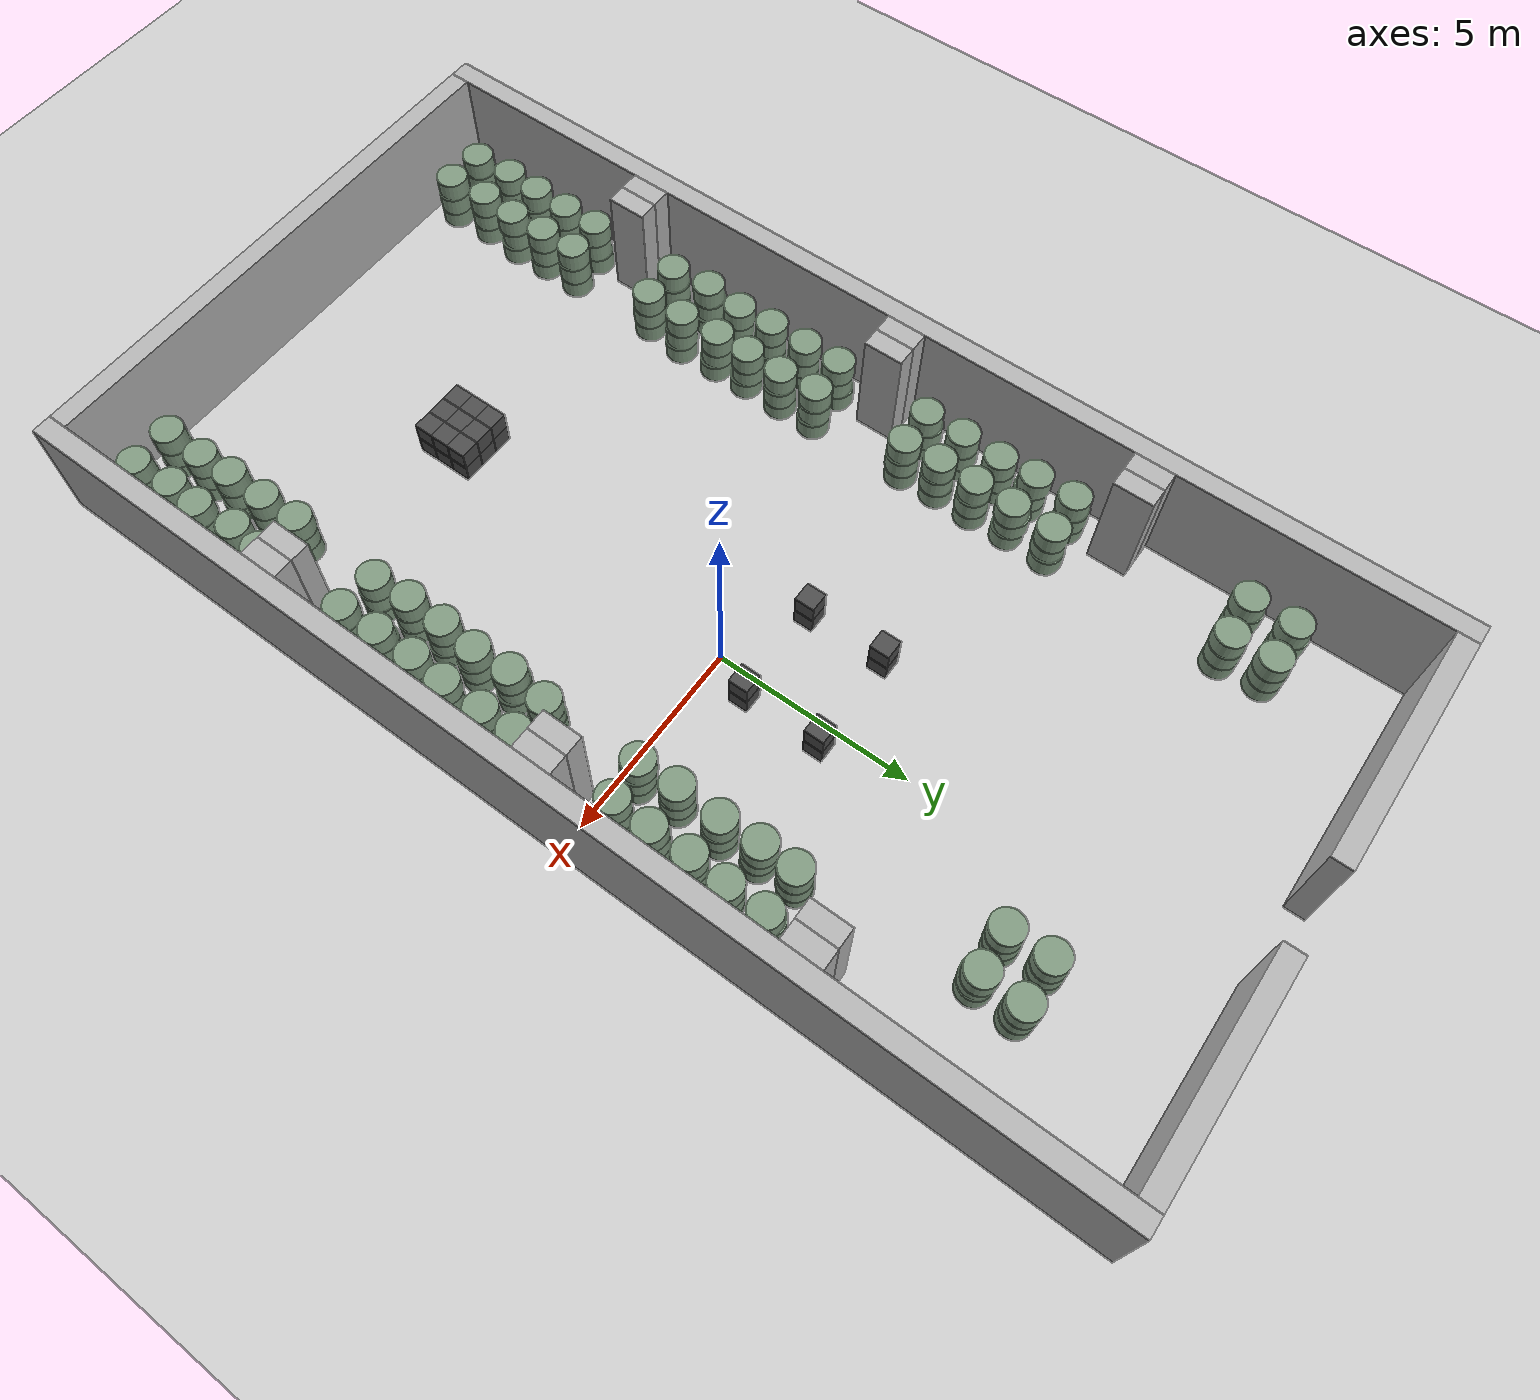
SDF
<sdf version="1.6">
 <world name="default">
  <light name="sun" type="directional">
   <cast_shadows>0</cast_shadows>
   <pose>0 0 10 0 -0 0</pose>
   <diffuse>0.8 0.8 0.8 1</diffuse>
   <specular>0.2 0.2 0.2 1</specular>
   <attenuation>
    <range>1000</range>
    <constant>0.9</constant>
    <linear>0.01</linear>
    <quadratic>0.001</quadratic>
   </attenuation>
   <direction>-0.5 0.1 -0.9</direction>
  </light>
  <include><uri>model://ground_plane</uri></include>
  <gravity>0 0 -9.8</gravity>
  <magnetic_field>6e-06 2.3e-05 -4.2e-05</magnetic_field>
  <atmosphere type="adiabatic"/>
  <physics name="default_physics" default="0" type="ode">
   <max_step_size>0.001</max_step_size>
   <real_time_factor>1</real_time_factor>
   <real_time_update_rate>1000</real_time_update_rate>
  </physics>
  <scene><ambient>0.4 0.4 0.4 1</ambient><background>0.7 0.7 0.7 1</background><shadows>0</shadows></scene>
  <spherical_coordinates>
   <surface_model>EARTH_WGS84</surface_model>
   <latitude_deg>0</latitude_deg>
   <longitude_deg>0</longitude_deg>
   <elevation>0</elevation>
   <heading_deg>0</heading_deg>
  </spherical_coordinates>
  <model name="wall_0">
   <pose>-8.5 -0.75 1.5 0 -0 0</pose>
   <static>True</static>
   <link name="link">
    <inertial>
     <mass>100</mass>
     <inertia>
      <ixx>0.166667</ixx>
      <ixy>0</ixy>
      <ixz>0</ixz>
      <iyy>0.166667</iyy>
      <iyz>0</iyz>
      <izz>0.166667</izz>
     </inertia>
    </inertial>
    <collision name="collision"><geometry><box><size>0.5 28.0 3.0</size></box></geometry></collision>
    <visual name="visual">
     <geometry><box><size>0.5 28.0 3.0</size></box></geometry>
     <material><ambient>0.7 0.7 0.7 1</ambient><diffuse>0.7 0.7 0.7 1</diffuse></material>
    </visual>
   </link>
  </model>
  <model name="wall_1">
   <pose>-8.0 -8.25 1.5 0 -0 0</pose>
   <static>True</static>
   <link name="link">
    <inertial>
     <mass>100</mass>
     <inertia>
      <ixx>0.166667</ixx>
      <ixy>0</ixy>
      <ixz>0</ixz>
      <iyy>0.166667</iyy>
      <iyz>0</iyz>
      <izz>0.166667</izz>
     </inertia>
    </inertial>
    <collision name="collision"><geometry><box><size>0.5 1.0 3.0</size></box></geometry></collision>
    <visual name="visual">
     <geometry><box><size>0.5 1.0 3.0</size></box></geometry>
     <material><ambient>0.7 0.7 0.7 1</ambient><diffuse>0.7 0.7 0.7 1</diffuse></material>
    </visual>
   </link>
  </model>
  <model name="wall_2">
   <pose>-8.0 -0.75 1.5 0 -0 0</pose>
   <static>True</static>
   <link name="link">
    <inertial>
     <mass>100</mass>
     <inertia>
      <ixx>0.166667</ixx>
      <ixy>0</ixy>
      <ixz>0</ixz>
      <iyy>0.166667</iyy>
      <iyz>0</iyz>
      <izz>0.166667</izz>
     </inertia>
    </inertial>
    <collision name="collision"><geometry><box><size>0.5 1.0 3.0</size></box></geometry></collision>
    <visual name="visual">
     <geometry><box><size>0.5 1.0 3.0</size></box></geometry>
     <material><ambient>0.7 0.7 0.7 1</ambient><diffuse>0.7 0.7 0.7 1</diffuse></material>
    </visual>
   </link>
  </model>
  <model name="wall_3">
   <pose>-8.0 5.75 1.5 0 -0 0</pose>
   <static>True</static>
   <link name="link">
    <inertial>
     <mass>100</mass>
     <inertia>
      <ixx>0.166667</ixx>
      <ixy>0</ixy>
      <ixz>0</ixz>
      <iyy>0.166667</iyy>
      <iyz>0</iyz>
      <izz>0.166667</izz>
     </inertia>
    </inertial>
    <collision name="collision"><geometry><box><size>0.5 1.0 3.0</size></box></geometry></collision>
    <visual name="visual">
     <geometry><box><size>0.5 1.0 3.0</size></box></geometry>
     <material><ambient>0.7 0.7 0.7 1</ambient><diffuse>0.7 0.7 0.7 1</diffuse></material>
    </visual>
   </link>
  </model>
  <model name="wall_4">
   <pose>-7.5 -8.25 1.5 0 -0 0</pose>
   <static>True</static>
   <link name="link">
    <inertial>
     <mass>100</mass>
     <inertia>
      <ixx>0.166667</ixx>
      <ixy>0</ixy>
      <ixz>0</ixz>
      <iyy>0.166667</iyy>
      <iyz>0</iyz>
      <izz>0.166667</izz>
     </inertia>
    </inertial>
    <collision name="collision"><geometry><box><size>0.5 1.0 3.0</size></box></geometry></collision>
    <visual name="visual">
     <geometry><box><size>0.5 1.0 3.0</size></box></geometry>
     <material><ambient>0.7 0.7 0.7 1</ambient><diffuse>0.7 0.7 0.7 1</diffuse></material>
    </visual>
   </link>
  </model>
  <model name="wall_5">
   <pose>-7.5 -0.75 1.5 0 -0 0</pose>
   <static>True</static>
   <link name="link">
    <inertial>
     <mass>100</mass>
     <inertia>
      <ixx>0.166667</ixx>
      <ixy>0</ixy>
      <ixz>0</ixz>
      <iyy>0.166667</iyy>
      <iyz>0</iyz>
      <izz>0.166667</izz>
     </inertia>
    </inertial>
    <collision name="collision"><geometry><box><size>0.5 1.0 3.0</size></box></geometry></collision>
    <visual name="visual">
     <geometry><box><size>0.5 1.0 3.0</size></box></geometry>
     <material><ambient>0.7 0.7 0.7 1</ambient><diffuse>0.7 0.7 0.7 1</diffuse></material>
    </visual>
   </link>
  </model>
  <model name="wall_6">
   <pose>-7.5 5.75 1.5 0 -0 0</pose>
   <static>True</static>
   <link name="link">
    <inertial>
     <mass>100</mass>
     <inertia>
      <ixx>0.166667</ixx>
      <ixy>0</ixy>
      <ixz>0</ixz>
      <iyy>0.166667</iyy>
      <iyz>0</iyz>
      <izz>0.166667</izz>
     </inertia>
    </inertial>
    <collision name="collision"><geometry><box><size>0.5 1.0 3.0</size></box></geometry></collision>
    <visual name="visual">
     <geometry><box><size>0.5 1.0 3.0</size></box></geometry>
     <material><ambient>0.7 0.7 0.7 1</ambient><diffuse>0.7 0.7 0.7 1</diffuse></material>
    </visual>
   </link>
  </model>
  <model name="wall_7">
   <pose>4.5 -8.25 1.5 0 -0 0</pose>
   <static>True</static>
   <link name="link">
    <inertial>
     <mass>100</mass>
     <inertia>
      <ixx>0.166667</ixx>
      <ixy>0</ixy>
      <ixz>0</ixz>
      <iyy>0.166667</iyy>
      <iyz>0</iyz>
      <izz>0.166667</izz>
     </inertia>
    </inertial>
    <collision name="collision"><geometry><box><size>0.5 1.0 3.0</size></box></geometry></collision>
    <visual name="visual">
     <geometry><box><size>0.5 1.0 3.0</size></box></geometry>
     <material><ambient>0.7 0.7 0.7 1</ambient><diffuse>0.7 0.7 0.7 1</diffuse></material>
    </visual>
   </link>
  </model>
  <model name="wall_8">
   <pose>4.5 -0.75 1.5 0 -0 0</pose>
   <static>True</static>
   <link name="link">
    <inertial>
     <mass>100</mass>
     <inertia>
      <ixx>0.166667</ixx>
      <ixy>0</ixy>
      <ixz>0</ixz>
      <iyy>0.166667</iyy>
      <iyz>0</iyz>
      <izz>0.166667</izz>
     </inertia>
    </inertial>
    <collision name="collision"><geometry><box><size>0.5 1.0 3.0</size></box></geometry></collision>
    <visual name="visual">
     <geometry><box><size>0.5 1.0 3.0</size></box></geometry>
     <material><ambient>0.7 0.7 0.7 1</ambient><diffuse>0.7 0.7 0.7 1</diffuse></material>
    </visual>
   </link>
  </model>
  <model name="wall_9">
   <pose>4.5 5.75 1.5 0 -0 0</pose>
   <static>True</static>
   <link name="link">
    <inertial>
     <mass>100</mass>
     <inertia>
      <ixx>0.166667</ixx>
      <ixy>0</ixy>
      <ixz>0</ixz>
      <iyy>0.166667</iyy>
      <iyz>0</iyz>
      <izz>0.166667</izz>
     </inertia>
    </inertial>
    <collision name="collision"><geometry><box><size>0.5 1.0 3.0</size></box></geometry></collision>
    <visual name="visual">
     <geometry><box><size>0.5 1.0 3.0</size></box></geometry>
     <material><ambient>0.7 0.7 0.7 1</ambient><diffuse>0.7 0.7 0.7 1</diffuse></material>
    </visual>
   </link>
  </model>
  <model name="wall_10">
   <pose>5.0 -8.25 1.5 0 -0 0</pose>
   <static>True</static>
   <link name="link">
    <inertial>
     <mass>100</mass>
     <inertia>
      <ixx>0.166667</ixx>
      <ixy>0</ixy>
      <ixz>0</ixz>
      <iyy>0.166667</iyy>
      <iyz>0</iyz>
      <izz>0.166667</izz>
     </inertia>
    </inertial>
    <collision name="collision"><geometry><box><size>0.5 1.0 3.0</size></box></geometry></collision>
    <visual name="visual">
     <geometry><box><size>0.5 1.0 3.0</size></box></geometry>
     <material><ambient>0.7 0.7 0.7 1</ambient><diffuse>0.7 0.7 0.7 1</diffuse></material>
    </visual>
   </link>
  </model>
  <model name="wall_11">
   <pose>5.0 -0.75 1.5 0 -0 0</pose>
   <static>True</static>
   <link name="link">
    <inertial>
     <mass>100</mass>
     <inertia>
      <ixx>0.166667</ixx>
      <ixy>0</ixy>
      <ixz>0</ixz>
      <iyy>0.166667</iyy>
      <iyz>0</iyz>
      <izz>0.166667</izz>
     </inertia>
    </inertial>
    <collision name="collision"><geometry><box><size>0.5 1.0 3.0</size></box></geometry></collision>
    <visual name="visual">
     <geometry><box><size>0.5 1.0 3.0</size></box></geometry>
     <material><ambient>0.7 0.7 0.7 1</ambient><diffuse>0.7 0.7 0.7 1</diffuse></material>
    </visual>
   </link>
  </model>
  <model name="wall_12">
   <pose>5.0 5.75 1.5 0 -0 0</pose>
   <static>True</static>
   <link name="link">
    <inertial>
     <mass>100</mass>
     <inertia>
      <ixx>0.166667</ixx>
      <ixy>0</ixy>
      <ixz>0</ixz>
      <iyy>0.166667</iyy>
      <iyz>0</iyz>
      <izz>0.166667</izz>
     </inertia>
    </inertial>
    <collision name="collision"><geometry><box><size>0.5 1.0 3.0</size></box></geometry></collision>
    <visual name="visual">
     <geometry><box><size>0.5 1.0 3.0</size></box></geometry>
     <material><ambient>0.7 0.7 0.7 1</ambient><diffuse>0.7 0.7 0.7 1</diffuse></material>
    </visual>
   </link>
  </model>
  <model name="wall_13">
   <pose>5.5 -0.75 1.5 0 -0 0</pose>
   <static>True</static>
   <link name="link">
    <inertial>
     <mass>100</mass>
     <inertia>
      <ixx>0.166667</ixx>
      <ixy>0</ixy>
      <ixz>0</ixz>
      <iyy>0.166667</iyy>
      <iyz>0</iyz>
      <izz>0.166667</izz>
     </inertia>
    </inertial>
    <collision name="collision"><geometry><box><size>0.5 28.0 3.0</size></box></geometry></collision>
    <visual name="visual">
     <geometry><box><size>0.5 28.0 3.0</size></box></geometry>
     <material><ambient>0.7 0.7 0.7 1</ambient><diffuse>0.7 0.7 0.7 1</diffuse></material>
    </visual>
   </link>
  </model>
  <model name="wall_14">
   <pose>-1.5 -14.5 1.5 0 -0 0</pose>
   <static>True</static>
   <link name="link">
    <inertial>
     <mass>100</mass>
     <inertia>
      <ixx>0.166667</ixx>
      <ixy>0</ixy>
      <ixz>0</ixz>
      <iyy>0.166667</iyy>
      <iyz>0</iyz>
      <izz>0.166667</izz>
     </inertia>
    </inertial>
    <collision name="collision"><geometry><box><size>13.5 0.5 3.0</size></box></geometry></collision>
    <visual name="visual">
     <geometry><box><size>13.5 0.5 3.0</size></box></geometry>
     <material><ambient>0.7 0.7 0.7 1</ambient><diffuse>0.7 0.7 0.7 1</diffuse></material>
    </visual>
   </link>
  </model>
  <model name="wall_15">
   <pose>-5.25 13.0 1.5 0 -0 0</pose>
   <static>True</static>
   <link name="link">
    <inertial>
     <mass>100</mass>
     <inertia>
      <ixx>0.166667</ixx>
      <ixy>0</ixy>
      <ixz>0</ixz>
      <iyy>0.166667</iyy>
      <iyz>0</iyz>
      <izz>0.166667</izz>
     </inertia>
    </inertial>
    <collision name="collision"><geometry><box><size>6.0 0.5 3.0</size></box></geometry></collision>
    <visual name="visual">
     <geometry><box><size>6.0 0.5 3.0</size></box></geometry>
     <material><ambient>0.7 0.7 0.7 1</ambient><diffuse>0.7 0.7 0.7 1</diffuse></material>
    </visual>
   </link>
  </model>
  <model name="wall_16">
   <pose>2.5 13.0 1.5 0 -0 0</pose>
   <static>True</static>
   <link name="link">
    <inertial>
     <mass>100</mass>
     <inertia>
      <ixx>0.166667</ixx>
      <ixy>0</ixy>
      <ixz>0</ixz>
      <iyy>0.166667</iyy>
      <iyz>0</iyz>
      <izz>0.166667</izz>
     </inertia>
    </inertial>
    <collision name="collision"><geometry><box><size>5.5 0.5 3.0</size></box></geometry></collision>
    <visual name="visual">
     <geometry><box><size>5.5 0.5 3.0</size></box></geometry>
     <material><ambient>0.7 0.7 0.7 1</ambient><diffuse>0.7 0.7 0.7 1</diffuse></material>
    </visual>
   </link>
  </model>
  <model name="unit_box_0">
   <pose>-2.0 1.0 0.25 0 -0 0</pose>
   <static>True</static>
   <link name="link">
    <inertial>
     <mass>100</mass>
     <inertia>
      <ixx>0.166667</ixx>
      <ixy>0</ixy>
      <ixz>0</ixz>
      <iyy>0.166667</iyy>
      <iyz>0</iyz>
      <izz>0.166667</izz>
     </inertia>
    </inertial>
    <collision name="collision"><geometry><box><size>0.5 0.5 0.5</size></box></geometry></collision>
    <visual name="visual">
     <geometry><box><size>0.5 0.5 0.5</size></box></geometry>
     <material><ambient>0.3 0.3 0.3 1</ambient><diffuse>0.3 0.3 0.3 1</diffuse></material>
    </visual>
   </link>
  </model>
  <model name="unit_box_1">
   <pose>-2.0 1.0 0.75 0 -0 0</pose>
   <static>True</static>
   <link name="link">
    <inertial>
     <mass>100</mass>
     <inertia>
      <ixx>0.166667</ixx>
      <ixy>0</ixy>
      <ixz>0</ixz>
      <iyy>0.166667</iyy>
      <iyz>0</iyz>
      <izz>0.166667</izz>
     </inertia>
    </inertial>
    <collision name="collision"><geometry><box><size>0.5 0.5 0.5</size></box></geometry></collision>
    <visual name="visual">
     <geometry><box><size>0.5 0.5 0.5</size></box></geometry>
     <material><ambient>0.3 0.3 0.3 1</ambient><diffuse>0.3 0.3 0.3 1</diffuse></material>
    </visual>
   </link>
  </model>
  <model name="unit_box_2">
   <pose>-2.0 3.0 0.25 0 -0 0</pose>
   <static>True</static>
   <link name="link">
    <inertial>
     <mass>100</mass>
     <inertia>
      <ixx>0.166667</ixx>
      <ixy>0</ixy>
      <ixz>0</ixz>
      <iyy>0.166667</iyy>
      <iyz>0</iyz>
      <izz>0.166667</izz>
     </inertia>
    </inertial>
    <collision name="collision"><geometry><box><size>0.5 0.5 0.5</size></box></geometry></collision>
    <visual name="visual">
     <geometry><box><size>0.5 0.5 0.5</size></box></geometry>
     <material><ambient>0.3 0.3 0.3 1</ambient><diffuse>0.3 0.3 0.3 1</diffuse></material>
    </visual>
   </link>
  </model>
  <model name="unit_box_3">
   <pose>-2.0 3.0 0.75 0 -0 0</pose>
   <static>True</static>
   <link name="link">
    <inertial>
     <mass>100</mass>
     <inertia>
      <ixx>0.166667</ixx>
      <ixy>0</ixy>
      <ixz>0</ixz>
      <iyy>0.166667</iyy>
      <iyz>0</iyz>
      <izz>0.166667</izz>
     </inertia>
    </inertial>
    <collision name="collision"><geometry><box><size>0.5 0.5 0.5</size></box></geometry></collision>
    <visual name="visual">
     <geometry><box><size>0.5 0.5 0.5</size></box></geometry>
     <material><ambient>0.3 0.3 0.3 1</ambient><diffuse>0.3 0.3 0.3 1</diffuse></material>
    </visual>
   </link>
  </model>
  <model name="unit_box_4">
   <pose>-1.5 -9.0 0.25 0 -0 0</pose>
   <static>True</static>
   <link name="link">
    <inertial>
     <mass>100</mass>
     <inertia>
      <ixx>0.166667</ixx>
      <ixy>0</ixy>
      <ixz>0</ixz>
      <iyy>0.166667</iyy>
      <iyz>0</iyz>
      <izz>0.166667</izz>
     </inertia>
    </inertial>
    <collision name="collision"><geometry><box><size>0.5 0.5 0.5</size></box></geometry></collision>
    <visual name="visual">
     <geometry><box><size>0.5 0.5 0.5</size></box></geometry>
     <material><ambient>0.3 0.3 0.3 1</ambient><diffuse>0.3 0.3 0.3 1</diffuse></material>
    </visual>
   </link>
  </model>
  <model name="unit_box_5">
   <pose>-1.5 -9.0 0.75 0 -0 0</pose>
   <static>True</static>
   <link name="link">
    <inertial>
     <mass>100</mass>
     <inertia>
      <ixx>0.166667</ixx>
      <ixy>0</ixy>
      <ixz>0</ixz>
      <iyy>0.166667</iyy>
      <iyz>0</iyz>
      <izz>0.166667</izz>
     </inertia>
    </inertial>
    <collision name="collision"><geometry><box><size>0.5 0.5 0.5</size></box></geometry></collision>
    <visual name="visual">
     <geometry><box><size>0.5 0.5 0.5</size></box></geometry>
     <material><ambient>0.3 0.3 0.3 1</ambient><diffuse>0.3 0.3 0.3 1</diffuse></material>
    </visual>
   </link>
  </model>
  <model name="unit_box_6">
   <pose>-1.5 -8.5 0.25 0 -0 0</pose>
   <static>True</static>
   <link name="link">
    <inertial>
     <mass>100</mass>
     <inertia>
      <ixx>0.166667</ixx>
      <ixy>0</ixy>
      <ixz>0</ixz>
      <iyy>0.166667</iyy>
      <iyz>0</iyz>
      <izz>0.166667</izz>
     </inertia>
    </inertial>
    <collision name="collision"><geometry><box><size>0.5 0.5 0.5</size></box></geometry></collision>
    <visual name="visual">
     <geometry><box><size>0.5 0.5 0.5</size></box></geometry>
     <material><ambient>0.3 0.3 0.3 1</ambient><diffuse>0.3 0.3 0.3 1</diffuse></material>
    </visual>
   </link>
  </model>
  <model name="unit_box_7">
   <pose>-1.5 -8.5 0.75 0 -0 0</pose>
   <static>True</static>
   <link name="link">
    <inertial>
     <mass>100</mass>
     <inertia>
      <ixx>0.166667</ixx>
      <ixy>0</ixy>
      <ixz>0</ixz>
      <iyy>0.166667</iyy>
      <iyz>0</iyz>
      <izz>0.166667</izz>
     </inertia>
    </inertial>
    <collision name="collision"><geometry><box><size>0.5 0.5 0.5</size></box></geometry></collision>
    <visual name="visual">
     <geometry><box><size>0.5 0.5 0.5</size></box></geometry>
     <material><ambient>0.3 0.3 0.3 1</ambient><diffuse>0.3 0.3 0.3 1</diffuse></material>
    </visual>
   </link>
  </model>
  <model name="unit_box_8">
   <pose>-1.5 -8.0 0.25 0 -0 0</pose>
   <static>True</static>
   <link name="link">
    <inertial>
     <mass>100</mass>
     <inertia>
      <ixx>0.166667</ixx>
      <ixy>0</ixy>
      <ixz>0</ixz>
      <iyy>0.166667</iyy>
      <iyz>0</iyz>
      <izz>0.166667</izz>
     </inertia>
    </inertial>
    <collision name="collision"><geometry><box><size>0.5 0.5 0.5</size></box></geometry></collision>
    <visual name="visual">
     <geometry><box><size>0.5 0.5 0.5</size></box></geometry>
     <material><ambient>0.3 0.3 0.3 1</ambient><diffuse>0.3 0.3 0.3 1</diffuse></material>
    </visual>
   </link>
  </model>
  <model name="unit_box_9">
   <pose>-1.5 -8.0 0.75 0 -0 0</pose>
   <static>True</static>
   <link name="link">
    <inertial>
     <mass>100</mass>
     <inertia>
      <ixx>0.166667</ixx>
      <ixy>0</ixy>
      <ixz>0</ixz>
      <iyy>0.166667</iyy>
      <iyz>0</iyz>
      <izz>0.166667</izz>
     </inertia>
    </inertial>
    <collision name="collision"><geometry><box><size>0.5 0.5 0.5</size></box></geometry></collision>
    <visual name="visual">
     <geometry><box><size>0.5 0.5 0.5</size></box></geometry>
     <material><ambient>0.3 0.3 0.3 1</ambient><diffuse>0.3 0.3 0.3 1</diffuse></material>
    </visual>
   </link>
  </model>
  <model name="unit_box_10">
   <pose>-1.0 -9.0 0.25 0 -0 0</pose>
   <static>True</static>
   <link name="link">
    <inertial>
     <mass>100</mass>
     <inertia>
      <ixx>0.166667</ixx>
      <ixy>0</ixy>
      <ixz>0</ixz>
      <iyy>0.166667</iyy>
      <iyz>0</iyz>
      <izz>0.166667</izz>
     </inertia>
    </inertial>
    <collision name="collision"><geometry><box><size>0.5 0.5 0.5</size></box></geometry></collision>
    <visual name="visual">
     <geometry><box><size>0.5 0.5 0.5</size></box></geometry>
     <material><ambient>0.3 0.3 0.3 1</ambient><diffuse>0.3 0.3 0.3 1</diffuse></material>
    </visual>
   </link>
  </model>
  <model name="unit_box_11">
   <pose>-1.0 -9.0 0.75 0 -0 0</pose>
   <static>True</static>
   <link name="link">
    <inertial>
     <mass>100</mass>
     <inertia>
      <ixx>0.166667</ixx>
      <ixy>0</ixy>
      <ixz>0</ixz>
      <iyy>0.166667</iyy>
      <iyz>0</iyz>
      <izz>0.166667</izz>
     </inertia>
    </inertial>
    <collision name="collision"><geometry><box><size>0.5 0.5 0.5</size></box></geometry></collision>
    <visual name="visual">
     <geometry><box><size>0.5 0.5 0.5</size></box></geometry>
     <material><ambient>0.3 0.3 0.3 1</ambient><diffuse>0.3 0.3 0.3 1</diffuse></material>
    </visual>
   </link>
  </model>
  <model name="unit_box_12">
   <pose>-1.0 -8.5 0.25 0 -0 0</pose>
   <static>True</static>
   <link name="link">
    <inertial>
     <mass>100</mass>
     <inertia>
      <ixx>0.166667</ixx>
      <ixy>0</ixy>
      <ixz>0</ixz>
      <iyy>0.166667</iyy>
      <iyz>0</iyz>
      <izz>0.166667</izz>
     </inertia>
    </inertial>
    <collision name="collision"><geometry><box><size>0.5 0.5 0.5</size></box></geometry></collision>
    <visual name="visual">
     <geometry><box><size>0.5 0.5 0.5</size></box></geometry>
     <material><ambient>0.3 0.3 0.3 1</ambient><diffuse>0.3 0.3 0.3 1</diffuse></material>
    </visual>
   </link>
  </model>
  <model name="unit_box_13">
   <pose>-1.0 -8.5 0.75 0 -0 0</pose>
   <static>True</static>
   <link name="link">
    <inertial>
     <mass>100</mass>
     <inertia>
      <ixx>0.166667</ixx>
      <ixy>0</ixy>
      <ixz>0</ixz>
      <iyy>0.166667</iyy>
      <iyz>0</iyz>
      <izz>0.166667</izz>
     </inertia>
    </inertial>
    <collision name="collision"><geometry><box><size>0.5 0.5 0.5</size></box></geometry></collision>
    <visual name="visual">
     <geometry><box><size>0.5 0.5 0.5</size></box></geometry>
     <material><ambient>0.3 0.3 0.3 1</ambient><diffuse>0.3 0.3 0.3 1</diffuse></material>
    </visual>
   </link>
  </model>
  <model name="unit_box_14">
   <pose>-1.0 -8.0 0.25 0 -0 0</pose>
   <static>True</static>
   <link name="link">
    <inertial>
     <mass>100</mass>
     <inertia>
      <ixx>0.166667</ixx>
      <ixy>0</ixy>
      <ixz>0</ixz>
      <iyy>0.166667</iyy>
      <iyz>0</iyz>
      <izz>0.166667</izz>
     </inertia>
    </inertial>
    <collision name="collision"><geometry><box><size>0.5 0.5 0.5</size></box></geometry></collision>
    <visual name="visual">
     <geometry><box><size>0.5 0.5 0.5</size></box></geometry>
     <material><ambient>0.3 0.3 0.3 1</ambient><diffuse>0.3 0.3 0.3 1</diffuse></material>
    </visual>
   </link>
  </model>
  <model name="unit_box_15">
   <pose>-1.0 -8.0 0.75 0 -0 0</pose>
   <static>True</static>
   <link name="link">
    <inertial>
     <mass>100</mass>
     <inertia>
      <ixx>0.166667</ixx>
      <ixy>0</ixy>
      <ixz>0</ixz>
      <iyy>0.166667</iyy>
      <iyz>0</iyz>
      <izz>0.166667</izz>
     </inertia>
    </inertial>
    <collision name="collision"><geometry><box><size>0.5 0.5 0.5</size></box></geometry></collision>
    <visual name="visual">
     <geometry><box><size>0.5 0.5 0.5</size></box></geometry>
     <material><ambient>0.3 0.3 0.3 1</ambient><diffuse>0.3 0.3 0.3 1</diffuse></material>
    </visual>
   </link>
  </model>
  <model name="unit_box_16">
   <pose>-0.5 -9.0 0.25 0 -0 0</pose>
   <static>True</static>
   <link name="link">
    <inertial>
     <mass>100</mass>
     <inertia>
      <ixx>0.166667</ixx>
      <ixy>0</ixy>
      <ixz>0</ixz>
      <iyy>0.166667</iyy>
      <iyz>0</iyz>
      <izz>0.166667</izz>
     </inertia>
    </inertial>
    <collision name="collision"><geometry><box><size>0.5 0.5 0.5</size></box></geometry></collision>
    <visual name="visual">
     <geometry><box><size>0.5 0.5 0.5</size></box></geometry>
     <material><ambient>0.3 0.3 0.3 1</ambient><diffuse>0.3 0.3 0.3 1</diffuse></material>
    </visual>
   </link>
  </model>
  <model name="unit_box_17">
   <pose>-0.5 -9.0 0.75 0 -0 0</pose>
   <static>True</static>
   <link name="link">
    <inertial>
     <mass>100</mass>
     <inertia>
      <ixx>0.166667</ixx>
      <ixy>0</ixy>
      <ixz>0</ixz>
      <iyy>0.166667</iyy>
      <iyz>0</iyz>
      <izz>0.166667</izz>
     </inertia>
    </inertial>
    <collision name="collision"><geometry><box><size>0.5 0.5 0.5</size></box></geometry></collision>
    <visual name="visual">
     <geometry><box><size>0.5 0.5 0.5</size></box></geometry>
     <material><ambient>0.3 0.3 0.3 1</ambient><diffuse>0.3 0.3 0.3 1</diffuse></material>
    </visual>
   </link>
  </model>
  <model name="unit_box_18">
   <pose>-0.5 -8.5 0.25 0 -0 0</pose>
   <static>True</static>
   <link name="link">
    <inertial>
     <mass>100</mass>
     <inertia>
      <ixx>0.166667</ixx>
      <ixy>0</ixy>
      <ixz>0</ixz>
      <iyy>0.166667</iyy>
      <iyz>0</iyz>
      <izz>0.166667</izz>
     </inertia>
    </inertial>
    <collision name="collision"><geometry><box><size>0.5 0.5 0.5</size></box></geometry></collision>
    <visual name="visual">
     <geometry><box><size>0.5 0.5 0.5</size></box></geometry>
     <material><ambient>0.3 0.3 0.3 1</ambient><diffuse>0.3 0.3 0.3 1</diffuse></material>
    </visual>
   </link>
  </model>
  <model name="unit_box_19">
   <pose>-0.5 -8.5 0.75 0 -0 0</pose>
   <static>True</static>
   <link name="link">
    <inertial>
     <mass>100</mass>
     <inertia>
      <ixx>0.166667</ixx>
      <ixy>0</ixy>
      <ixz>0</ixz>
      <iyy>0.166667</iyy>
      <iyz>0</iyz>
      <izz>0.166667</izz>
     </inertia>
    </inertial>
    <collision name="collision"><geometry><box><size>0.5 0.5 0.5</size></box></geometry></collision>
    <visual name="visual">
     <geometry><box><size>0.5 0.5 0.5</size></box></geometry>
     <material><ambient>0.3 0.3 0.3 1</ambient><diffuse>0.3 0.3 0.3 1</diffuse></material>
    </visual>
   </link>
  </model>
  <model name="unit_box_20">
   <pose>-0.5 -8.0 0.25 0 -0 0</pose>
   <static>True</static>
   <link name="link">
    <inertial>
     <mass>100</mass>
     <inertia>
      <ixx>0.166667</ixx>
      <ixy>0</ixy>
      <ixz>0</ixz>
      <iyy>0.166667</iyy>
      <iyz>0</iyz>
      <izz>0.166667</izz>
     </inertia>
    </inertial>
    <collision name="collision"><geometry><box><size>0.5 0.5 0.5</size></box></geometry></collision>
    <visual name="visual">
     <geometry><box><size>0.5 0.5 0.5</size></box></geometry>
     <material><ambient>0.3 0.3 0.3 1</ambient><diffuse>0.3 0.3 0.3 1</diffuse></material>
    </visual>
   </link>
  </model>
  <model name="unit_box_21">
   <pose>-0.5 -8.0 0.75 0 -0 0</pose>
   <static>True</static>
   <link name="link">
    <inertial>
     <mass>100</mass>
     <inertia>
      <ixx>0.166667</ixx>
      <ixy>0</ixy>
      <ixz>0</ixz>
      <iyy>0.166667</iyy>
      <iyz>0</iyz>
      <izz>0.166667</izz>
     </inertia>
    </inertial>
    <collision name="collision"><geometry><box><size>0.5 0.5 0.5</size></box></geometry></collision>
    <visual name="visual">
     <geometry><box><size>0.5 0.5 0.5</size></box></geometry>
     <material><ambient>0.3 0.3 0.3 1</ambient><diffuse>0.3 0.3 0.3 1</diffuse></material>
    </visual>
   </link>
  </model>
  <model name="unit_box_22">
   <pose>0.5 1.0 0.25 0 -0 0</pose>
   <static>True</static>
   <link name="link">
    <inertial>
     <mass>100</mass>
     <inertia>
      <ixx>0.166667</ixx>
      <ixy>0</ixy>
      <ixz>0</ixz>
      <iyy>0.166667</iyy>
      <iyz>0</iyz>
      <izz>0.166667</izz>
     </inertia>
    </inertial>
    <collision name="collision"><geometry><box><size>0.5 0.5 0.5</size></box></geometry></collision>
    <visual name="visual">
     <geometry><box><size>0.5 0.5 0.5</size></box></geometry>
     <material><ambient>0.3 0.3 0.3 1</ambient><diffuse>0.3 0.3 0.3 1</diffuse></material>
    </visual>
   </link>
  </model>
  <model name="unit_box_23">
   <pose>0.5 1.0 0.75 0 -0 0</pose>
   <static>True</static>
   <link name="link">
    <inertial>
     <mass>100</mass>
     <inertia>
      <ixx>0.166667</ixx>
      <ixy>0</ixy>
      <ixz>0</ixz>
      <iyy>0.166667</iyy>
      <iyz>0</iyz>
      <izz>0.166667</izz>
     </inertia>
    </inertial>
    <collision name="collision"><geometry><box><size>0.5 0.5 0.5</size></box></geometry></collision>
    <visual name="visual">
     <geometry><box><size>0.5 0.5 0.5</size></box></geometry>
     <material><ambient>0.3 0.3 0.3 1</ambient><diffuse>0.3 0.3 0.3 1</diffuse></material>
    </visual>
   </link>
  </model>
  <model name="unit_box_24">
   <pose>0.5 3.0 0.25 0 -0 0</pose>
   <static>True</static>
   <link name="link">
    <inertial>
     <mass>100</mass>
     <inertia>
      <ixx>0.166667</ixx>
      <ixy>0</ixy>
      <ixz>0</ixz>
      <iyy>0.166667</iyy>
      <iyz>0</iyz>
      <izz>0.166667</izz>
     </inertia>
    </inertial>
    <collision name="collision"><geometry><box><size>0.5 0.5 0.5</size></box></geometry></collision>
    <visual name="visual">
     <geometry><box><size>0.5 0.5 0.5</size></box></geometry>
     <material><ambient>0.3 0.3 0.3 1</ambient><diffuse>0.3 0.3 0.3 1</diffuse></material>
    </visual>
   </link>
  </model>
  <model name="unit_box_25">
   <pose>0.5 3.0 0.75 0 -0 0</pose>
   <static>True</static>
   <link name="link">
    <inertial>
     <mass>100</mass>
     <inertia>
      <ixx>0.166667</ixx>
      <ixy>0</ixy>
      <ixz>0</ixz>
      <iyy>0.166667</iyy>
      <iyz>0</iyz>
      <izz>0.166667</izz>
     </inertia>
    </inertial>
    <collision name="collision"><geometry><box><size>0.5 0.5 0.5</size></box></geometry></collision>
    <visual name="visual">
     <geometry><box><size>0.5 0.5 0.5</size></box></geometry>
     <material><ambient>0.3 0.3 0.3 1</ambient><diffuse>0.3 0.3 0.3 1</diffuse></material>
    </visual>
   </link>
  </model>
  <model name="unit_cylinder_0">
   <pose>-7.47507695646 -13.5184655306 0.25 0 -0 0</pose>
   <static>True</static>
   <link name="link">
    <inertial>
     <mass>100</mass>
     <inertia><ixx>0.145833</ixx><ixy>0</ixy><ixz>0</ixz><iyy>0.145833</iyy><iyz>0</iyz><izz>0.125</izz></inertia>
    </inertial>
    <collision name="collision">
     <geometry><cylinder><radius>0.4</radius><length>0.5</length></cylinder></geometry>
     <max_contacts>100</max_contacts>
    </collision>
    <visual name="visual">
     <geometry><cylinder><radius>0.4</radius><length>0.5</length></cylinder></geometry>
     <material><ambient>0.5 0.6 0.5 1</ambient><diffuse>0.5 0.6 0.5 1</diffuse></material>
    </visual>
   </link>
  </model>
  <model name="unit_cylinder_1">
   <pose>-7.48919808959 -13.4883875363 0.75 0 -0 0</pose>
   <static>True</static>
   <link name="link">
    <inertial>
     <mass>100</mass>
     <inertia><ixx>0.145833</ixx><ixy>0</ixy><ixz>0</ixz><iyy>0.145833</iyy><iyz>0</iyz><izz>0.125</izz></inertia>
    </inertial>
    <collision name="collision">
     <geometry><cylinder><radius>0.4</radius><length>0.5</length></cylinder></geometry>
     <max_contacts>100</max_contacts>
    </collision>
    <visual name="visual">
     <geometry><cylinder><radius>0.4</radius><length>0.5</length></cylinder></geometry>
     <material><ambient>0.5 0.6 0.5 1</ambient><diffuse>0.5 0.6 0.5 1</diffuse></material>
    </visual>
   </link>
  </model>
  <model name="unit_cylinder_2">
   <pose>-7.48988754666 -13.5205118433 1.25 0 -0 0</pose>
   <static>True</static>
   <link name="link">
    <inertial>
     <mass>100</mass>
     <inertia><ixx>0.145833</ixx><ixy>0</ixy><ixz>0</ixz><iyy>0.145833</iyy><iyz>0</iyz><izz>0.125</izz></inertia>
    </inertial>
    <collision name="collision">
     <geometry><cylinder><radius>0.4</radius><length>0.5</length></cylinder></geometry>
     <max_contacts>100</max_contacts>
    </collision>
    <visual name="visual">
     <geometry><cylinder><radius>0.4</radius><length>0.5</length></cylinder></geometry>
     <material><ambient>0.5 0.6 0.5 1</ambient><diffuse>0.5 0.6 0.5 1</diffuse></material>
    </visual>
   </link>
  </model>
  <model name="unit_cylinder_3">
   <pose>-7.53306076907 -12.4352780007 0.25 0 -0 0</pose>
   <static>True</static>
   <link name="link">
    <inertial>
     <mass>100</mass>
     <inertia><ixx>0.145833</ixx><ixy>0</ixy><ixz>0</ixz><iyy>0.145833</iyy><iyz>0</iyz><izz>0.125</izz></inertia>
    </inertial>
    <collision name="collision">
     <geometry><cylinder><radius>0.4</radius><length>0.5</length></cylinder></geometry>
     <max_contacts>100</max_contacts>
    </collision>
    <visual name="visual">
     <geometry><cylinder><radius>0.4</radius><length>0.5</length></cylinder></geometry>
     <material><ambient>0.5 0.6 0.5 1</ambient><diffuse>0.5 0.6 0.5 1</diffuse></material>
    </visual>
   </link>
  </model>
  <model name="unit_cylinder_4">
   <pose>-7.56399221615 -12.4517953891 0.75 0 -0 0</pose>
   <static>True</static>
   <link name="link">
    <inertial>
     <mass>100</mass>
     <inertia><ixx>0.145833</ixx><ixy>0</ixy><ixz>0</ixz><iyy>0.145833</iyy><iyz>0</iyz><izz>0.125</izz></inertia>
    </inertial>
    <collision name="collision">
     <geometry><cylinder><radius>0.4</radius><length>0.5</length></cylinder></geometry>
     <max_contacts>100</max_contacts>
    </collision>
    <visual name="visual">
     <geometry><cylinder><radius>0.4</radius><length>0.5</length></cylinder></geometry>
     <material><ambient>0.5 0.6 0.5 1</ambient><diffuse>0.5 0.6 0.5 1</diffuse></material>
    </visual>
   </link>
  </model>
  <model name="unit_cylinder_5">
   <pose>-7.53500089518 -12.4614403091 1.25 0 -0 0</pose>
   <static>True</static>
   <link name="link">
    <inertial>
     <mass>100</mass>
     <inertia><ixx>0.145833</ixx><ixy>0</ixy><ixz>0</ixz><iyy>0.145833</iyy><iyz>0</iyz><izz>0.125</izz></inertia>
    </inertial>
    <collision name="collision">
     <geometry><cylinder><radius>0.4</radius><length>0.5</length></cylinder></geometry>
     <max_contacts>100</max_contacts>
    </collision>
    <visual name="visual">
     <geometry><cylinder><radius>0.4</radius><length>0.5</length></cylinder></geometry>
     <material><ambient>0.5 0.6 0.5 1</ambient><diffuse>0.5 0.6 0.5 1</diffuse></material>
    </visual>
   </link>
  </model>
  <model name="unit_cylinder_6">
   <pose>-7.46616859764 -11.5065697093 0.25 0 -0 0</pose>
   <static>True</static>
   <link name="link">
    <inertial>
     <mass>100</mass>
     <inertia><ixx>0.145833</ixx><ixy>0</ixy><ixz>0</ixz><iyy>0.145833</iyy><iyz>0</iyz><izz>0.125</izz></inertia>
    </inertial>
    <collision name="collision">
     <geometry><cylinder><radius>0.4</radius><length>0.5</length></cylinder></geometry>
     <max_contacts>100</max_contacts>
    </collision>
    <visual name="visual">
     <geometry><cylinder><radius>0.4</radius><length>0.5</length></cylinder></geometry>
     <material><ambient>0.5 0.6 0.5 1</ambient><diffuse>0.5 0.6 0.5 1</diffuse></material>
    </visual>
   </link>
  </model>
  <model name="unit_cylinder_7">
   <pose>-7.4452347965 -11.5127901464 0.75 0 -0 0</pose>
   <static>True</static>
   <link name="link">
    <inertial>
     <mass>100</mass>
     <inertia><ixx>0.145833</ixx><ixy>0</ixy><ixz>0</ixz><iyy>0.145833</iyy><iyz>0</iyz><izz>0.125</izz></inertia>
    </inertial>
    <collision name="collision">
     <geometry><cylinder><radius>0.4</radius><length>0.5</length></cylinder></geometry>
     <max_contacts>100</max_contacts>
    </collision>
    <visual name="visual">
     <geometry><cylinder><radius>0.4</radius><length>0.5</length></cylinder></geometry>
     <material><ambient>0.5 0.6 0.5 1</ambient><diffuse>0.5 0.6 0.5 1</diffuse></material>
    </visual>
   </link>
  </model>
  <model name="unit_cylinder_8">
   <pose>-7.49248867613 -11.5228580544 1.25 0 -0 0</pose>
   <static>True</static>
   <link name="link">
    <inertial>
     <mass>100</mass>
     <inertia><ixx>0.145833</ixx><ixy>0</ixy><ixz>0</ixz><iyy>0.145833</iyy><iyz>0</iyz><izz>0.125</izz></inertia>
    </inertial>
    <collision name="collision">
     <geometry><cylinder><radius>0.4</radius><length>0.5</length></cylinder></geometry>
     <max_contacts>100</max_contacts>
    </collision>
    <visual name="visual">
     <geometry><cylinder><radius>0.4</radius><length>0.5</length></cylinder></geometry>
     <material><ambient>0.5 0.6 0.5 1</ambient><diffuse>0.5 0.6 0.5 1</diffuse></material>
    </visual>
   </link>
  </model>
  <model name="unit_cylinder_9">
   <pose>-7.48989591758 -10.567483093 0.25 0 -0 0</pose>
   <static>True</static>
   <link name="link">
    <inertial>
     <mass>100</mass>
     <inertia><ixx>0.145833</ixx><ixy>0</ixy><ixz>0</ixz><iyy>0.145833</iyy><iyz>0</iyz><izz>0.125</izz></inertia>
    </inertial>
    <collision name="collision">
     <geometry><cylinder><radius>0.4</radius><length>0.5</length></cylinder></geometry>
     <max_contacts>100</max_contacts>
    </collision>
    <visual name="visual">
     <geometry><cylinder><radius>0.4</radius><length>0.5</length></cylinder></geometry>
     <material><ambient>0.5 0.6 0.5 1</ambient><diffuse>0.5 0.6 0.5 1</diffuse></material>
    </visual>
   </link>
  </model>
  <model name="unit_cylinder_10">
   <pose>-7.44961254139 -10.5366978678 0.75 0 -0 0</pose>
   <static>True</static>
   <link name="link">
    <inertial>
     <mass>100</mass>
     <inertia><ixx>0.145833</ixx><ixy>0</ixy><ixz>0</ixz><iyy>0.145833</iyy><iyz>0</iyz><izz>0.125</izz></inertia>
    </inertial>
    <collision name="collision">
     <geometry><cylinder><radius>0.4</radius><length>0.5</length></cylinder></geometry>
     <max_contacts>100</max_contacts>
    </collision>
    <visual name="visual">
     <geometry><cylinder><radius>0.4</radius><length>0.5</length></cylinder></geometry>
     <material><ambient>0.5 0.6 0.5 1</ambient><diffuse>0.5 0.6 0.5 1</diffuse></material>
    </visual>
   </link>
  </model>
  <model name="unit_cylinder_11">
   <pose>-7.46090301996 -10.5196549501 1.25 0 -0 0</pose>
   <static>True</static>
   <link name="link">
    <inertial>
     <mass>100</mass>
     <inertia><ixx>0.145833</ixx><ixy>0</ixy><ixz>0</ixz><iyy>0.145833</iyy><iyz>0</iyz><izz>0.125</izz></inertia>
    </inertial>
    <collision name="collision">
     <geometry><cylinder><radius>0.4</radius><length>0.5</length></cylinder></geometry>
     <max_contacts>100</max_contacts>
    </collision>
    <visual name="visual">
     <geometry><cylinder><radius>0.4</radius><length>0.5</length></cylinder></geometry>
     <material><ambient>0.5 0.6 0.5 1</ambient><diffuse>0.5 0.6 0.5 1</diffuse></material>
    </visual>
   </link>
  </model>
  <model name="unit_cylinder_12">
   <pose>-7.45391872847 -9.52343154162 0.25 0 -0 0</pose>
   <static>True</static>
   <link name="link">
    <inertial>
     <mass>100</mass>
     <inertia><ixx>0.145833</ixx><ixy>0</ixy><ixz>0</ixz><iyy>0.145833</iyy><iyz>0</iyz><izz>0.125</izz></inertia>
    </inertial>
    <collision name="collision">
     <geometry><cylinder><radius>0.4</radius><length>0.5</length></cylinder></geometry>
     <max_contacts>100</max_contacts>
    </collision>
    <visual name="visual">
     <geometry><cylinder><radius>0.4</radius><length>0.5</length></cylinder></geometry>
     <material><ambient>0.5 0.6 0.5 1</ambient><diffuse>0.5 0.6 0.5 1</diffuse></material>
    </visual>
   </link>
  </model>
  <model name="unit_cylinder_13">
   <pose>-7.4441769372 -9.55297666337 0.75 0 -0 0</pose>
   <static>True</static>
   <link name="link">
    <inertial>
     <mass>100</mass>
     <inertia><ixx>0.145833</ixx><ixy>0</ixy><ixz>0</ixz><iyy>0.145833</iyy><iyz>0</iyz><izz>0.125</izz></inertia>
    </inertial>
    <collision name="collision">
     <geometry><cylinder><radius>0.4</radius><length>0.5</length></cylinder></geometry>
     <max_contacts>100</max_contacts>
    </collision>
    <visual name="visual">
     <geometry><cylinder><radius>0.4</radius><length>0.5</length></cylinder></geometry>
     <material><ambient>0.5 0.6 0.5 1</ambient><diffuse>0.5 0.6 0.5 1</diffuse></material>
    </visual>
   </link>
  </model>
  <model name="unit_cylinder_14">
   <pose>-7.46181782529 -9.55027035199 1.25 0 -0 0</pose>
   <static>True</static>
   <link name="link">
    <inertial>
     <mass>100</mass>
     <inertia><ixx>0.145833</ixx><ixy>0</ixy><ixz>0</ixz><iyy>0.145833</iyy><iyz>0</iyz><izz>0.125</izz></inertia>
    </inertial>
    <collision name="collision">
     <geometry><cylinder><radius>0.4</radius><length>0.5</length></cylinder></geometry>
     <max_contacts>100</max_contacts>
    </collision>
    <visual name="visual">
     <geometry><cylinder><radius>0.4</radius><length>0.5</length></cylinder></geometry>
     <material><ambient>0.5 0.6 0.5 1</ambient><diffuse>0.5 0.6 0.5 1</diffuse></material>
    </visual>
   </link>
  </model>
  <model name="unit_cylinder_15">
   <pose>-7.45838966102 -6.98921450333 0.25 0 -0 0</pose>
   <static>True</static>
   <link name="link">
    <inertial>
     <mass>100</mass>
     <inertia><ixx>0.145833</ixx><ixy>0</ixy><ixz>0</ixz><iyy>0.145833</iyy><iyz>0</iyz><izz>0.125</izz></inertia>
    </inertial>
    <collision name="collision">
     <geometry><cylinder><radius>0.4</radius><length>0.5</length></cylinder></geometry>
     <max_contacts>100</max_contacts>
    </collision>
    <visual name="visual">
     <geometry><cylinder><radius>0.4</radius><length>0.5</length></cylinder></geometry>
     <material><ambient>0.5 0.6 0.5 1</ambient><diffuse>0.5 0.6 0.5 1</diffuse></material>
    </visual>
   </link>
  </model>
  <model name="unit_cylinder_16">
   <pose>-7.45283166203 -6.99478115628 0.75 0 -0 0</pose>
   <static>True</static>
   <link name="link">
    <inertial>
     <mass>100</mass>
     <inertia><ixx>0.145833</ixx><ixy>0</ixy><ixz>0</ixz><iyy>0.145833</iyy><iyz>0</iyz><izz>0.125</izz></inertia>
    </inertial>
    <collision name="collision">
     <geometry><cylinder><radius>0.4</radius><length>0.5</length></cylinder></geometry>
     <max_contacts>100</max_contacts>
    </collision>
    <visual name="visual">
     <geometry><cylinder><radius>0.4</radius><length>0.5</length></cylinder></geometry>
     <material><ambient>0.5 0.6 0.5 1</ambient><diffuse>0.5 0.6 0.5 1</diffuse></material>
    </visual>
   </link>
  </model>
  <model name="unit_cylinder_17">
   <pose>-7.4743268716 -7.03710923444 1.25 0 -0 0</pose>
   <static>True</static>
   <link name="link">
    <inertial>
     <mass>100</mass>
     <inertia><ixx>0.145833</ixx><ixy>0</ixy><ixz>0</ixz><iyy>0.145833</iyy><iyz>0</iyz><izz>0.125</izz></inertia>
    </inertial>
    <collision name="collision">
     <geometry><cylinder><radius>0.4</radius><length>0.5</length></cylinder></geometry>
     <max_contacts>100</max_contacts>
    </collision>
    <visual name="visual">
     <geometry><cylinder><radius>0.4</radius><length>0.5</length></cylinder></geometry>
     <material><ambient>0.5 0.6 0.5 1</ambient><diffuse>0.5 0.6 0.5 1</diffuse></material>
    </visual>
   </link>
  </model>
  <model name="unit_cylinder_18">
   <pose>-7.52551647035 -5.96425090688 0.25 0 -0 0</pose>
   <static>True</static>
   <link name="link">
    <inertial>
     <mass>100</mass>
     <inertia><ixx>0.145833</ixx><ixy>0</ixy><ixz>0</ixz><iyy>0.145833</iyy><iyz>0</iyz><izz>0.125</izz></inertia>
    </inertial>
    <collision name="collision">
     <geometry><cylinder><radius>0.4</radius><length>0.5</length></cylinder></geometry>
     <max_contacts>100</max_contacts>
    </collision>
    <visual name="visual">
     <geometry><cylinder><radius>0.4</radius><length>0.5</length></cylinder></geometry>
     <material><ambient>0.5 0.6 0.5 1</ambient><diffuse>0.5 0.6 0.5 1</diffuse></material>
    </visual>
   </link>
  </model>
  <model name="unit_cylinder_19">
   <pose>-7.58038854318 -5.96064904541 0.75 0 -0 0</pose>
   <static>True</static>
   <link name="link">
    <inertial>
     <mass>100</mass>
     <inertia><ixx>0.145833</ixx><ixy>0</ixy><ixz>0</ixz><iyy>0.145833</iyy><iyz>0</iyz><izz>0.125</izz></inertia>
    </inertial>
    <collision name="collision">
     <geometry><cylinder><radius>0.4</radius><length>0.5</length></cylinder></geometry>
     <max_contacts>100</max_contacts>
    </collision>
    <visual name="visual">
     <geometry><cylinder><radius>0.4</radius><length>0.5</length></cylinder></geometry>
     <material><ambient>0.5 0.6 0.5 1</ambient><diffuse>0.5 0.6 0.5 1</diffuse></material>
    </visual>
   </link>
  </model>
  <model name="unit_cylinder_20">
   <pose>-7.57448412475 -6.00135348104 1.25 0 -0 0</pose>
   <static>True</static>
   <link name="link">
    <inertial>
     <mass>100</mass>
     <inertia><ixx>0.145833</ixx><ixy>0</ixy><ixz>0</ixz><iyy>0.145833</iyy><iyz>0</iyz><izz>0.125</izz></inertia>
    </inertial>
    <collision name="collision">
     <geometry><cylinder><radius>0.4</radius><length>0.5</length></cylinder></geometry>
     <max_contacts>100</max_contacts>
    </collision>
    <visual name="visual">
     <geometry><cylinder><radius>0.4</radius><length>0.5</length></cylinder></geometry>
     <material><ambient>0.5 0.6 0.5 1</ambient><diffuse>0.5 0.6 0.5 1</diffuse></material>
    </visual>
   </link>
  </model>
  <model name="unit_cylinder_21">
   <pose>-7.43834465269 -4.99275464617 0.25 0 -0 0</pose>
   <static>True</static>
   <link name="link">
    <inertial>
     <mass>100</mass>
     <inertia><ixx>0.145833</ixx><ixy>0</ixy><ixz>0</ixz><iyy>0.145833</iyy><iyz>0</iyz><izz>0.125</izz></inertia>
    </inertial>
    <collision name="collision">
     <geometry><cylinder><radius>0.4</radius><length>0.5</length></cylinder></geometry>
     <max_contacts>100</max_contacts>
    </collision>
    <visual name="visual">
     <geometry><cylinder><radius>0.4</radius><length>0.5</length></cylinder></geometry>
     <material><ambient>0.5 0.6 0.5 1</ambient><diffuse>0.5 0.6 0.5 1</diffuse></material>
    </visual>
   </link>
  </model>
  <model name="unit_cylinder_22">
   <pose>-7.47948661169 -5.00437541617 0.75 0 -0 0</pose>
   <static>True</static>
   <link name="link">
    <inertial>
     <mass>100</mass>
     <inertia><ixx>0.145833</ixx><ixy>0</ixy><ixz>0</ixz><iyy>0.145833</iyy><iyz>0</iyz><izz>0.125</izz></inertia>
    </inertial>
    <collision name="collision">
     <geometry><cylinder><radius>0.4</radius><length>0.5</length></cylinder></geometry>
     <max_contacts>100</max_contacts>
    </collision>
    <visual name="visual">
     <geometry><cylinder><radius>0.4</radius><length>0.5</length></cylinder></geometry>
     <material><ambient>0.5 0.6 0.5 1</ambient><diffuse>0.5 0.6 0.5 1</diffuse></material>
    </visual>
   </link>
  </model>
  <model name="unit_cylinder_23">
   <pose>-7.46427107248 -4.96606784935 1.25 0 -0 0</pose>
   <static>True</static>
   <link name="link">
    <inertial>
     <mass>100</mass>
     <inertia><ixx>0.145833</ixx><ixy>0</ixy><ixz>0</ixz><iyy>0.145833</iyy><iyz>0</iyz><izz>0.125</izz></inertia>
    </inertial>
    <collision name="collision">
     <geometry><cylinder><radius>0.4</radius><length>0.5</length></cylinder></geometry>
     <max_contacts>100</max_contacts>
    </collision>
    <visual name="visual">
     <geometry><cylinder><radius>0.4</radius><length>0.5</length></cylinder></geometry>
     <material><ambient>0.5 0.6 0.5 1</ambient><diffuse>0.5 0.6 0.5 1</diffuse></material>
    </visual>
   </link>
  </model>
  <model name="unit_cylinder_24">
   <pose>-7.49305955792 -4.02755683077 0.25 0 -0 0</pose>
   <static>True</static>
   <link name="link">
    <inertial>
     <mass>100</mass>
     <inertia><ixx>0.145833</ixx><ixy>0</ixy><ixz>0</ixz><iyy>0.145833</iyy><iyz>0</iyz><izz>0.125</izz></inertia>
    </inertial>
    <collision name="collision">
     <geometry><cylinder><radius>0.4</radius><length>0.5</length></cylinder></geometry>
     <max_contacts>100</max_contacts>
    </collision>
    <visual name="visual">
     <geometry><cylinder><radius>0.4</radius><length>0.5</length></cylinder></geometry>
     <material><ambient>0.5 0.6 0.5 1</ambient><diffuse>0.5 0.6 0.5 1</diffuse></material>
    </visual>
   </link>
  </model>
  <model name="unit_cylinder_25">
   <pose>-7.51997503977 -4.04813327472 0.75 0 -0 0</pose>
   <static>True</static>
   <link name="link">
    <inertial>
     <mass>100</mass>
     <inertia><ixx>0.145833</ixx><ixy>0</ixy><ixz>0</ixz><iyy>0.145833</iyy><iyz>0</iyz><izz>0.125</izz></inertia>
    </inertial>
    <collision name="collision">
     <geometry><cylinder><radius>0.4</radius><length>0.5</length></cylinder></geometry>
     <max_contacts>100</max_contacts>
    </collision>
    <visual name="visual">
     <geometry><cylinder><radius>0.4</radius><length>0.5</length></cylinder></geometry>
     <material><ambient>0.5 0.6 0.5 1</ambient><diffuse>0.5 0.6 0.5 1</diffuse></material>
    </visual>
   </link>
  </model>
  <model name="unit_cylinder_26">
   <pose>-7.51072886036 -4.02894907394 1.25 0 -0 0</pose>
   <static>True</static>
   <link name="link">
    <inertial>
     <mass>100</mass>
     <inertia><ixx>0.145833</ixx><ixy>0</ixy><ixz>0</ixz><iyy>0.145833</iyy><iyz>0</iyz><izz>0.125</izz></inertia>
    </inertial>
    <collision name="collision">
     <geometry><cylinder><radius>0.4</radius><length>0.5</length></cylinder></geometry>
     <max_contacts>100</max_contacts>
    </collision>
    <visual name="visual">
     <geometry><cylinder><radius>0.4</radius><length>0.5</length></cylinder></geometry>
     <material><ambient>0.5 0.6 0.5 1</ambient><diffuse>0.5 0.6 0.5 1</diffuse></material>
    </visual>
   </link>
  </model>
  <model name="unit_cylinder_27">
   <pose>-7.53266589157 -3.04571296709 0.25 0 -0 0</pose>
   <static>True</static>
   <link name="link">
    <inertial>
     <mass>100</mass>
     <inertia><ixx>0.145833</ixx><ixy>0</ixy><ixz>0</ixz><iyy>0.145833</iyy><iyz>0</iyz><izz>0.125</izz></inertia>
    </inertial>
    <collision name="collision">
     <geometry><cylinder><radius>0.4</radius><length>0.5</length></cylinder></geometry>
     <max_contacts>100</max_contacts>
    </collision>
    <visual name="visual">
     <geometry><cylinder><radius>0.4</radius><length>0.5</length></cylinder></geometry>
     <material><ambient>0.5 0.6 0.5 1</ambient><diffuse>0.5 0.6 0.5 1</diffuse></material>
    </visual>
   </link>
  </model>
  <model name="unit_cylinder_28">
   <pose>-7.51678684536 -3.05807027582 0.75 0 -0 0</pose>
   <static>True</static>
   <link name="link">
    <inertial>
     <mass>100</mass>
     <inertia><ixx>0.145833</ixx><ixy>0</ixy><ixz>0</ixz><iyy>0.145833</iyy><iyz>0</iyz><izz>0.125</izz></inertia>
    </inertial>
    <collision name="collision">
     <geometry><cylinder><radius>0.4</radius><length>0.5</length></cylinder></geometry>
     <max_contacts>100</max_contacts>
    </collision>
    <visual name="visual">
     <geometry><cylinder><radius>0.4</radius><length>0.5</length></cylinder></geometry>
     <material><ambient>0.5 0.6 0.5 1</ambient><diffuse>0.5 0.6 0.5 1</diffuse></material>
    </visual>
   </link>
  </model>
  <model name="unit_cylinder_29">
   <pose>-7.50328371297 -3.01786502053 1.25 0 -0 0</pose>
   <static>True</static>
   <link name="link">
    <inertial>
     <mass>100</mass>
     <inertia><ixx>0.145833</ixx><ixy>0</ixy><ixz>0</ixz><iyy>0.145833</iyy><iyz>0</iyz><izz>0.125</izz></inertia>
    </inertial>
    <collision name="collision">
     <geometry><cylinder><radius>0.4</radius><length>0.5</length></cylinder></geometry>
     <max_contacts>100</max_contacts>
    </collision>
    <visual name="visual">
     <geometry><cylinder><radius>0.4</radius><length>0.5</length></cylinder></geometry>
     <material><ambient>0.5 0.6 0.5 1</ambient><diffuse>0.5 0.6 0.5 1</diffuse></material>
    </visual>
   </link>
  </model>
  <model name="unit_cylinder_30">
   <pose>-7.51674457304 -2.0184611968 0.25 0 -0 0</pose>
   <static>True</static>
   <link name="link">
    <inertial>
     <mass>100</mass>
     <inertia><ixx>0.145833</ixx><ixy>0</ixy><ixz>0</ixz><iyy>0.145833</iyy><iyz>0</iyz><izz>0.125</izz></inertia>
    </inertial>
    <collision name="collision">
     <geometry><cylinder><radius>0.4</radius><length>0.5</length></cylinder></geometry>
     <max_contacts>100</max_contacts>
    </collision>
    <visual name="visual">
     <geometry><cylinder><radius>0.4</radius><length>0.5</length></cylinder></geometry>
     <material><ambient>0.5 0.6 0.5 1</ambient><diffuse>0.5 0.6 0.5 1</diffuse></material>
    </visual>
   </link>
  </model>
  <model name="unit_cylinder_31">
   <pose>-7.48743675623 -2.06032815235 0.75 0 -0 0</pose>
   <static>True</static>
   <link name="link">
    <inertial>
     <mass>100</mass>
     <inertia><ixx>0.145833</ixx><ixy>0</ixy><ixz>0</ixz><iyy>0.145833</iyy><iyz>0</iyz><izz>0.125</izz></inertia>
    </inertial>
    <collision name="collision">
     <geometry><cylinder><radius>0.4</radius><length>0.5</length></cylinder></geometry>
     <max_contacts>100</max_contacts>
    </collision>
    <visual name="visual">
     <geometry><cylinder><radius>0.4</radius><length>0.5</length></cylinder></geometry>
     <material><ambient>0.5 0.6 0.5 1</ambient><diffuse>0.5 0.6 0.5 1</diffuse></material>
    </visual>
   </link>
  </model>
  <model name="unit_cylinder_32">
   <pose>-7.51034380854 -2.04572871489 1.25 0 -0 0</pose>
   <static>True</static>
   <link name="link">
    <inertial>
     <mass>100</mass>
     <inertia><ixx>0.145833</ixx><ixy>0</ixy><ixz>0</ixz><iyy>0.145833</iyy><iyz>0</iyz><izz>0.125</izz></inertia>
    </inertial>
    <collision name="collision">
     <geometry><cylinder><radius>0.4</radius><length>0.5</length></cylinder></geometry>
     <max_contacts>100</max_contacts>
    </collision>
    <visual name="visual">
     <geometry><cylinder><radius>0.4</radius><length>0.5</length></cylinder></geometry>
     <material><ambient>0.5 0.6 0.5 1</ambient><diffuse>0.5 0.6 0.5 1</diffuse></material>
    </visual>
   </link>
  </model>
  <model name="unit_cylinder_33">
   <pose>-7.49661119937 0.495077973856 0.25 0 -0 0</pose>
   <static>True</static>
   <link name="link">
    <inertial>
     <mass>100</mass>
     <inertia><ixx>0.145833</ixx><ixy>0</ixy><ixz>0</ixz><iyy>0.145833</iyy><iyz>0</iyz><izz>0.125</izz></inertia>
    </inertial>
    <collision name="collision">
     <geometry><cylinder><radius>0.4</radius><length>0.5</length></cylinder></geometry>
     <max_contacts>100</max_contacts>
    </collision>
    <visual name="visual">
     <geometry><cylinder><radius>0.4</radius><length>0.5</length></cylinder></geometry>
     <material><ambient>0.5 0.6 0.5 1</ambient><diffuse>0.5 0.6 0.5 1</diffuse></material>
    </visual>
   </link>
  </model>
  <model name="unit_cylinder_34">
   <pose>-7.50745371307 0.532442929102 0.75 0 -0 0</pose>
   <static>True</static>
   <link name="link">
    <inertial>
     <mass>100</mass>
     <inertia><ixx>0.145833</ixx><ixy>0</ixy><ixz>0</ixz><iyy>0.145833</iyy><iyz>0</iyz><izz>0.125</izz></inertia>
    </inertial>
    <collision name="collision">
     <geometry><cylinder><radius>0.4</radius><length>0.5</length></cylinder></geometry>
     <max_contacts>100</max_contacts>
    </collision>
    <visual name="visual">
     <geometry><cylinder><radius>0.4</radius><length>0.5</length></cylinder></geometry>
     <material><ambient>0.5 0.6 0.5 1</ambient><diffuse>0.5 0.6 0.5 1</diffuse></material>
    </visual>
   </link>
  </model>
  <model name="unit_cylinder_35">
   <pose>-7.50086118267 0.484942837579 1.25 0 -0 0</pose>
   <static>True</static>
   <link name="link">
    <inertial>
     <mass>100</mass>
     <inertia><ixx>0.145833</ixx><ixy>0</ixy><ixz>0</ixz><iyy>0.145833</iyy><iyz>0</iyz><izz>0.125</izz></inertia>
    </inertial>
    <collision name="collision">
     <geometry><cylinder><radius>0.4</radius><length>0.5</length></cylinder></geometry>
     <max_contacts>100</max_contacts>
    </collision>
    <visual name="visual">
     <geometry><cylinder><radius>0.4</radius><length>0.5</length></cylinder></geometry>
     <material><ambient>0.5 0.6 0.5 1</ambient><diffuse>0.5 0.6 0.5 1</diffuse></material>
    </visual>
   </link>
  </model>
  <model name="unit_cylinder_36">
   <pose>-7.52415000353 1.48454482458 0.25 0 -0 0</pose>
   <static>True</static>
   <link name="link">
    <inertial>
     <mass>100</mass>
     <inertia><ixx>0.145833</ixx><ixy>0</ixy><ixz>0</ixz><iyy>0.145833</iyy><iyz>0</iyz><izz>0.125</izz></inertia>
    </inertial>
    <collision name="collision">
     <geometry><cylinder><radius>0.4</radius><length>0.5</length></cylinder></geometry>
     <max_contacts>100</max_contacts>
    </collision>
    <visual name="visual">
     <geometry><cylinder><radius>0.4</radius><length>0.5</length></cylinder></geometry>
     <material><ambient>0.5 0.6 0.5 1</ambient><diffuse>0.5 0.6 0.5 1</diffuse></material>
    </visual>
   </link>
  </model>
  <model name="unit_cylinder_37">
   <pose>-7.48065793615 1.53373461408 0.75 0 -0 0</pose>
   <static>True</static>
   <link name="link">
    <inertial>
     <mass>100</mass>
     <inertia><ixx>0.145833</ixx><ixy>0</ixy><ixz>0</ixz><iyy>0.145833</iyy><iyz>0</iyz><izz>0.125</izz></inertia>
    </inertial>
    <collision name="collision">
     <geometry><cylinder><radius>0.4</radius><length>0.5</length></cylinder></geometry>
     <max_contacts>100</max_contacts>
    </collision>
    <visual name="visual">
     <geometry><cylinder><radius>0.4</radius><length>0.5</length></cylinder></geometry>
     <material><ambient>0.5 0.6 0.5 1</ambient><diffuse>0.5 0.6 0.5 1</diffuse></material>
    </visual>
   </link>
  </model>
  <model name="unit_cylinder_38">
   <pose>-7.49117858882 1.51134901372 1.25 0 -0 0</pose>
   <static>True</static>
   <link name="link">
    <inertial>
     <mass>100</mass>
     <inertia><ixx>0.145833</ixx><ixy>0</ixy><ixz>0</ixz><iyy>0.145833</iyy><iyz>0</iyz><izz>0.125</izz></inertia>
    </inertial>
    <collision name="collision">
     <geometry><cylinder><radius>0.4</radius><length>0.5</length></cylinder></geometry>
     <max_contacts>100</max_contacts>
    </collision>
    <visual name="visual">
     <geometry><cylinder><radius>0.4</radius><length>0.5</length></cylinder></geometry>
     <material><ambient>0.5 0.6 0.5 1</ambient><diffuse>0.5 0.6 0.5 1</diffuse></material>
    </visual>
   </link>
  </model>
  <model name="unit_cylinder_39">
   <pose>-7.46776949374 2.55712516854 0.25 0 -0 0</pose>
   <static>True</static>
   <link name="link">
    <inertial>
     <mass>100</mass>
     <inertia><ixx>0.145833</ixx><ixy>0</ixy><ixz>0</ixz><iyy>0.145833</iyy><iyz>0</iyz><izz>0.125</izz></inertia>
    </inertial>
    <collision name="collision">
     <geometry><cylinder><radius>0.4</radius><length>0.5</length></cylinder></geometry>
     <max_contacts>100</max_contacts>
    </collision>
    <visual name="visual">
     <geometry><cylinder><radius>0.4</radius><length>0.5</length></cylinder></geometry>
     <material><ambient>0.5 0.6 0.5 1</ambient><diffuse>0.5 0.6 0.5 1</diffuse></material>
    </visual>
   </link>
  </model>
  <model name="unit_cylinder_40">
   <pose>-7.46211153728 2.56409534766 0.75 0 -0 0</pose>
   <static>True</static>
   <link name="link">
    <inertial>
     <mass>100</mass>
     <inertia><ixx>0.145833</ixx><ixy>0</ixy><ixz>0</ixz><iyy>0.145833</iyy><iyz>0</iyz><izz>0.125</izz></inertia>
    </inertial>
    <collision name="collision">
     <geometry><cylinder><radius>0.4</radius><length>0.5</length></cylinder></geometry>
     <max_contacts>100</max_contacts>
    </collision>
    <visual name="visual">
     <geometry><cylinder><radius>0.4</radius><length>0.5</length></cylinder></geometry>
     <material><ambient>0.5 0.6 0.5 1</ambient><diffuse>0.5 0.6 0.5 1</diffuse></material>
    </visual>
   </link>
  </model>
  <model name="unit_cylinder_41">
   <pose>-7.43585296841 2.55020432169 1.25 0 -0 0</pose>
   <static>True</static>
   <link name="link">
    <inertial>
     <mass>100</mass>
     <inertia><ixx>0.145833</ixx><ixy>0</ixy><ixz>0</ixz><iyy>0.145833</iyy><iyz>0</iyz><izz>0.125</izz></inertia>
    </inertial>
    <collision name="collision">
     <geometry><cylinder><radius>0.4</radius><length>0.5</length></cylinder></geometry>
     <max_contacts>100</max_contacts>
    </collision>
    <visual name="visual">
     <geometry><cylinder><radius>0.4</radius><length>0.5</length></cylinder></geometry>
     <material><ambient>0.5 0.6 0.5 1</ambient><diffuse>0.5 0.6 0.5 1</diffuse></material>
    </visual>
   </link>
  </model>
  <model name="unit_cylinder_42">
   <pose>-7.48597329713 3.43768554424 0.25 0 -0 0</pose>
   <static>True</static>
   <link name="link">
    <inertial>
     <mass>100</mass>
     <inertia><ixx>0.145833</ixx><ixy>0</ixy><ixz>0</ixz><iyy>0.145833</iyy><iyz>0</iyz><izz>0.125</izz></inertia>
    </inertial>
    <collision name="collision">
     <geometry><cylinder><radius>0.4</radius><length>0.5</length></cylinder></geometry>
     <max_contacts>100</max_contacts>
    </collision>
    <visual name="visual">
     <geometry><cylinder><radius>0.4</radius><length>0.5</length></cylinder></geometry>
     <material><ambient>0.5 0.6 0.5 1</ambient><diffuse>0.5 0.6 0.5 1</diffuse></material>
    </visual>
   </link>
  </model>
  <model name="unit_cylinder_43">
   <pose>-7.46325582719 3.43793933564 0.75 0 -0 0</pose>
   <static>True</static>
   <link name="link">
    <inertial>
     <mass>100</mass>
     <inertia><ixx>0.145833</ixx><ixy>0</ixy><ixz>0</ixz><iyy>0.145833</iyy><iyz>0</iyz><izz>0.125</izz></inertia>
    </inertial>
    <collision name="collision">
     <geometry><cylinder><radius>0.4</radius><length>0.5</length></cylinder></geometry>
     <max_contacts>100</max_contacts>
    </collision>
    <visual name="visual">
     <geometry><cylinder><radius>0.4</radius><length>0.5</length></cylinder></geometry>
     <material><ambient>0.5 0.6 0.5 1</ambient><diffuse>0.5 0.6 0.5 1</diffuse></material>
    </visual>
   </link>
  </model>
  <model name="unit_cylinder_44">
   <pose>-7.50015310776 3.47460757541 1.25 0 -0 0</pose>
   <static>True</static>
   <link name="link">
    <inertial>
     <mass>100</mass>
     <inertia><ixx>0.145833</ixx><ixy>0</ixy><ixz>0</ixz><iyy>0.145833</iyy><iyz>0</iyz><izz>0.125</izz></inertia>
    </inertial>
    <collision name="collision">
     <geometry><cylinder><radius>0.4</radius><length>0.5</length></cylinder></geometry>
     <max_contacts>100</max_contacts>
    </collision>
    <visual name="visual">
     <geometry><cylinder><radius>0.4</radius><length>0.5</length></cylinder></geometry>
     <material><ambient>0.5 0.6 0.5 1</ambient><diffuse>0.5 0.6 0.5 1</diffuse></material>
    </visual>
   </link>
  </model>
  <model name="unit_cylinder_45">
   <pose>-7.51903111805 4.50333828293 0.25 0 -0 0</pose>
   <static>True</static>
   <link name="link">
    <inertial>
     <mass>100</mass>
     <inertia><ixx>0.145833</ixx><ixy>0</ixy><ixz>0</ixz><iyy>0.145833</iyy><iyz>0</iyz><izz>0.125</izz></inertia>
    </inertial>
    <collision name="collision">
     <geometry><cylinder><radius>0.4</radius><length>0.5</length></cylinder></geometry>
     <max_contacts>100</max_contacts>
    </collision>
    <visual name="visual">
     <geometry><cylinder><radius>0.4</radius><length>0.5</length></cylinder></geometry>
     <material><ambient>0.5 0.6 0.5 1</ambient><diffuse>0.5 0.6 0.5 1</diffuse></material>
    </visual>
   </link>
  </model>
  <model name="unit_cylinder_46">
   <pose>-7.50111513979 4.52508783471 0.75 0 -0 0</pose>
   <static>True</static>
   <link name="link">
    <inertial>
     <mass>100</mass>
     <inertia><ixx>0.145833</ixx><ixy>0</ixy><ixz>0</ixz><iyy>0.145833</iyy><iyz>0</iyz><izz>0.125</izz></inertia>
    </inertial>
    <collision name="collision">
     <geometry><cylinder><radius>0.4</radius><length>0.5</length></cylinder></geometry>
     <max_contacts>100</max_contacts>
    </collision>
    <visual name="visual">
     <geometry><cylinder><radius>0.4</radius><length>0.5</length></cylinder></geometry>
     <material><ambient>0.5 0.6 0.5 1</ambient><diffuse>0.5 0.6 0.5 1</diffuse></material>
    </visual>
   </link>
  </model>
  <model name="unit_cylinder_47">
   <pose>-7.50561749975 4.48839652024 1.25 0 -0 0</pose>
   <static>True</static>
   <link name="link">
    <inertial>
     <mass>100</mass>
     <inertia><ixx>0.145833</ixx><ixy>0</ixy><ixz>0</ixz><iyy>0.145833</iyy><iyz>0</iyz><izz>0.125</izz></inertia>
    </inertial>
    <collision name="collision">
     <geometry><cylinder><radius>0.4</radius><length>0.5</length></cylinder></geometry>
     <max_contacts>100</max_contacts>
    </collision>
    <visual name="visual">
     <geometry><cylinder><radius>0.4</radius><length>0.5</length></cylinder></geometry>
     <material><ambient>0.5 0.6 0.5 1</ambient><diffuse>0.5 0.6 0.5 1</diffuse></material>
    </visual>
   </link>
  </model>
  <model name="unit_cylinder_48">
   <pose>-7.53351866148 8.94920257883 0.25 0 -0 0</pose>
   <static>True</static>
   <link name="link">
    <inertial>
     <mass>100</mass>
     <inertia><ixx>0.145833</ixx><ixy>0</ixy><ixz>0</ixz><iyy>0.145833</iyy><iyz>0</iyz><izz>0.125</izz></inertia>
    </inertial>
    <collision name="collision">
     <geometry><cylinder><radius>0.4</radius><length>0.5</length></cylinder></geometry>
     <max_contacts>100</max_contacts>
    </collision>
    <visual name="visual">
     <geometry><cylinder><radius>0.4</radius><length>0.5</length></cylinder></geometry>
     <material><ambient>0.5 0.6 0.5 1</ambient><diffuse>0.5 0.6 0.5 1</diffuse></material>
    </visual>
   </link>
  </model>
  <model name="unit_cylinder_49">
   <pose>-7.51068116479 8.96919411964 0.75 0 -0 0</pose>
   <static>True</static>
   <link name="link">
    <inertial>
     <mass>100</mass>
     <inertia><ixx>0.145833</ixx><ixy>0</ixy><ixz>0</ixz><iyy>0.145833</iyy><iyz>0</iyz><izz>0.125</izz></inertia>
    </inertial>
    <collision name="collision">
     <geometry><cylinder><radius>0.4</radius><length>0.5</length></cylinder></geometry>
     <max_contacts>100</max_contacts>
    </collision>
    <visual name="visual">
     <geometry><cylinder><radius>0.4</radius><length>0.5</length></cylinder></geometry>
     <material><ambient>0.5 0.6 0.5 1</ambient><diffuse>0.5 0.6 0.5 1</diffuse></material>
    </visual>
   </link>
  </model>
  <model name="unit_cylinder_50">
   <pose>-7.51052277986 8.923494088 1.25 0 -0 0</pose>
   <static>True</static>
   <link name="link">
    <inertial>
     <mass>100</mass>
     <inertia><ixx>0.145833</ixx><ixy>0</ixy><ixz>0</ixz><iyy>0.145833</iyy><iyz>0</iyz><izz>0.125</izz></inertia>
    </inertial>
    <collision name="collision">
     <geometry><cylinder><radius>0.4</radius><length>0.5</length></cylinder></geometry>
     <max_contacts>100</max_contacts>
    </collision>
    <visual name="visual">
     <geometry><cylinder><radius>0.4</radius><length>0.5</length></cylinder></geometry>
     <material><ambient>0.5 0.6 0.5 1</ambient><diffuse>0.5 0.6 0.5 1</diffuse></material>
    </visual>
   </link>
  </model>
  <model name="unit_cylinder_51">
   <pose>-7.53328613226 10.0430049423 0.25 0 -0 0</pose>
   <static>True</static>
   <link name="link">
    <inertial>
     <mass>100</mass>
     <inertia><ixx>0.145833</ixx><ixy>0</ixy><ixz>0</ixz><iyy>0.145833</iyy><iyz>0</iyz><izz>0.125</izz></inertia>
    </inertial>
    <collision name="collision">
     <geometry><cylinder><radius>0.4</radius><length>0.5</length></cylinder></geometry>
     <max_contacts>100</max_contacts>
    </collision>
    <visual name="visual">
     <geometry><cylinder><radius>0.4</radius><length>0.5</length></cylinder></geometry>
     <material><ambient>0.5 0.6 0.5 1</ambient><diffuse>0.5 0.6 0.5 1</diffuse></material>
    </visual>
   </link>
  </model>
  <model name="unit_cylinder_52">
   <pose>-7.51256771309 10.0580385262 0.75 0 -0 0</pose>
   <static>True</static>
   <link name="link">
    <inertial>
     <mass>100</mass>
     <inertia><ixx>0.145833</ixx><ixy>0</ixy><ixz>0</ixz><iyy>0.145833</iyy><iyz>0</iyz><izz>0.125</izz></inertia>
    </inertial>
    <collision name="collision">
     <geometry><cylinder><radius>0.4</radius><length>0.5</length></cylinder></geometry>
     <max_contacts>100</max_contacts>
    </collision>
    <visual name="visual">
     <geometry><cylinder><radius>0.4</radius><length>0.5</length></cylinder></geometry>
     <material><ambient>0.5 0.6 0.5 1</ambient><diffuse>0.5 0.6 0.5 1</diffuse></material>
    </visual>
   </link>
  </model>
  <model name="unit_cylinder_53">
   <pose>-7.50197945629 10.0178528666 1.25 0 -0 0</pose>
   <static>True</static>
   <link name="link">
    <inertial>
     <mass>100</mass>
     <inertia><ixx>0.145833</ixx><ixy>0</ixy><ixz>0</ixz><iyy>0.145833</iyy><iyz>0</iyz><izz>0.125</izz></inertia>
    </inertial>
    <collision name="collision">
     <geometry><cylinder><radius>0.4</radius><length>0.5</length></cylinder></geometry>
     <max_contacts>100</max_contacts>
    </collision>
    <visual name="visual">
     <geometry><cylinder><radius>0.4</radius><length>0.5</length></cylinder></geometry>
     <material><ambient>0.5 0.6 0.5 1</ambient><diffuse>0.5 0.6 0.5 1</diffuse></material>
    </visual>
   </link>
  </model>
  <model name="unit_cylinder_54">
   <pose>-6.51695698184 -13.5650201652 0.25 0 -0 0</pose>
   <static>True</static>
   <link name="link">
    <inertial>
     <mass>100</mass>
     <inertia><ixx>0.145833</ixx><ixy>0</ixy><ixz>0</ixz><iyy>0.145833</iyy><iyz>0</iyz><izz>0.125</izz></inertia>
    </inertial>
    <collision name="collision">
     <geometry><cylinder><radius>0.4</radius><length>0.5</length></cylinder></geometry>
     <max_contacts>100</max_contacts>
    </collision>
    <visual name="visual">
     <geometry><cylinder><radius>0.4</radius><length>0.5</length></cylinder></geometry>
     <material><ambient>0.5 0.6 0.5 1</ambient><diffuse>0.5 0.6 0.5 1</diffuse></material>
    </visual>
   </link>
  </model>
  <model name="unit_cylinder_55">
   <pose>-6.49743170156 -13.5441283454 0.75 0 -0 0</pose>
   <static>True</static>
   <link name="link">
    <inertial>
     <mass>100</mass>
     <inertia><ixx>0.145833</ixx><ixy>0</ixy><ixz>0</ixz><iyy>0.145833</iyy><iyz>0</iyz><izz>0.125</izz></inertia>
    </inertial>
    <collision name="collision">
     <geometry><cylinder><radius>0.4</radius><length>0.5</length></cylinder></geometry>
     <max_contacts>100</max_contacts>
    </collision>
    <visual name="visual">
     <geometry><cylinder><radius>0.4</radius><length>0.5</length></cylinder></geometry>
     <material><ambient>0.5 0.6 0.5 1</ambient><diffuse>0.5 0.6 0.5 1</diffuse></material>
    </visual>
   </link>
  </model>
  <model name="unit_cylinder_56">
   <pose>-6.52297176965 -13.5604744192 1.25 0 -0 0</pose>
   <static>True</static>
   <link name="link">
    <inertial>
     <mass>100</mass>
     <inertia><ixx>0.145833</ixx><ixy>0</ixy><ixz>0</ixz><iyy>0.145833</iyy><iyz>0</iyz><izz>0.125</izz></inertia>
    </inertial>
    <collision name="collision">
     <geometry><cylinder><radius>0.4</radius><length>0.5</length></cylinder></geometry>
     <max_contacts>100</max_contacts>
    </collision>
    <visual name="visual">
     <geometry><cylinder><radius>0.4</radius><length>0.5</length></cylinder></geometry>
     <material><ambient>0.5 0.6 0.5 1</ambient><diffuse>0.5 0.6 0.5 1</diffuse></material>
    </visual>
   </link>
  </model>
  <model name="unit_cylinder_57">
   <pose>-6.57845692607 -12.4813597079 0.25 0 -0 0</pose>
   <static>True</static>
   <link name="link">
    <inertial>
     <mass>100</mass>
     <inertia><ixx>0.145833</ixx><ixy>0</ixy><ixz>0</ixz><iyy>0.145833</iyy><iyz>0</iyz><izz>0.125</izz></inertia>
    </inertial>
    <collision name="collision">
     <geometry><cylinder><radius>0.4</radius><length>0.5</length></cylinder></geometry>
     <max_contacts>100</max_contacts>
    </collision>
    <visual name="visual">
     <geometry><cylinder><radius>0.4</radius><length>0.5</length></cylinder></geometry>
     <material><ambient>0.5 0.6 0.5 1</ambient><diffuse>0.5 0.6 0.5 1</diffuse></material>
    </visual>
   </link>
  </model>
  <model name="unit_cylinder_58">
   <pose>-6.58572968797 -12.4885098634 0.75 0 -0 0</pose>
   <static>True</static>
   <link name="link">
    <inertial>
     <mass>100</mass>
     <inertia><ixx>0.145833</ixx><ixy>0</ixy><ixz>0</ixz><iyy>0.145833</iyy><iyz>0</iyz><izz>0.125</izz></inertia>
    </inertial>
    <collision name="collision">
     <geometry><cylinder><radius>0.4</radius><length>0.5</length></cylinder></geometry>
     <max_contacts>100</max_contacts>
    </collision>
    <visual name="visual">
     <geometry><cylinder><radius>0.4</radius><length>0.5</length></cylinder></geometry>
     <material><ambient>0.5 0.6 0.5 1</ambient><diffuse>0.5 0.6 0.5 1</diffuse></material>
    </visual>
   </link>
  </model>
  <model name="unit_cylinder_59">
   <pose>-6.56980012984 -12.4772040137 1.25 0 -0 0</pose>
   <static>True</static>
   <link name="link">
    <inertial>
     <mass>100</mass>
     <inertia><ixx>0.145833</ixx><ixy>0</ixy><ixz>0</ixz><iyy>0.145833</iyy><iyz>0</iyz><izz>0.125</izz></inertia>
    </inertial>
    <collision name="collision">
     <geometry><cylinder><radius>0.4</radius><length>0.5</length></cylinder></geometry>
     <max_contacts>100</max_contacts>
    </collision>
    <visual name="visual">
     <geometry><cylinder><radius>0.4</radius><length>0.5</length></cylinder></geometry>
     <material><ambient>0.5 0.6 0.5 1</ambient><diffuse>0.5 0.6 0.5 1</diffuse></material>
    </visual>
   </link>
  </model>
  <model name="unit_cylinder_60">
   <pose>-6.48871321649 -11.4337844873 0.25 0 -0 0</pose>
   <static>True</static>
   <link name="link">
    <inertial>
     <mass>100</mass>
     <inertia><ixx>0.145833</ixx><ixy>0</ixy><ixz>0</ixz><iyy>0.145833</iyy><iyz>0</iyz><izz>0.125</izz></inertia>
    </inertial>
    <collision name="collision">
     <geometry><cylinder><radius>0.4</radius><length>0.5</length></cylinder></geometry>
     <max_contacts>100</max_contacts>
    </collision>
    <visual name="visual">
     <geometry><cylinder><radius>0.4</radius><length>0.5</length></cylinder></geometry>
     <material><ambient>0.5 0.6 0.5 1</ambient><diffuse>0.5 0.6 0.5 1</diffuse></material>
    </visual>
   </link>
  </model>
  <model name="unit_cylinder_61">
   <pose>-6.53624462304 -11.4255624945 0.75 0 -0 0</pose>
   <static>True</static>
   <link name="link">
    <inertial>
     <mass>100</mass>
     <inertia><ixx>0.145833</ixx><ixy>0</ixy><ixz>0</ixz><iyy>0.145833</iyy><iyz>0</iyz><izz>0.125</izz></inertia>
    </inertial>
    <collision name="collision">
     <geometry><cylinder><radius>0.4</radius><length>0.5</length></cylinder></geometry>
     <max_contacts>100</max_contacts>
    </collision>
    <visual name="visual">
     <geometry><cylinder><radius>0.4</radius><length>0.5</length></cylinder></geometry>
     <material><ambient>0.5 0.6 0.5 1</ambient><diffuse>0.5 0.6 0.5 1</diffuse></material>
    </visual>
   </link>
  </model>
  <model name="unit_cylinder_62">
   <pose>-6.49243196065 -11.4762089206 1.25 0 -0 0</pose>
   <static>True</static>
   <link name="link">
    <inertial>
     <mass>100</mass>
     <inertia><ixx>0.145833</ixx><ixy>0</ixy><ixz>0</ixz><iyy>0.145833</iyy><iyz>0</iyz><izz>0.125</izz></inertia>
    </inertial>
    <collision name="collision">
     <geometry><cylinder><radius>0.4</radius><length>0.5</length></cylinder></geometry>
     <max_contacts>100</max_contacts>
    </collision>
    <visual name="visual">
     <geometry><cylinder><radius>0.4</radius><length>0.5</length></cylinder></geometry>
     <material><ambient>0.5 0.6 0.5 1</ambient><diffuse>0.5 0.6 0.5 1</diffuse></material>
    </visual>
   </link>
  </model>
  <model name="unit_cylinder_63">
   <pose>-6.52431555313 -10.4926203047 0.25 0 -0 0</pose>
   <static>True</static>
   <link name="link">
    <inertial>
     <mass>100</mass>
     <inertia><ixx>0.145833</ixx><ixy>0</ixy><ixz>0</ixz><iyy>0.145833</iyy><iyz>0</iyz><izz>0.125</izz></inertia>
    </inertial>
    <collision name="collision">
     <geometry><cylinder><radius>0.4</radius><length>0.5</length></cylinder></geometry>
     <max_contacts>100</max_contacts>
    </collision>
    <visual name="visual">
     <geometry><cylinder><radius>0.4</radius><length>0.5</length></cylinder></geometry>
     <material><ambient>0.5 0.6 0.5 1</ambient><diffuse>0.5 0.6 0.5 1</diffuse></material>
    </visual>
   </link>
  </model>
  <model name="unit_cylinder_64">
   <pose>-6.53179892096 -10.4752190338 0.75 0 -0 0</pose>
   <static>True</static>
   <link name="link">
    <inertial>
     <mass>100</mass>
     <inertia><ixx>0.145833</ixx><ixy>0</ixy><ixz>0</ixz><iyy>0.145833</iyy><iyz>0</iyz><izz>0.125</izz></inertia>
    </inertial>
    <collision name="collision">
     <geometry><cylinder><radius>0.4</radius><length>0.5</length></cylinder></geometry>
     <max_contacts>100</max_contacts>
    </collision>
    <visual name="visual">
     <geometry><cylinder><radius>0.4</radius><length>0.5</length></cylinder></geometry>
     <material><ambient>0.5 0.6 0.5 1</ambient><diffuse>0.5 0.6 0.5 1</diffuse></material>
    </visual>
   </link>
  </model>
  <model name="unit_cylinder_65">
   <pose>-6.52411534736 -10.491038182 1.25 0 -0 0</pose>
   <static>True</static>
   <link name="link">
    <inertial>
     <mass>100</mass>
     <inertia><ixx>0.145833</ixx><ixy>0</ixy><ixz>0</ixz><iyy>0.145833</iyy><iyz>0</iyz><izz>0.125</izz></inertia>
    </inertial>
    <collision name="collision">
     <geometry><cylinder><radius>0.4</radius><length>0.5</length></cylinder></geometry>
     <max_contacts>100</max_contacts>
    </collision>
    <visual name="visual">
     <geometry><cylinder><radius>0.4</radius><length>0.5</length></cylinder></geometry>
     <material><ambient>0.5 0.6 0.5 1</ambient><diffuse>0.5 0.6 0.5 1</diffuse></material>
    </visual>
   </link>
  </model>
  <model name="unit_cylinder_66">
   <pose>-6.52604236995 -9.48995165116 0.25 0 -0 0</pose>
   <static>True</static>
   <link name="link">
    <inertial>
     <mass>100</mass>
     <inertia><ixx>0.145833</ixx><ixy>0</ixy><ixz>0</ixz><iyy>0.145833</iyy><iyz>0</iyz><izz>0.125</izz></inertia>
    </inertial>
    <collision name="collision">
     <geometry><cylinder><radius>0.4</radius><length>0.5</length></cylinder></geometry>
     <max_contacts>100</max_contacts>
    </collision>
    <visual name="visual">
     <geometry><cylinder><radius>0.4</radius><length>0.5</length></cylinder></geometry>
     <material><ambient>0.5 0.6 0.5 1</ambient><diffuse>0.5 0.6 0.5 1</diffuse></material>
    </visual>
   </link>
  </model>
  <model name="unit_cylinder_67">
   <pose>-6.50890100987 -9.4940602694 0.75 0 -0 0</pose>
   <static>True</static>
   <link name="link">
    <inertial>
     <mass>100</mass>
     <inertia><ixx>0.145833</ixx><ixy>0</ixy><ixz>0</ixz><iyy>0.145833</iyy><iyz>0</iyz><izz>0.125</izz></inertia>
    </inertial>
    <collision name="collision">
     <geometry><cylinder><radius>0.4</radius><length>0.5</length></cylinder></geometry>
     <max_contacts>100</max_contacts>
    </collision>
    <visual name="visual">
     <geometry><cylinder><radius>0.4</radius><length>0.5</length></cylinder></geometry>
     <material><ambient>0.5 0.6 0.5 1</ambient><diffuse>0.5 0.6 0.5 1</diffuse></material>
    </visual>
   </link>
  </model>
  <model name="unit_cylinder_68">
   <pose>-6.53083301215 -9.50924869806 1.25 0 -0 0</pose>
   <static>True</static>
   <link name="link">
    <inertial>
     <mass>100</mass>
     <inertia><ixx>0.145833</ixx><ixy>0</ixy><ixz>0</ixz><iyy>0.145833</iyy><iyz>0</iyz><izz>0.125</izz></inertia>
    </inertial>
    <collision name="collision">
     <geometry><cylinder><radius>0.4</radius><length>0.5</length></cylinder></geometry>
     <max_contacts>100</max_contacts>
    </collision>
    <visual name="visual">
     <geometry><cylinder><radius>0.4</radius><length>0.5</length></cylinder></geometry>
     <material><ambient>0.5 0.6 0.5 1</ambient><diffuse>0.5 0.6 0.5 1</diffuse></material>
    </visual>
   </link>
  </model>
  <model name="unit_cylinder_69">
   <pose>-6.5134128627 -7.0557088692 0.25 0 -0 0</pose>
   <static>True</static>
   <link name="link">
    <inertial>
     <mass>100</mass>
     <inertia><ixx>0.145833</ixx><ixy>0</ixy><ixz>0</ixz><iyy>0.145833</iyy><iyz>0</iyz><izz>0.125</izz></inertia>
    </inertial>
    <collision name="collision">
     <geometry><cylinder><radius>0.4</radius><length>0.5</length></cylinder></geometry>
     <max_contacts>100</max_contacts>
    </collision>
    <visual name="visual">
     <geometry><cylinder><radius>0.4</radius><length>0.5</length></cylinder></geometry>
     <material><ambient>0.5 0.6 0.5 1</ambient><diffuse>0.5 0.6 0.5 1</diffuse></material>
    </visual>
   </link>
  </model>
  <model name="unit_cylinder_70">
   <pose>-6.50043029326 -7.07264048051 0.75 0 -0 0</pose>
   <static>True</static>
   <link name="link">
    <inertial>
     <mass>100</mass>
     <inertia><ixx>0.145833</ixx><ixy>0</ixy><ixz>0</ixz><iyy>0.145833</iyy><iyz>0</iyz><izz>0.125</izz></inertia>
    </inertial>
    <collision name="collision">
     <geometry><cylinder><radius>0.4</radius><length>0.5</length></cylinder></geometry>
     <max_contacts>100</max_contacts>
    </collision>
    <visual name="visual">
     <geometry><cylinder><radius>0.4</radius><length>0.5</length></cylinder></geometry>
     <material><ambient>0.5 0.6 0.5 1</ambient><diffuse>0.5 0.6 0.5 1</diffuse></material>
    </visual>
   </link>
  </model>
  <model name="unit_cylinder_71">
   <pose>-6.49363424329 -7.04485907224 1.25 0 -0 0</pose>
   <static>True</static>
   <link name="link">
    <inertial>
     <mass>100</mass>
     <inertia><ixx>0.145833</ixx><ixy>0</ixy><ixz>0</ixz><iyy>0.145833</iyy><iyz>0</iyz><izz>0.125</izz></inertia>
    </inertial>
    <collision name="collision">
     <geometry><cylinder><radius>0.4</radius><length>0.5</length></cylinder></geometry>
     <max_contacts>100</max_contacts>
    </collision>
    <visual name="visual">
     <geometry><cylinder><radius>0.4</radius><length>0.5</length></cylinder></geometry>
     <material><ambient>0.5 0.6 0.5 1</ambient><diffuse>0.5 0.6 0.5 1</diffuse></material>
    </visual>
   </link>
  </model>
  <model name="unit_cylinder_72">
   <pose>-6.41139988048 -6.00040140218 0.25 0 -0 0</pose>
   <static>True</static>
   <link name="link">
    <inertial>
     <mass>100</mass>
     <inertia><ixx>0.145833</ixx><ixy>0</ixy><ixz>0</ixz><iyy>0.145833</iyy><iyz>0</iyz><izz>0.125</izz></inertia>
    </inertial>
    <collision name="collision">
     <geometry><cylinder><radius>0.4</radius><length>0.5</length></cylinder></geometry>
     <max_contacts>100</max_contacts>
    </collision>
    <visual name="visual">
     <geometry><cylinder><radius>0.4</radius><length>0.5</length></cylinder></geometry>
     <material><ambient>0.5 0.6 0.5 1</ambient><diffuse>0.5 0.6 0.5 1</diffuse></material>
    </visual>
   </link>
  </model>
  <model name="unit_cylinder_73">
   <pose>-6.44432623606 -6.00089504305 0.75 0 -0 0</pose>
   <static>True</static>
   <link name="link">
    <inertial>
     <mass>100</mass>
     <inertia><ixx>0.145833</ixx><ixy>0</ixy><ixz>0</ixz><iyy>0.145833</iyy><iyz>0</iyz><izz>0.125</izz></inertia>
    </inertial>
    <collision name="collision">
     <geometry><cylinder><radius>0.4</radius><length>0.5</length></cylinder></geometry>
     <max_contacts>100</max_contacts>
    </collision>
    <visual name="visual">
     <geometry><cylinder><radius>0.4</radius><length>0.5</length></cylinder></geometry>
     <material><ambient>0.5 0.6 0.5 1</ambient><diffuse>0.5 0.6 0.5 1</diffuse></material>
    </visual>
   </link>
  </model>
  <model name="unit_cylinder_74">
   <pose>-6.44442381811 -5.9771594036 1.25 0 -0 0</pose>
   <static>True</static>
   <link name="link">
    <inertial>
     <mass>100</mass>
     <inertia><ixx>0.145833</ixx><ixy>0</ixy><ixz>0</ixz><iyy>0.145833</iyy><iyz>0</iyz><izz>0.125</izz></inertia>
    </inertial>
    <collision name="collision">
     <geometry><cylinder><radius>0.4</radius><length>0.5</length></cylinder></geometry>
     <max_contacts>100</max_contacts>
    </collision>
    <visual name="visual">
     <geometry><cylinder><radius>0.4</radius><length>0.5</length></cylinder></geometry>
     <material><ambient>0.5 0.6 0.5 1</ambient><diffuse>0.5 0.6 0.5 1</diffuse></material>
    </visual>
   </link>
  </model>
  <model name="unit_cylinder_75">
   <pose>-6.47535859056 -4.9621449797 0.25 0 -0 0</pose>
   <static>True</static>
   <link name="link">
    <inertial>
     <mass>100</mass>
     <inertia><ixx>0.145833</ixx><ixy>0</ixy><ixz>0</ixz><iyy>0.145833</iyy><iyz>0</iyz><izz>0.125</izz></inertia>
    </inertial>
    <collision name="collision">
     <geometry><cylinder><radius>0.4</radius><length>0.5</length></cylinder></geometry>
     <max_contacts>100</max_contacts>
    </collision>
    <visual name="visual">
     <geometry><cylinder><radius>0.4</radius><length>0.5</length></cylinder></geometry>
     <material><ambient>0.5 0.6 0.5 1</ambient><diffuse>0.5 0.6 0.5 1</diffuse></material>
    </visual>
   </link>
  </model>
  <model name="unit_cylinder_76">
   <pose>-6.51642837578 -4.94652928533 0.75 0 -0 0</pose>
   <static>True</static>
   <link name="link">
    <inertial>
     <mass>100</mass>
     <inertia><ixx>0.145833</ixx><ixy>0</ixy><ixz>0</ixz><iyy>0.145833</iyy><iyz>0</iyz><izz>0.125</izz></inertia>
    </inertial>
    <collision name="collision">
     <geometry><cylinder><radius>0.4</radius><length>0.5</length></cylinder></geometry>
     <max_contacts>100</max_contacts>
    </collision>
    <visual name="visual">
     <geometry><cylinder><radius>0.4</radius><length>0.5</length></cylinder></geometry>
     <material><ambient>0.5 0.6 0.5 1</ambient><diffuse>0.5 0.6 0.5 1</diffuse></material>
    </visual>
   </link>
  </model>
  <model name="unit_cylinder_77">
   <pose>-6.47275041197 -4.91669419838 1.25 0 -0 0</pose>
   <static>True</static>
   <link name="link">
    <inertial>
     <mass>100</mass>
     <inertia><ixx>0.145833</ixx><ixy>0</ixy><ixz>0</ixz><iyy>0.145833</iyy><iyz>0</iyz><izz>0.125</izz></inertia>
    </inertial>
    <collision name="collision">
     <geometry><cylinder><radius>0.4</radius><length>0.5</length></cylinder></geometry>
     <max_contacts>100</max_contacts>
    </collision>
    <visual name="visual">
     <geometry><cylinder><radius>0.4</radius><length>0.5</length></cylinder></geometry>
     <material><ambient>0.5 0.6 0.5 1</ambient><diffuse>0.5 0.6 0.5 1</diffuse></material>
    </visual>
   </link>
  </model>
  <model name="unit_cylinder_78">
   <pose>-6.4872226571 -4.04464099411 0.25 0 -0 0</pose>
   <static>True</static>
   <link name="link">
    <inertial>
     <mass>100</mass>
     <inertia><ixx>0.145833</ixx><ixy>0</ixy><ixz>0</ixz><iyy>0.145833</iyy><iyz>0</iyz><izz>0.125</izz></inertia>
    </inertial>
    <collision name="collision">
     <geometry><cylinder><radius>0.4</radius><length>0.5</length></cylinder></geometry>
     <max_contacts>100</max_contacts>
    </collision>
    <visual name="visual">
     <geometry><cylinder><radius>0.4</radius><length>0.5</length></cylinder></geometry>
     <material><ambient>0.5 0.6 0.5 1</ambient><diffuse>0.5 0.6 0.5 1</diffuse></material>
    </visual>
   </link>
  </model>
  <model name="unit_cylinder_79">
   <pose>-6.51592383141 -4.00610899814 0.75 0 -0 0</pose>
   <static>True</static>
   <link name="link">
    <inertial>
     <mass>100</mass>
     <inertia><ixx>0.145833</ixx><ixy>0</ixy><ixz>0</ixz><iyy>0.145833</iyy><iyz>0</iyz><izz>0.125</izz></inertia>
    </inertial>
    <collision name="collision">
     <geometry><cylinder><radius>0.4</radius><length>0.5</length></cylinder></geometry>
     <max_contacts>100</max_contacts>
    </collision>
    <visual name="visual">
     <geometry><cylinder><radius>0.4</radius><length>0.5</length></cylinder></geometry>
     <material><ambient>0.5 0.6 0.5 1</ambient><diffuse>0.5 0.6 0.5 1</diffuse></material>
    </visual>
   </link>
  </model>
  <model name="unit_cylinder_80">
   <pose>-6.48223826227 -4.01300885349 1.25 0 -0 0</pose>
   <static>True</static>
   <link name="link">
    <inertial>
     <mass>100</mass>
     <inertia><ixx>0.145833</ixx><ixy>0</ixy><ixz>0</ixz><iyy>0.145833</iyy><iyz>0</iyz><izz>0.125</izz></inertia>
    </inertial>
    <collision name="collision">
     <geometry><cylinder><radius>0.4</radius><length>0.5</length></cylinder></geometry>
     <max_contacts>100</max_contacts>
    </collision>
    <visual name="visual">
     <geometry><cylinder><radius>0.4</radius><length>0.5</length></cylinder></geometry>
     <material><ambient>0.5 0.6 0.5 1</ambient><diffuse>0.5 0.6 0.5 1</diffuse></material>
    </visual>
   </link>
  </model>
  <model name="unit_cylinder_81">
   <pose>-6.46607439479 -2.99443059297 0.25 0 -0 0</pose>
   <static>True</static>
   <link name="link">
    <inertial>
     <mass>100</mass>
     <inertia><ixx>0.145833</ixx><ixy>0</ixy><ixz>0</ixz><iyy>0.145833</iyy><iyz>0</iyz><izz>0.125</izz></inertia>
    </inertial>
    <collision name="collision">
     <geometry><cylinder><radius>0.4</radius><length>0.5</length></cylinder></geometry>
     <max_contacts>100</max_contacts>
    </collision>
    <visual name="visual">
     <geometry><cylinder><radius>0.4</radius><length>0.5</length></cylinder></geometry>
     <material><ambient>0.5 0.6 0.5 1</ambient><diffuse>0.5 0.6 0.5 1</diffuse></material>
    </visual>
   </link>
  </model>
  <model name="unit_cylinder_82">
   <pose>-6.41535966985 -2.99280702929 0.75 0 -0 0</pose>
   <static>True</static>
   <link name="link">
    <inertial>
     <mass>100</mass>
     <inertia><ixx>0.145833</ixx><ixy>0</ixy><ixz>0</ixz><iyy>0.145833</iyy><iyz>0</iyz><izz>0.125</izz></inertia>
    </inertial>
    <collision name="collision">
     <geometry><cylinder><radius>0.4</radius><length>0.5</length></cylinder></geometry>
     <max_contacts>100</max_contacts>
    </collision>
    <visual name="visual">
     <geometry><cylinder><radius>0.4</radius><length>0.5</length></cylinder></geometry>
     <material><ambient>0.5 0.6 0.5 1</ambient><diffuse>0.5 0.6 0.5 1</diffuse></material>
    </visual>
   </link>
  </model>
  <model name="unit_cylinder_83">
   <pose>-6.45194949177 -3.0112398954 1.25 0 -0 0</pose>
   <static>True</static>
   <link name="link">
    <inertial>
     <mass>100</mass>
     <inertia><ixx>0.145833</ixx><ixy>0</ixy><ixz>0</ixz><iyy>0.145833</iyy><iyz>0</iyz><izz>0.125</izz></inertia>
    </inertial>
    <collision name="collision">
     <geometry><cylinder><radius>0.4</radius><length>0.5</length></cylinder></geometry>
     <max_contacts>100</max_contacts>
    </collision>
    <visual name="visual">
     <geometry><cylinder><radius>0.4</radius><length>0.5</length></cylinder></geometry>
     <material><ambient>0.5 0.6 0.5 1</ambient><diffuse>0.5 0.6 0.5 1</diffuse></material>
    </visual>
   </link>
  </model>
  <model name="unit_cylinder_84">
   <pose>-6.46215445833 -2.00806282248 0.25 0 -0 0</pose>
   <static>True</static>
   <link name="link">
    <inertial>
     <mass>100</mass>
     <inertia><ixx>0.145833</ixx><ixy>0</ixy><ixz>0</ixz><iyy>0.145833</iyy><iyz>0</iyz><izz>0.125</izz></inertia>
    </inertial>
    <collision name="collision">
     <geometry><cylinder><radius>0.4</radius><length>0.5</length></cylinder></geometry>
     <max_contacts>100</max_contacts>
    </collision>
    <visual name="visual">
     <geometry><cylinder><radius>0.4</radius><length>0.5</length></cylinder></geometry>
     <material><ambient>0.5 0.6 0.5 1</ambient><diffuse>0.5 0.6 0.5 1</diffuse></material>
    </visual>
   </link>
  </model>
  <model name="unit_cylinder_85">
   <pose>-6.50237009343 -2.00876777148 0.75 0 -0 0</pose>
   <static>True</static>
   <link name="link">
    <inertial>
     <mass>100</mass>
     <inertia><ixx>0.145833</ixx><ixy>0</ixy><ixz>0</ixz><iyy>0.145833</iyy><iyz>0</iyz><izz>0.125</izz></inertia>
    </inertial>
    <collision name="collision">
     <geometry><cylinder><radius>0.4</radius><length>0.5</length></cylinder></geometry>
     <max_contacts>100</max_contacts>
    </collision>
    <visual name="visual">
     <geometry><cylinder><radius>0.4</radius><length>0.5</length></cylinder></geometry>
     <material><ambient>0.5 0.6 0.5 1</ambient><diffuse>0.5 0.6 0.5 1</diffuse></material>
    </visual>
   </link>
  </model>
  <model name="unit_cylinder_86">
   <pose>-6.51470186261 -2.02841942714 1.25 0 -0 0</pose>
   <static>True</static>
   <link name="link">
    <inertial>
     <mass>100</mass>
     <inertia><ixx>0.145833</ixx><ixy>0</ixy><ixz>0</ixz><iyy>0.145833</iyy><iyz>0</iyz><izz>0.125</izz></inertia>
    </inertial>
    <collision name="collision">
     <geometry><cylinder><radius>0.4</radius><length>0.5</length></cylinder></geometry>
     <max_contacts>100</max_contacts>
    </collision>
    <visual name="visual">
     <geometry><cylinder><radius>0.4</radius><length>0.5</length></cylinder></geometry>
     <material><ambient>0.5 0.6 0.5 1</ambient><diffuse>0.5 0.6 0.5 1</diffuse></material>
    </visual>
   </link>
  </model>
  <model name="unit_cylinder_87">
   <pose>-6.50122139755 0.528556796005 0.25 0 -0 0</pose>
   <static>True</static>
   <link name="link">
    <inertial>
     <mass>100</mass>
     <inertia><ixx>0.145833</ixx><ixy>0</ixy><ixz>0</ixz><iyy>0.145833</iyy><iyz>0</iyz><izz>0.125</izz></inertia>
    </inertial>
    <collision name="collision">
     <geometry><cylinder><radius>0.4</radius><length>0.5</length></cylinder></geometry>
     <max_contacts>100</max_contacts>
    </collision>
    <visual name="visual">
     <geometry><cylinder><radius>0.4</radius><length>0.5</length></cylinder></geometry>
     <material><ambient>0.5 0.6 0.5 1</ambient><diffuse>0.5 0.6 0.5 1</diffuse></material>
    </visual>
   </link>
  </model>
  <model name="unit_cylinder_88">
   <pose>-6.49044972938 0.508644526481 0.75 0 -0 0</pose>
   <static>True</static>
   <link name="link">
    <inertial>
     <mass>100</mass>
     <inertia><ixx>0.145833</ixx><ixy>0</ixy><ixz>0</ixz><iyy>0.145833</iyy><iyz>0</iyz><izz>0.125</izz></inertia>
    </inertial>
    <collision name="collision">
     <geometry><cylinder><radius>0.4</radius><length>0.5</length></cylinder></geometry>
     <max_contacts>100</max_contacts>
    </collision>
    <visual name="visual">
     <geometry><cylinder><radius>0.4</radius><length>0.5</length></cylinder></geometry>
     <material><ambient>0.5 0.6 0.5 1</ambient><diffuse>0.5 0.6 0.5 1</diffuse></material>
    </visual>
   </link>
  </model>
  <model name="unit_cylinder_89">
   <pose>-6.52665574944 0.502361702512 1.25 0 -0 0</pose>
   <static>True</static>
   <link name="link">
    <inertial>
     <mass>100</mass>
     <inertia><ixx>0.145833</ixx><ixy>0</ixy><ixz>0</ixz><iyy>0.145833</iyy><iyz>0</iyz><izz>0.125</izz></inertia>
    </inertial>
    <collision name="collision">
     <geometry><cylinder><radius>0.4</radius><length>0.5</length></cylinder></geometry>
     <max_contacts>100</max_contacts>
    </collision>
    <visual name="visual">
     <geometry><cylinder><radius>0.4</radius><length>0.5</length></cylinder></geometry>
     <material><ambient>0.5 0.6 0.5 1</ambient><diffuse>0.5 0.6 0.5 1</diffuse></material>
    </visual>
   </link>
  </model>
  <model name="unit_cylinder_90">
   <pose>-6.54445827039 1.49282401285 0.25 0 -0 0</pose>
   <static>True</static>
   <link name="link">
    <inertial>
     <mass>100</mass>
     <inertia><ixx>0.145833</ixx><ixy>0</ixy><ixz>0</ixz><iyy>0.145833</iyy><iyz>0</iyz><izz>0.125</izz></inertia>
    </inertial>
    <collision name="collision">
     <geometry><cylinder><radius>0.4</radius><length>0.5</length></cylinder></geometry>
     <max_contacts>100</max_contacts>
    </collision>
    <visual name="visual">
     <geometry><cylinder><radius>0.4</radius><length>0.5</length></cylinder></geometry>
     <material><ambient>0.5 0.6 0.5 1</ambient><diffuse>0.5 0.6 0.5 1</diffuse></material>
    </visual>
   </link>
  </model>
  <model name="unit_cylinder_91">
   <pose>-6.52922498972 1.46381330664 0.75 0 -0 0</pose>
   <static>True</static>
   <link name="link">
    <inertial>
     <mass>100</mass>
     <inertia><ixx>0.145833</ixx><ixy>0</ixy><ixz>0</ixz><iyy>0.145833</iyy><iyz>0</iyz><izz>0.125</izz></inertia>
    </inertial>
    <collision name="collision">
     <geometry><cylinder><radius>0.4</radius><length>0.5</length></cylinder></geometry>
     <max_contacts>100</max_contacts>
    </collision>
    <visual name="visual">
     <geometry><cylinder><radius>0.4</radius><length>0.5</length></cylinder></geometry>
     <material><ambient>0.5 0.6 0.5 1</ambient><diffuse>0.5 0.6 0.5 1</diffuse></material>
    </visual>
   </link>
  </model>
  <model name="unit_cylinder_92">
   <pose>-6.54987776217 1.45750668794 1.25 0 -0 0</pose>
   <static>True</static>
   <link name="link">
    <inertial>
     <mass>100</mass>
     <inertia><ixx>0.145833</ixx><ixy>0</ixy><ixz>0</ixz><iyy>0.145833</iyy><iyz>0</iyz><izz>0.125</izz></inertia>
    </inertial>
    <collision name="collision">
     <geometry><cylinder><radius>0.4</radius><length>0.5</length></cylinder></geometry>
     <max_contacts>100</max_contacts>
    </collision>
    <visual name="visual">
     <geometry><cylinder><radius>0.4</radius><length>0.5</length></cylinder></geometry>
     <material><ambient>0.5 0.6 0.5 1</ambient><diffuse>0.5 0.6 0.5 1</diffuse></material>
    </visual>
   </link>
  </model>
  <model name="unit_cylinder_93">
   <pose>-6.51953723222 2.47310626164 0.25 0 -0 0</pose>
   <static>True</static>
   <link name="link">
    <inertial>
     <mass>100</mass>
     <inertia><ixx>0.145833</ixx><ixy>0</ixy><ixz>0</ixz><iyy>0.145833</iyy><iyz>0</iyz><izz>0.125</izz></inertia>
    </inertial>
    <collision name="collision">
     <geometry><cylinder><radius>0.4</radius><length>0.5</length></cylinder></geometry>
     <max_contacts>100</max_contacts>
    </collision>
    <visual name="visual">
     <geometry><cylinder><radius>0.4</radius><length>0.5</length></cylinder></geometry>
     <material><ambient>0.5 0.6 0.5 1</ambient><diffuse>0.5 0.6 0.5 1</diffuse></material>
    </visual>
   </link>
  </model>
  <model name="unit_cylinder_94">
   <pose>-6.49744391277 2.45519312233 0.75 0 -0 0</pose>
   <static>True</static>
   <link name="link">
    <inertial>
     <mass>100</mass>
     <inertia><ixx>0.145833</ixx><ixy>0</ixy><ixz>0</ixz><iyy>0.145833</iyy><iyz>0</iyz><izz>0.125</izz></inertia>
    </inertial>
    <collision name="collision">
     <geometry><cylinder><radius>0.4</radius><length>0.5</length></cylinder></geometry>
     <max_contacts>100</max_contacts>
    </collision>
    <visual name="visual">
     <geometry><cylinder><radius>0.4</radius><length>0.5</length></cylinder></geometry>
     <material><ambient>0.5 0.6 0.5 1</ambient><diffuse>0.5 0.6 0.5 1</diffuse></material>
    </visual>
   </link>
  </model>
  <model name="unit_cylinder_95">
   <pose>-6.53291290162 2.44198064958 1.25 0 -0 0</pose>
   <static>True</static>
   <link name="link">
    <inertial>
     <mass>100</mass>
     <inertia><ixx>0.145833</ixx><ixy>0</ixy><ixz>0</ixz><iyy>0.145833</iyy><iyz>0</iyz><izz>0.125</izz></inertia>
    </inertial>
    <collision name="collision">
     <geometry><cylinder><radius>0.4</radius><length>0.5</length></cylinder></geometry>
     <max_contacts>100</max_contacts>
    </collision>
    <visual name="visual">
     <geometry><cylinder><radius>0.4</radius><length>0.5</length></cylinder></geometry>
     <material><ambient>0.5 0.6 0.5 1</ambient><diffuse>0.5 0.6 0.5 1</diffuse></material>
    </visual>
   </link>
  </model>
  <model name="unit_cylinder_96">
   <pose>-6.54610745725 3.45770490383 0.25 0 -0 0</pose>
   <static>True</static>
   <link name="link">
    <inertial>
     <mass>100</mass>
     <inertia><ixx>0.145833</ixx><ixy>0</ixy><ixz>0</ixz><iyy>0.145833</iyy><iyz>0</iyz><izz>0.125</izz></inertia>
    </inertial>
    <collision name="collision">
     <geometry><cylinder><radius>0.4</radius><length>0.5</length></cylinder></geometry>
     <max_contacts>100</max_contacts>
    </collision>
    <visual name="visual">
     <geometry><cylinder><radius>0.4</radius><length>0.5</length></cylinder></geometry>
     <material><ambient>0.5 0.6 0.5 1</ambient><diffuse>0.5 0.6 0.5 1</diffuse></material>
    </visual>
   </link>
  </model>
  <model name="unit_cylinder_97">
   <pose>-6.5684343311 3.49515357408 0.75 0 -0 0</pose>
   <static>True</static>
   <link name="link">
    <inertial>
     <mass>100</mass>
     <inertia><ixx>0.145833</ixx><ixy>0</ixy><ixz>0</ixz><iyy>0.145833</iyy><iyz>0</iyz><izz>0.125</izz></inertia>
    </inertial>
    <collision name="collision">
     <geometry><cylinder><radius>0.4</radius><length>0.5</length></cylinder></geometry>
     <max_contacts>100</max_contacts>
    </collision>
    <visual name="visual">
     <geometry><cylinder><radius>0.4</radius><length>0.5</length></cylinder></geometry>
     <material><ambient>0.5 0.6 0.5 1</ambient><diffuse>0.5 0.6 0.5 1</diffuse></material>
    </visual>
   </link>
  </model>
  <model name="unit_cylinder_98">
   <pose>-6.51075116749 3.4484297739 1.25 0 -0 0</pose>
   <static>True</static>
   <link name="link">
    <inertial>
     <mass>100</mass>
     <inertia><ixx>0.145833</ixx><ixy>0</ixy><ixz>0</ixz><iyy>0.145833</iyy><iyz>0</iyz><izz>0.125</izz></inertia>
    </inertial>
    <collision name="collision">
     <geometry><cylinder><radius>0.4</radius><length>0.5</length></cylinder></geometry>
     <max_contacts>100</max_contacts>
    </collision>
    <visual name="visual">
     <geometry><cylinder><radius>0.4</radius><length>0.5</length></cylinder></geometry>
     <material><ambient>0.5 0.6 0.5 1</ambient><diffuse>0.5 0.6 0.5 1</diffuse></material>
    </visual>
   </link>
  </model>
  <model name="unit_cylinder_99">
   <pose>-6.50612689086 4.53830533162 0.25 0 -0 0</pose>
   <static>True</static>
   <link name="link">
    <inertial>
     <mass>100</mass>
     <inertia><ixx>0.145833</ixx><ixy>0</ixy><ixz>0</ixz><iyy>0.145833</iyy><iyz>0</iyz><izz>0.125</izz></inertia>
    </inertial>
    <collision name="collision">
     <geometry><cylinder><radius>0.4</radius><length>0.5</length></cylinder></geometry>
     <max_contacts>100</max_contacts>
    </collision>
    <visual name="visual">
     <geometry><cylinder><radius>0.4</radius><length>0.5</length></cylinder></geometry>
     <material><ambient>0.5 0.6 0.5 1</ambient><diffuse>0.5 0.6 0.5 1</diffuse></material>
    </visual>
   </link>
  </model>
  <model name="unit_cylinder_100">
   <pose>-6.53764586669 4.50114208868 0.75 0 -0 0</pose>
   <static>True</static>
   <link name="link">
    <inertial>
     <mass>100</mass>
     <inertia><ixx>0.145833</ixx><ixy>0</ixy><ixz>0</ixz><iyy>0.145833</iyy><iyz>0</iyz><izz>0.125</izz></inertia>
    </inertial>
    <collision name="collision">
     <geometry><cylinder><radius>0.4</radius><length>0.5</length></cylinder></geometry>
     <max_contacts>100</max_contacts>
    </collision>
    <visual name="visual">
     <geometry><cylinder><radius>0.4</radius><length>0.5</length></cylinder></geometry>
     <material><ambient>0.5 0.6 0.5 1</ambient><diffuse>0.5 0.6 0.5 1</diffuse></material>
    </visual>
   </link>
  </model>
  <model name="unit_cylinder_101">
   <pose>-6.48812432651 4.52600340407 1.25 0 -0 0</pose>
   <static>True</static>
   <link name="link">
    <inertial>
     <mass>100</mass>
     <inertia><ixx>0.145833</ixx><ixy>0</ixy><ixz>0</ixz><iyy>0.145833</iyy><iyz>0</iyz><izz>0.125</izz></inertia>
    </inertial>
    <collision name="collision">
     <geometry><cylinder><radius>0.4</radius><length>0.5</length></cylinder></geometry>
     <max_contacts>100</max_contacts>
    </collision>
    <visual name="visual">
     <geometry><cylinder><radius>0.4</radius><length>0.5</length></cylinder></geometry>
     <material><ambient>0.5 0.6 0.5 1</ambient><diffuse>0.5 0.6 0.5 1</diffuse></material>
    </visual>
   </link>
  </model>
  <model name="unit_cylinder_102">
   <pose>-6.46310162821 9.01994029021 0.25 0 -0 0</pose>
   <static>True</static>
   <link name="link">
    <inertial>
     <mass>100</mass>
     <inertia><ixx>0.145833</ixx><ixy>0</ixy><ixz>0</ixz><iyy>0.145833</iyy><iyz>0</iyz><izz>0.125</izz></inertia>
    </inertial>
    <collision name="collision">
     <geometry><cylinder><radius>0.4</radius><length>0.5</length></cylinder></geometry>
     <max_contacts>100</max_contacts>
    </collision>
    <visual name="visual">
     <geometry><cylinder><radius>0.4</radius><length>0.5</length></cylinder></geometry>
     <material><ambient>0.5 0.6 0.5 1</ambient><diffuse>0.5 0.6 0.5 1</diffuse></material>
    </visual>
   </link>
  </model>
  <model name="unit_cylinder_103">
   <pose>-6.44566242451 9.01991168865 0.75 0 -0 0</pose>
   <static>True</static>
   <link name="link">
    <inertial>
     <mass>100</mass>
     <inertia><ixx>0.145833</ixx><ixy>0</ixy><ixz>0</ixz><iyy>0.145833</iyy><iyz>0</iyz><izz>0.125</izz></inertia>
    </inertial>
    <collision name="collision">
     <geometry><cylinder><radius>0.4</radius><length>0.5</length></cylinder></geometry>
     <max_contacts>100</max_contacts>
    </collision>
    <visual name="visual">
     <geometry><cylinder><radius>0.4</radius><length>0.5</length></cylinder></geometry>
     <material><ambient>0.5 0.6 0.5 1</ambient><diffuse>0.5 0.6 0.5 1</diffuse></material>
    </visual>
   </link>
  </model>
  <model name="unit_cylinder_104">
   <pose>-6.45468588082 8.99519764995 1.25 0 -0 0</pose>
   <static>True</static>
   <link name="link">
    <inertial>
     <mass>100</mass>
     <inertia><ixx>0.145833</ixx><ixy>0</ixy><ixz>0</ixz><iyy>0.145833</iyy><iyz>0</iyz><izz>0.125</izz></inertia>
    </inertial>
    <collision name="collision">
     <geometry><cylinder><radius>0.4</radius><length>0.5</length></cylinder></geometry>
     <max_contacts>100</max_contacts>
    </collision>
    <visual name="visual">
     <geometry><cylinder><radius>0.4</radius><length>0.5</length></cylinder></geometry>
     <material><ambient>0.5 0.6 0.5 1</ambient><diffuse>0.5 0.6 0.5 1</diffuse></material>
    </visual>
   </link>
  </model>
  <model name="unit_cylinder_105">
   <pose>-6.54249363 10.0546821207 0.25 0 -0 0</pose>
   <static>True</static>
   <link name="link">
    <inertial>
     <mass>100</mass>
     <inertia><ixx>0.145833</ixx><ixy>0</ixy><ixz>0</ixz><iyy>0.145833</iyy><iyz>0</iyz><izz>0.125</izz></inertia>
    </inertial>
    <collision name="collision">
     <geometry><cylinder><radius>0.4</radius><length>0.5</length></cylinder></geometry>
     <max_contacts>100</max_contacts>
    </collision>
    <visual name="visual">
     <geometry><cylinder><radius>0.4</radius><length>0.5</length></cylinder></geometry>
     <material><ambient>0.5 0.6 0.5 1</ambient><diffuse>0.5 0.6 0.5 1</diffuse></material>
    </visual>
   </link>
  </model>
  <model name="unit_cylinder_106">
   <pose>-6.52261517724 10.0548798095 0.75 0 -0 0</pose>
   <static>True</static>
   <link name="link">
    <inertial>
     <mass>100</mass>
     <inertia><ixx>0.145833</ixx><ixy>0</ixy><ixz>0</ixz><iyy>0.145833</iyy><iyz>0</iyz><izz>0.125</izz></inertia>
    </inertial>
    <collision name="collision">
     <geometry><cylinder><radius>0.4</radius><length>0.5</length></cylinder></geometry>
     <max_contacts>100</max_contacts>
    </collision>
    <visual name="visual">
     <geometry><cylinder><radius>0.4</radius><length>0.5</length></cylinder></geometry>
     <material><ambient>0.5 0.6 0.5 1</ambient><diffuse>0.5 0.6 0.5 1</diffuse></material>
    </visual>
   </link>
  </model>
  <model name="unit_cylinder_107">
   <pose>-6.4985080753 10.031876296 1.25 0 -0 0</pose>
   <static>True</static>
   <link name="link">
    <inertial>
     <mass>100</mass>
     <inertia><ixx>0.145833</ixx><ixy>0</ixy><ixz>0</ixz><iyy>0.145833</iyy><iyz>0</iyz><izz>0.125</izz></inertia>
    </inertial>
    <collision name="collision">
     <geometry><cylinder><radius>0.4</radius><length>0.5</length></cylinder></geometry>
     <max_contacts>100</max_contacts>
    </collision>
    <visual name="visual">
     <geometry><cylinder><radius>0.4</radius><length>0.5</length></cylinder></geometry>
     <material><ambient>0.5 0.6 0.5 1</ambient><diffuse>0.5 0.6 0.5 1</diffuse></material>
    </visual>
   </link>
  </model>
  <model name="unit_cylinder_108">
   <pose>1.96991130939 8.47924036767 0.25 0 -0 0</pose>
   <static>True</static>
   <link name="link">
    <inertial>
     <mass>100</mass>
     <inertia><ixx>0.145833</ixx><ixy>0</ixy><ixz>0</ixz><iyy>0.145833</iyy><iyz>0</iyz><izz>0.125</izz></inertia>
    </inertial>
    <collision name="collision">
     <geometry><cylinder><radius>0.4</radius><length>0.5</length></cylinder></geometry>
     <max_contacts>100</max_contacts>
    </collision>
    <visual name="visual">
     <geometry><cylinder><radius>0.4</radius><length>0.5</length></cylinder></geometry>
     <material><ambient>0.5 0.6 0.5 1</ambient><diffuse>0.5 0.6 0.5 1</diffuse></material>
    </visual>
   </link>
  </model>
  <model name="unit_cylinder_109">
   <pose>1.98608054619 8.47049042248 0.75 0 -0 0</pose>
   <static>True</static>
   <link name="link">
    <inertial>
     <mass>100</mass>
     <inertia><ixx>0.145833</ixx><ixy>0</ixy><ixz>0</ixz><iyy>0.145833</iyy><iyz>0</iyz><izz>0.125</izz></inertia>
    </inertial>
    <collision name="collision">
     <geometry><cylinder><radius>0.4</radius><length>0.5</length></cylinder></geometry>
     <max_contacts>100</max_contacts>
    </collision>
    <visual name="visual">
     <geometry><cylinder><radius>0.4</radius><length>0.5</length></cylinder></geometry>
     <material><ambient>0.5 0.6 0.5 1</ambient><diffuse>0.5 0.6 0.5 1</diffuse></material>
    </visual>
   </link>
  </model>
  <model name="unit_cylinder_110">
   <pose>2.00215664968 8.46686482537 1.25 0 -0 0</pose>
   <static>True</static>
   <link name="link">
    <inertial>
     <mass>100</mass>
     <inertia><ixx>0.145833</ixx><ixy>0</ixy><ixz>0</ixz><iyy>0.145833</iyy><iyz>0</iyz><izz>0.125</izz></inertia>
    </inertial>
    <collision name="collision">
     <geometry><cylinder><radius>0.4</radius><length>0.5</length></cylinder></geometry>
     <max_contacts>100</max_contacts>
    </collision>
    <visual name="visual">
     <geometry><cylinder><radius>0.4</radius><length>0.5</length></cylinder></geometry>
     <material><ambient>0.5 0.6 0.5 1</ambient><diffuse>0.5 0.6 0.5 1</diffuse></material>
    </visual>
   </link>
  </model>
  <model name="unit_cylinder_111">
   <pose>1.92736257542 9.49311492475 0.25 0 -0 0</pose>
   <static>True</static>
   <link name="link">
    <inertial>
     <mass>100</mass>
     <inertia><ixx>0.145833</ixx><ixy>0</ixy><ixz>0</ixz><iyy>0.145833</iyy><iyz>0</iyz><izz>0.125</izz></inertia>
    </inertial>
    <collision name="collision">
     <geometry><cylinder><radius>0.4</radius><length>0.5</length></cylinder></geometry>
     <max_contacts>100</max_contacts>
    </collision>
    <visual name="visual">
     <geometry><cylinder><radius>0.4</radius><length>0.5</length></cylinder></geometry>
     <material><ambient>0.5 0.6 0.5 1</ambient><diffuse>0.5 0.6 0.5 1</diffuse></material>
    </visual>
   </link>
  </model>
  <model name="unit_cylinder_112">
   <pose>1.95825251011 9.48713726423 0.75 0 -0 0</pose>
   <static>True</static>
   <link name="link">
    <inertial>
     <mass>100</mass>
     <inertia><ixx>0.145833</ixx><ixy>0</ixy><ixz>0</ixz><iyy>0.145833</iyy><iyz>0</iyz><izz>0.125</izz></inertia>
    </inertial>
    <collision name="collision">
     <geometry><cylinder><radius>0.4</radius><length>0.5</length></cylinder></geometry>
     <max_contacts>100</max_contacts>
    </collision>
    <visual name="visual">
     <geometry><cylinder><radius>0.4</radius><length>0.5</length></cylinder></geometry>
     <material><ambient>0.5 0.6 0.5 1</ambient><diffuse>0.5 0.6 0.5 1</diffuse></material>
    </visual>
   </link>
  </model>
  <model name="unit_cylinder_113">
   <pose>1.97346903824 9.47790837451 1.25 0 -0 0</pose>
   <static>True</static>
   <link name="link">
    <inertial>
     <mass>100</mass>
     <inertia><ixx>0.145833</ixx><ixy>0</ixy><ixz>0</ixz><iyy>0.145833</iyy><iyz>0</iyz><izz>0.125</izz></inertia>
    </inertial>
    <collision name="collision">
     <geometry><cylinder><radius>0.4</radius><length>0.5</length></cylinder></geometry>
     <max_contacts>100</max_contacts>
    </collision>
    <visual name="visual">
     <geometry><cylinder><radius>0.4</radius><length>0.5</length></cylinder></geometry>
     <material><ambient>0.5 0.6 0.5 1</ambient><diffuse>0.5 0.6 0.5 1</diffuse></material>
    </visual>
   </link>
  </model>
  <model name="unit_cylinder_114">
   <pose>2.97783924977 8.49112436688 0.25 0 -0 0</pose>
   <static>True</static>
   <link name="link">
    <inertial>
     <mass>100</mass>
     <inertia><ixx>0.145833</ixx><ixy>0</ixy><ixz>0</ixz><iyy>0.145833</iyy><iyz>0</iyz><izz>0.125</izz></inertia>
    </inertial>
    <collision name="collision">
     <geometry><cylinder><radius>0.4</radius><length>0.5</length></cylinder></geometry>
     <max_contacts>100</max_contacts>
    </collision>
    <visual name="visual">
     <geometry><cylinder><radius>0.4</radius><length>0.5</length></cylinder></geometry>
     <material><ambient>0.5 0.6 0.5 1</ambient><diffuse>0.5 0.6 0.5 1</diffuse></material>
    </visual>
   </link>
  </model>
  <model name="unit_cylinder_115">
   <pose>2.96381337933 8.47697777416 0.75 0 -0 0</pose>
   <static>True</static>
   <link name="link">
    <inertial>
     <mass>100</mass>
     <inertia><ixx>0.145833</ixx><ixy>0</ixy><ixz>0</ixz><iyy>0.145833</iyy><iyz>0</iyz><izz>0.125</izz></inertia>
    </inertial>
    <collision name="collision">
     <geometry><cylinder><radius>0.4</radius><length>0.5</length></cylinder></geometry>
     <max_contacts>100</max_contacts>
    </collision>
    <visual name="visual">
     <geometry><cylinder><radius>0.4</radius><length>0.5</length></cylinder></geometry>
     <material><ambient>0.5 0.6 0.5 1</ambient><diffuse>0.5 0.6 0.5 1</diffuse></material>
    </visual>
   </link>
  </model>
  <model name="unit_cylinder_116">
   <pose>3.003820299 8.51843826216 1.25 0 -0 0</pose>
   <static>True</static>
   <link name="link">
    <inertial>
     <mass>100</mass>
     <inertia><ixx>0.145833</ixx><ixy>0</ixy><ixz>0</ixz><iyy>0.145833</iyy><iyz>0</iyz><izz>0.125</izz></inertia>
    </inertial>
    <collision name="collision">
     <geometry><cylinder><radius>0.4</radius><length>0.5</length></cylinder></geometry>
     <max_contacts>100</max_contacts>
    </collision>
    <visual name="visual">
     <geometry><cylinder><radius>0.4</radius><length>0.5</length></cylinder></geometry>
     <material><ambient>0.5 0.6 0.5 1</ambient><diffuse>0.5 0.6 0.5 1</diffuse></material>
    </visual>
   </link>
  </model>
  <model name="unit_cylinder_117">
   <pose>3.03463809573 9.48934584394 0.25 0 -0 0</pose>
   <static>True</static>
   <link name="link">
    <inertial>
     <mass>100</mass>
     <inertia><ixx>0.145833</ixx><ixy>0</ixy><ixz>0</ixz><iyy>0.145833</iyy><iyz>0</iyz><izz>0.125</izz></inertia>
    </inertial>
    <collision name="collision">
     <geometry><cylinder><radius>0.4</radius><length>0.5</length></cylinder></geometry>
     <max_contacts>100</max_contacts>
    </collision>
    <visual name="visual">
     <geometry><cylinder><radius>0.4</radius><length>0.5</length></cylinder></geometry>
     <material><ambient>0.5 0.6 0.5 1</ambient><diffuse>0.5 0.6 0.5 1</diffuse></material>
    </visual>
   </link>
  </model>
  <model name="unit_cylinder_118">
   <pose>3.03286393004 9.49963297129 0.75 0 -0 0</pose>
   <static>True</static>
   <link name="link">
    <inertial>
     <mass>100</mass>
     <inertia><ixx>0.145833</ixx><ixy>0</ixy><ixz>0</ixz><iyy>0.145833</iyy><iyz>0</iyz><izz>0.125</izz></inertia>
    </inertial>
    <collision name="collision">
     <geometry><cylinder><radius>0.4</radius><length>0.5</length></cylinder></geometry>
     <max_contacts>100</max_contacts>
    </collision>
    <visual name="visual">
     <geometry><cylinder><radius>0.4</radius><length>0.5</length></cylinder></geometry>
     <material><ambient>0.5 0.6 0.5 1</ambient><diffuse>0.5 0.6 0.5 1</diffuse></material>
    </visual>
   </link>
  </model>
  <model name="unit_cylinder_119">
   <pose>3.04781011492 9.51356866912 1.25 0 -0 0</pose>
   <static>True</static>
   <link name="link">
    <inertial>
     <mass>100</mass>
     <inertia><ixx>0.145833</ixx><ixy>0</ixy><ixz>0</ixz><iyy>0.145833</iyy><iyz>0</iyz><izz>0.125</izz></inertia>
    </inertial>
    <collision name="collision">
     <geometry><cylinder><radius>0.4</radius><length>0.5</length></cylinder></geometry>
     <max_contacts>100</max_contacts>
    </collision>
    <visual name="visual">
     <geometry><cylinder><radius>0.4</radius><length>0.5</length></cylinder></geometry>
     <material><ambient>0.5 0.6 0.5 1</ambient><diffuse>0.5 0.6 0.5 1</diffuse></material>
    </visual>
   </link>
  </model>
  <model name="unit_cylinder_120">
   <pose>3.48192407401 -13.5750649332 0.25 0 -0 0</pose>
   <static>True</static>
   <link name="link">
    <inertial>
     <mass>100</mass>
     <inertia><ixx>0.145833</ixx><ixy>0</ixy><ixz>0</ixz><iyy>0.145833</iyy><iyz>0</iyz><izz>0.125</izz></inertia>
    </inertial>
    <collision name="collision">
     <geometry><cylinder><radius>0.4</radius><length>0.5</length></cylinder></geometry>
     <max_contacts>100</max_contacts>
    </collision>
    <visual name="visual">
     <geometry><cylinder><radius>0.4</radius><length>0.5</length></cylinder></geometry>
     <material><ambient>0.5 0.6 0.5 1</ambient><diffuse>0.5 0.6 0.5 1</diffuse></material>
    </visual>
   </link>
  </model>
  <model name="unit_cylinder_121">
   <pose>3.47401796604 -13.5263370042 0.75 0 -0 0</pose>
   <static>True</static>
   <link name="link">
    <inertial>
     <mass>100</mass>
     <inertia><ixx>0.145833</ixx><ixy>0</ixy><ixz>0</ixz><iyy>0.145833</iyy><iyz>0</iyz><izz>0.125</izz></inertia>
    </inertial>
    <collision name="collision">
     <geometry><cylinder><radius>0.4</radius><length>0.5</length></cylinder></geometry>
     <max_contacts>100</max_contacts>
    </collision>
    <visual name="visual">
     <geometry><cylinder><radius>0.4</radius><length>0.5</length></cylinder></geometry>
     <material><ambient>0.5 0.6 0.5 1</ambient><diffuse>0.5 0.6 0.5 1</diffuse></material>
    </visual>
   </link>
  </model>
  <model name="unit_cylinder_122">
   <pose>3.48458854449 -13.5596657522 1.25 0 -0 0</pose>
   <static>True</static>
   <link name="link">
    <inertial>
     <mass>100</mass>
     <inertia><ixx>0.145833</ixx><ixy>0</ixy><ixz>0</ixz><iyy>0.145833</iyy><iyz>0</iyz><izz>0.125</izz></inertia>
    </inertial>
    <collision name="collision">
     <geometry><cylinder><radius>0.4</radius><length>0.5</length></cylinder></geometry>
     <max_contacts>100</max_contacts>
    </collision>
    <visual name="visual">
     <geometry><cylinder><radius>0.4</radius><length>0.5</length></cylinder></geometry>
     <material><ambient>0.5 0.6 0.5 1</ambient><diffuse>0.5 0.6 0.5 1</diffuse></material>
    </visual>
   </link>
  </model>
  <model name="unit_cylinder_123">
   <pose>3.47593592255 -12.46389825 0.25 0 -0 0</pose>
   <static>True</static>
   <link name="link">
    <inertial>
     <mass>100</mass>
     <inertia><ixx>0.145833</ixx><ixy>0</ixy><ixz>0</ixz><iyy>0.145833</iyy><iyz>0</iyz><izz>0.125</izz></inertia>
    </inertial>
    <collision name="collision">
     <geometry><cylinder><radius>0.4</radius><length>0.5</length></cylinder></geometry>
     <max_contacts>100</max_contacts>
    </collision>
    <visual name="visual">
     <geometry><cylinder><radius>0.4</radius><length>0.5</length></cylinder></geometry>
     <material><ambient>0.5 0.6 0.5 1</ambient><diffuse>0.5 0.6 0.5 1</diffuse></material>
    </visual>
   </link>
  </model>
  <model name="unit_cylinder_124">
   <pose>3.47823268688 -12.4491039058 0.75 0 -0 0</pose>
   <static>True</static>
   <link name="link">
    <inertial>
     <mass>100</mass>
     <inertia><ixx>0.145833</ixx><ixy>0</ixy><ixz>0</ixz><iyy>0.145833</iyy><iyz>0</iyz><izz>0.125</izz></inertia>
    </inertial>
    <collision name="collision">
     <geometry><cylinder><radius>0.4</radius><length>0.5</length></cylinder></geometry>
     <max_contacts>100</max_contacts>
    </collision>
    <visual name="visual">
     <geometry><cylinder><radius>0.4</radius><length>0.5</length></cylinder></geometry>
     <material><ambient>0.5 0.6 0.5 1</ambient><diffuse>0.5 0.6 0.5 1</diffuse></material>
    </visual>
   </link>
  </model>
  <model name="unit_cylinder_125">
   <pose>3.48412935911 -12.4509701474 1.25 0 -0 0</pose>
   <static>True</static>
   <link name="link">
    <inertial>
     <mass>100</mass>
     <inertia><ixx>0.145833</ixx><ixy>0</ixy><ixz>0</ixz><iyy>0.145833</iyy><iyz>0</iyz><izz>0.125</izz></inertia>
    </inertial>
    <collision name="collision">
     <geometry><cylinder><radius>0.4</radius><length>0.5</length></cylinder></geometry>
     <max_contacts>100</max_contacts>
    </collision>
    <visual name="visual">
     <geometry><cylinder><radius>0.4</radius><length>0.5</length></cylinder></geometry>
     <material><ambient>0.5 0.6 0.5 1</ambient><diffuse>0.5 0.6 0.5 1</diffuse></material>
    </visual>
   </link>
  </model>
  <model name="unit_cylinder_126">
   <pose>3.49154359732 -11.5032886017 0.25 0 -0 0</pose>
   <static>True</static>
   <link name="link">
    <inertial>
     <mass>100</mass>
     <inertia><ixx>0.145833</ixx><ixy>0</ixy><ixz>0</ixz><iyy>0.145833</iyy><iyz>0</iyz><izz>0.125</izz></inertia>
    </inertial>
    <collision name="collision">
     <geometry><cylinder><radius>0.4</radius><length>0.5</length></cylinder></geometry>
     <max_contacts>100</max_contacts>
    </collision>
    <visual name="visual">
     <geometry><cylinder><radius>0.4</radius><length>0.5</length></cylinder></geometry>
     <material><ambient>0.5 0.6 0.5 1</ambient><diffuse>0.5 0.6 0.5 1</diffuse></material>
    </visual>
   </link>
  </model>
  <model name="unit_cylinder_127">
   <pose>3.45846605834 -11.5073807653 0.75 0 -0 0</pose>
   <static>True</static>
   <link name="link">
    <inertial>
     <mass>100</mass>
     <inertia><ixx>0.145833</ixx><ixy>0</ixy><ixz>0</ixz><iyy>0.145833</iyy><iyz>0</iyz><izz>0.125</izz></inertia>
    </inertial>
    <collision name="collision">
     <geometry><cylinder><radius>0.4</radius><length>0.5</length></cylinder></geometry>
     <max_contacts>100</max_contacts>
    </collision>
    <visual name="visual">
     <geometry><cylinder><radius>0.4</radius><length>0.5</length></cylinder></geometry>
     <material><ambient>0.5 0.6 0.5 1</ambient><diffuse>0.5 0.6 0.5 1</diffuse></material>
    </visual>
   </link>
  </model>
  <model name="unit_cylinder_128">
   <pose>3.4563674604 -11.529332179 1.25 0 -0 0</pose>
   <static>True</static>
   <link name="link">
    <inertial>
     <mass>100</mass>
     <inertia><ixx>0.145833</ixx><ixy>0</ixy><ixz>0</ixz><iyy>0.145833</iyy><iyz>0</iyz><izz>0.125</izz></inertia>
    </inertial>
    <collision name="collision">
     <geometry><cylinder><radius>0.4</radius><length>0.5</length></cylinder></geometry>
     <max_contacts>100</max_contacts>
    </collision>
    <visual name="visual">
     <geometry><cylinder><radius>0.4</radius><length>0.5</length></cylinder></geometry>
     <material><ambient>0.5 0.6 0.5 1</ambient><diffuse>0.5 0.6 0.5 1</diffuse></material>
    </visual>
   </link>
  </model>
  <model name="unit_cylinder_129">
   <pose>3.45605927445 -10.4935702904 0.25 0 -0 0</pose>
   <static>True</static>
   <link name="link">
    <inertial>
     <mass>100</mass>
     <inertia><ixx>0.145833</ixx><ixy>0</ixy><ixz>0</ixz><iyy>0.145833</iyy><iyz>0</iyz><izz>0.125</izz></inertia>
    </inertial>
    <collision name="collision">
     <geometry><cylinder><radius>0.4</radius><length>0.5</length></cylinder></geometry>
     <max_contacts>100</max_contacts>
    </collision>
    <visual name="visual">
     <geometry><cylinder><radius>0.4</radius><length>0.5</length></cylinder></geometry>
     <material><ambient>0.5 0.6 0.5 1</ambient><diffuse>0.5 0.6 0.5 1</diffuse></material>
    </visual>
   </link>
  </model>
  <model name="unit_cylinder_130">
   <pose>3.462295615 -10.4932018744 0.75 0 -0 0</pose>
   <static>True</static>
   <link name="link">
    <inertial>
     <mass>100</mass>
     <inertia><ixx>0.145833</ixx><ixy>0</ixy><ixz>0</ixz><iyy>0.145833</iyy><iyz>0</iyz><izz>0.125</izz></inertia>
    </inertial>
    <collision name="collision">
     <geometry><cylinder><radius>0.4</radius><length>0.5</length></cylinder></geometry>
     <max_contacts>100</max_contacts>
    </collision>
    <visual name="visual">
     <geometry><cylinder><radius>0.4</radius><length>0.5</length></cylinder></geometry>
     <material><ambient>0.5 0.6 0.5 1</ambient><diffuse>0.5 0.6 0.5 1</diffuse></material>
    </visual>
   </link>
  </model>
  <model name="unit_cylinder_131">
   <pose>3.4603107666 -10.4735236708 1.25 0 -0 0</pose>
   <static>True</static>
   <link name="link">
    <inertial>
     <mass>100</mass>
     <inertia><ixx>0.145833</ixx><ixy>0</ixy><ixz>0</ixz><iyy>0.145833</iyy><iyz>0</iyz><izz>0.125</izz></inertia>
    </inertial>
    <collision name="collision">
     <geometry><cylinder><radius>0.4</radius><length>0.5</length></cylinder></geometry>
     <max_contacts>100</max_contacts>
    </collision>
    <visual name="visual">
     <geometry><cylinder><radius>0.4</radius><length>0.5</length></cylinder></geometry>
     <material><ambient>0.5 0.6 0.5 1</ambient><diffuse>0.5 0.6 0.5 1</diffuse></material>
    </visual>
   </link>
  </model>
  <model name="unit_cylinder_132">
   <pose>3.45102213264 -9.48496383676 0.25 0 -0 0</pose>
   <static>True</static>
   <link name="link">
    <inertial>
     <mass>100</mass>
     <inertia><ixx>0.145833</ixx><ixy>0</ixy><ixz>0</ixz><iyy>0.145833</iyy><iyz>0</iyz><izz>0.125</izz></inertia>
    </inertial>
    <collision name="collision">
     <geometry><cylinder><radius>0.4</radius><length>0.5</length></cylinder></geometry>
     <max_contacts>100</max_contacts>
    </collision>
    <visual name="visual">
     <geometry><cylinder><radius>0.4</radius><length>0.5</length></cylinder></geometry>
     <material><ambient>0.5 0.6 0.5 1</ambient><diffuse>0.5 0.6 0.5 1</diffuse></material>
    </visual>
   </link>
  </model>
  <model name="unit_cylinder_133">
   <pose>3.45010359709 -9.48591764724 0.75 0 -0 0</pose>
   <static>True</static>
   <link name="link">
    <inertial>
     <mass>100</mass>
     <inertia><ixx>0.145833</ixx><ixy>0</ixy><ixz>0</ixz><iyy>0.145833</iyy><iyz>0</iyz><izz>0.125</izz></inertia>
    </inertial>
    <collision name="collision">
     <geometry><cylinder><radius>0.4</radius><length>0.5</length></cylinder></geometry>
     <max_contacts>100</max_contacts>
    </collision>
    <visual name="visual">
     <geometry><cylinder><radius>0.4</radius><length>0.5</length></cylinder></geometry>
     <material><ambient>0.5 0.6 0.5 1</ambient><diffuse>0.5 0.6 0.5 1</diffuse></material>
    </visual>
   </link>
  </model>
  <model name="unit_cylinder_134">
   <pose>3.43525253562 -9.45428587302 1.25 0 -0 0</pose>
   <static>True</static>
   <link name="link">
    <inertial>
     <mass>100</mass>
     <inertia><ixx>0.145833</ixx><ixy>0</ixy><ixz>0</ixz><iyy>0.145833</iyy><iyz>0</iyz><izz>0.125</izz></inertia>
    </inertial>
    <collision name="collision">
     <geometry><cylinder><radius>0.4</radius><length>0.5</length></cylinder></geometry>
     <max_contacts>100</max_contacts>
    </collision>
    <visual name="visual">
     <geometry><cylinder><radius>0.4</radius><length>0.5</length></cylinder></geometry>
     <material><ambient>0.5 0.6 0.5 1</ambient><diffuse>0.5 0.6 0.5 1</diffuse></material>
    </visual>
   </link>
  </model>
  <model name="unit_cylinder_135">
   <pose>3.53594197343 -6.96994484491 0.25 0 -0 0</pose>
   <static>True</static>
   <link name="link">
    <inertial>
     <mass>100</mass>
     <inertia><ixx>0.145833</ixx><ixy>0</ixy><ixz>0</ixz><iyy>0.145833</iyy><iyz>0</iyz><izz>0.125</izz></inertia>
    </inertial>
    <collision name="collision">
     <geometry><cylinder><radius>0.4</radius><length>0.5</length></cylinder></geometry>
     <max_contacts>100</max_contacts>
    </collision>
    <visual name="visual">
     <geometry><cylinder><radius>0.4</radius><length>0.5</length></cylinder></geometry>
     <material><ambient>0.5 0.6 0.5 1</ambient><diffuse>0.5 0.6 0.5 1</diffuse></material>
    </visual>
   </link>
  </model>
  <model name="unit_cylinder_136">
   <pose>3.5273567928 -6.99577401718 0.75 0 -0 0</pose>
   <static>True</static>
   <link name="link">
    <inertial>
     <mass>100</mass>
     <inertia><ixx>0.145833</ixx><ixy>0</ixy><ixz>0</ixz><iyy>0.145833</iyy><iyz>0</iyz><izz>0.125</izz></inertia>
    </inertial>
    <collision name="collision">
     <geometry><cylinder><radius>0.4</radius><length>0.5</length></cylinder></geometry>
     <max_contacts>100</max_contacts>
    </collision>
    <visual name="visual">
     <geometry><cylinder><radius>0.4</radius><length>0.5</length></cylinder></geometry>
     <material><ambient>0.5 0.6 0.5 1</ambient><diffuse>0.5 0.6 0.5 1</diffuse></material>
    </visual>
   </link>
  </model>
  <model name="unit_cylinder_137">
   <pose>3.51790464709 -6.9650838057 1.25 0 -0 0</pose>
   <static>True</static>
   <link name="link">
    <inertial>
     <mass>100</mass>
     <inertia><ixx>0.145833</ixx><ixy>0</ixy><ixz>0</ixz><iyy>0.145833</iyy><iyz>0</iyz><izz>0.125</izz></inertia>
    </inertial>
    <collision name="collision">
     <geometry><cylinder><radius>0.4</radius><length>0.5</length></cylinder></geometry>
     <max_contacts>100</max_contacts>
    </collision>
    <visual name="visual">
     <geometry><cylinder><radius>0.4</radius><length>0.5</length></cylinder></geometry>
     <material><ambient>0.5 0.6 0.5 1</ambient><diffuse>0.5 0.6 0.5 1</diffuse></material>
    </visual>
   </link>
  </model>
  <model name="unit_cylinder_138">
   <pose>3.4701611872 -5.98039408088 0.25 0 -0 0</pose>
   <static>True</static>
   <link name="link">
    <inertial>
     <mass>100</mass>
     <inertia><ixx>0.145833</ixx><ixy>0</ixy><ixz>0</ixz><iyy>0.145833</iyy><iyz>0</iyz><izz>0.125</izz></inertia>
    </inertial>
    <collision name="collision">
     <geometry><cylinder><radius>0.4</radius><length>0.5</length></cylinder></geometry>
     <max_contacts>100</max_contacts>
    </collision>
    <visual name="visual">
     <geometry><cylinder><radius>0.4</radius><length>0.5</length></cylinder></geometry>
     <material><ambient>0.5 0.6 0.5 1</ambient><diffuse>0.5 0.6 0.5 1</diffuse></material>
    </visual>
   </link>
  </model>
  <model name="unit_cylinder_139">
   <pose>3.45960045967 -5.98118536503 0.75 0 -0 0</pose>
   <static>True</static>
   <link name="link">
    <inertial>
     <mass>100</mass>
     <inertia><ixx>0.145833</ixx><ixy>0</ixy><ixz>0</ixz><iyy>0.145833</iyy><iyz>0</iyz><izz>0.125</izz></inertia>
    </inertial>
    <collision name="collision">
     <geometry><cylinder><radius>0.4</radius><length>0.5</length></cylinder></geometry>
     <max_contacts>100</max_contacts>
    </collision>
    <visual name="visual">
     <geometry><cylinder><radius>0.4</radius><length>0.5</length></cylinder></geometry>
     <material><ambient>0.5 0.6 0.5 1</ambient><diffuse>0.5 0.6 0.5 1</diffuse></material>
    </visual>
   </link>
  </model>
  <model name="unit_cylinder_140">
   <pose>3.45512032041 -5.9929395183 1.25 0 -0 0</pose>
   <static>True</static>
   <link name="link">
    <inertial>
     <mass>100</mass>
     <inertia><ixx>0.145833</ixx><ixy>0</ixy><ixz>0</ixz><iyy>0.145833</iyy><iyz>0</iyz><izz>0.125</izz></inertia>
    </inertial>
    <collision name="collision">
     <geometry><cylinder><radius>0.4</radius><length>0.5</length></cylinder></geometry>
     <max_contacts>100</max_contacts>
    </collision>
    <visual name="visual">
     <geometry><cylinder><radius>0.4</radius><length>0.5</length></cylinder></geometry>
     <material><ambient>0.5 0.6 0.5 1</ambient><diffuse>0.5 0.6 0.5 1</diffuse></material>
    </visual>
   </link>
  </model>
  <model name="unit_cylinder_141">
   <pose>3.4954276355 -4.99848301147 0.25 0 -0 0</pose>
   <static>True</static>
   <link name="link">
    <inertial>
     <mass>100</mass>
     <inertia><ixx>0.145833</ixx><ixy>0</ixy><ixz>0</ixz><iyy>0.145833</iyy><iyz>0</iyz><izz>0.125</izz></inertia>
    </inertial>
    <collision name="collision">
     <geometry><cylinder><radius>0.4</radius><length>0.5</length></cylinder></geometry>
     <max_contacts>100</max_contacts>
    </collision>
    <visual name="visual">
     <geometry><cylinder><radius>0.4</radius><length>0.5</length></cylinder></geometry>
     <material><ambient>0.5 0.6 0.5 1</ambient><diffuse>0.5 0.6 0.5 1</diffuse></material>
    </visual>
   </link>
  </model>
  <model name="unit_cylinder_142">
   <pose>3.4689222102 -4.99186350636 0.75 0 -0 0</pose>
   <static>True</static>
   <link name="link">
    <inertial>
     <mass>100</mass>
     <inertia><ixx>0.145833</ixx><ixy>0</ixy><ixz>0</ixz><iyy>0.145833</iyy><iyz>0</iyz><izz>0.125</izz></inertia>
    </inertial>
    <collision name="collision">
     <geometry><cylinder><radius>0.4</radius><length>0.5</length></cylinder></geometry>
     <max_contacts>100</max_contacts>
    </collision>
    <visual name="visual">
     <geometry><cylinder><radius>0.4</radius><length>0.5</length></cylinder></geometry>
     <material><ambient>0.5 0.6 0.5 1</ambient><diffuse>0.5 0.6 0.5 1</diffuse></material>
    </visual>
   </link>
  </model>
  <model name="unit_cylinder_143">
   <pose>3.47306062864 -4.98596763131 1.25 0 -0 0</pose>
   <static>True</static>
   <link name="link">
    <inertial>
     <mass>100</mass>
     <inertia><ixx>0.145833</ixx><ixy>0</ixy><ixz>0</ixz><iyy>0.145833</iyy><iyz>0</iyz><izz>0.125</izz></inertia>
    </inertial>
    <collision name="collision">
     <geometry><cylinder><radius>0.4</radius><length>0.5</length></cylinder></geometry>
     <max_contacts>100</max_contacts>
    </collision>
    <visual name="visual">
     <geometry><cylinder><radius>0.4</radius><length>0.5</length></cylinder></geometry>
     <material><ambient>0.5 0.6 0.5 1</ambient><diffuse>0.5 0.6 0.5 1</diffuse></material>
    </visual>
   </link>
  </model>
  <model name="unit_cylinder_144">
   <pose>3.56919262583 -4.01535812351 0.25 0 -0 0</pose>
   <static>True</static>
   <link name="link">
    <inertial>
     <mass>100</mass>
     <inertia><ixx>0.145833</ixx><ixy>0</ixy><ixz>0</ixz><iyy>0.145833</iyy><iyz>0</iyz><izz>0.125</izz></inertia>
    </inertial>
    <collision name="collision">
     <geometry><cylinder><radius>0.4</radius><length>0.5</length></cylinder></geometry>
     <max_contacts>100</max_contacts>
    </collision>
    <visual name="visual">
     <geometry><cylinder><radius>0.4</radius><length>0.5</length></cylinder></geometry>
     <material><ambient>0.5 0.6 0.5 1</ambient><diffuse>0.5 0.6 0.5 1</diffuse></material>
    </visual>
   </link>
  </model>
  <model name="unit_cylinder_145">
   <pose>3.57857013074 -4.01534762438 0.75 0 -0 0</pose>
   <static>True</static>
   <link name="link">
    <inertial>
     <mass>100</mass>
     <inertia><ixx>0.145833</ixx><ixy>0</ixy><ixz>0</ixz><iyy>0.145833</iyy><iyz>0</iyz><izz>0.125</izz></inertia>
    </inertial>
    <collision name="collision">
     <geometry><cylinder><radius>0.4</radius><length>0.5</length></cylinder></geometry>
     <max_contacts>100</max_contacts>
    </collision>
    <visual name="visual">
     <geometry><cylinder><radius>0.4</radius><length>0.5</length></cylinder></geometry>
     <material><ambient>0.5 0.6 0.5 1</ambient><diffuse>0.5 0.6 0.5 1</diffuse></material>
    </visual>
   </link>
  </model>
  <model name="unit_cylinder_146">
   <pose>3.55111507525 -4.01868809965 1.25 0 -0 0</pose>
   <static>True</static>
   <link name="link">
    <inertial>
     <mass>100</mass>
     <inertia><ixx>0.145833</ixx><ixy>0</ixy><ixz>0</ixz><iyy>0.145833</iyy><iyz>0</iyz><izz>0.125</izz></inertia>
    </inertial>
    <collision name="collision">
     <geometry><cylinder><radius>0.4</radius><length>0.5</length></cylinder></geometry>
     <max_contacts>100</max_contacts>
    </collision>
    <visual name="visual">
     <geometry><cylinder><radius>0.4</radius><length>0.5</length></cylinder></geometry>
     <material><ambient>0.5 0.6 0.5 1</ambient><diffuse>0.5 0.6 0.5 1</diffuse></material>
    </visual>
   </link>
  </model>
  <model name="unit_cylinder_147">
   <pose>3.5070269557 -3.01892822304 0.25 0 -0 0</pose>
   <static>True</static>
   <link name="link">
    <inertial>
     <mass>100</mass>
     <inertia><ixx>0.145833</ixx><ixy>0</ixy><ixz>0</ixz><iyy>0.145833</iyy><iyz>0</iyz><izz>0.125</izz></inertia>
    </inertial>
    <collision name="collision">
     <geometry><cylinder><radius>0.4</radius><length>0.5</length></cylinder></geometry>
     <max_contacts>100</max_contacts>
    </collision>
    <visual name="visual">
     <geometry><cylinder><radius>0.4</radius><length>0.5</length></cylinder></geometry>
     <material><ambient>0.5 0.6 0.5 1</ambient><diffuse>0.5 0.6 0.5 1</diffuse></material>
    </visual>
   </link>
  </model>
  <model name="unit_cylinder_148">
   <pose>3.46641922196 -3.02256164739 0.75 0 -0 0</pose>
   <static>True</static>
   <link name="link">
    <inertial>
     <mass>100</mass>
     <inertia><ixx>0.145833</ixx><ixy>0</ixy><ixz>0</ixz><iyy>0.145833</iyy><iyz>0</iyz><izz>0.125</izz></inertia>
    </inertial>
    <collision name="collision">
     <geometry><cylinder><radius>0.4</radius><length>0.5</length></cylinder></geometry>
     <max_contacts>100</max_contacts>
    </collision>
    <visual name="visual">
     <geometry><cylinder><radius>0.4</radius><length>0.5</length></cylinder></geometry>
     <material><ambient>0.5 0.6 0.5 1</ambient><diffuse>0.5 0.6 0.5 1</diffuse></material>
    </visual>
   </link>
  </model>
  <model name="unit_cylinder_149">
   <pose>3.49766116187 -3.03990348281 1.25 0 -0 0</pose>
   <static>True</static>
   <link name="link">
    <inertial>
     <mass>100</mass>
     <inertia><ixx>0.145833</ixx><ixy>0</ixy><ixz>0</ixz><iyy>0.145833</iyy><iyz>0</iyz><izz>0.125</izz></inertia>
    </inertial>
    <collision name="collision">
     <geometry><cylinder><radius>0.4</radius><length>0.5</length></cylinder></geometry>
     <max_contacts>100</max_contacts>
    </collision>
    <visual name="visual">
     <geometry><cylinder><radius>0.4</radius><length>0.5</length></cylinder></geometry>
     <material><ambient>0.5 0.6 0.5 1</ambient><diffuse>0.5 0.6 0.5 1</diffuse></material>
    </visual>
   </link>
  </model>
  <model name="unit_cylinder_150">
   <pose>3.53220594948 -2.03765749675 0.25 0 -0 0</pose>
   <static>True</static>
   <link name="link">
    <inertial>
     <mass>100</mass>
     <inertia><ixx>0.145833</ixx><ixy>0</ixy><ixz>0</ixz><iyy>0.145833</iyy><iyz>0</iyz><izz>0.125</izz></inertia>
    </inertial>
    <collision name="collision">
     <geometry><cylinder><radius>0.4</radius><length>0.5</length></cylinder></geometry>
     <max_contacts>100</max_contacts>
    </collision>
    <visual name="visual">
     <geometry><cylinder><radius>0.4</radius><length>0.5</length></cylinder></geometry>
     <material><ambient>0.5 0.6 0.5 1</ambient><diffuse>0.5 0.6 0.5 1</diffuse></material>
    </visual>
   </link>
  </model>
  <model name="unit_cylinder_151">
   <pose>3.58746150632 -2.03145083773 0.75 0 -0 0</pose>
   <static>True</static>
   <link name="link">
    <inertial>
     <mass>100</mass>
     <inertia><ixx>0.145833</ixx><ixy>0</ixy><ixz>0</ixz><iyy>0.145833</iyy><iyz>0</iyz><izz>0.125</izz></inertia>
    </inertial>
    <collision name="collision">
     <geometry><cylinder><radius>0.4</radius><length>0.5</length></cylinder></geometry>
     <max_contacts>100</max_contacts>
    </collision>
    <visual name="visual">
     <geometry><cylinder><radius>0.4</radius><length>0.5</length></cylinder></geometry>
     <material><ambient>0.5 0.6 0.5 1</ambient><diffuse>0.5 0.6 0.5 1</diffuse></material>
    </visual>
   </link>
  </model>
  <model name="unit_cylinder_152">
   <pose>3.58690641085 -1.99545707928 1.25 0 -0 0</pose>
   <static>True</static>
   <link name="link">
    <inertial>
     <mass>100</mass>
     <inertia><ixx>0.145833</ixx><ixy>0</ixy><ixz>0</ixz><iyy>0.145833</iyy><iyz>0</iyz><izz>0.125</izz></inertia>
    </inertial>
    <collision name="collision">
     <geometry><cylinder><radius>0.4</radius><length>0.5</length></cylinder></geometry>
     <max_contacts>100</max_contacts>
    </collision>
    <visual name="visual">
     <geometry><cylinder><radius>0.4</radius><length>0.5</length></cylinder></geometry>
     <material><ambient>0.5 0.6 0.5 1</ambient><diffuse>0.5 0.6 0.5 1</diffuse></material>
    </visual>
   </link>
  </model>
  <model name="unit_cylinder_153">
   <pose>3.54179207382 0.422841231204 0.25 0 -0 0</pose>
   <static>True</static>
   <link name="link">
    <inertial>
     <mass>100</mass>
     <inertia><ixx>0.145833</ixx><ixy>0</ixy><ixz>0</ixz><iyy>0.145833</iyy><iyz>0</iyz><izz>0.125</izz></inertia>
    </inertial>
    <collision name="collision">
     <geometry><cylinder><radius>0.4</radius><length>0.5</length></cylinder></geometry>
     <max_contacts>100</max_contacts>
    </collision>
    <visual name="visual">
     <geometry><cylinder><radius>0.4</radius><length>0.5</length></cylinder></geometry>
     <material><ambient>0.5 0.6 0.5 1</ambient><diffuse>0.5 0.6 0.5 1</diffuse></material>
    </visual>
   </link>
  </model>
  <model name="unit_cylinder_154">
   <pose>3.53689307115 0.441331702636 0.75 0 -0 0</pose>
   <static>True</static>
   <link name="link">
    <inertial>
     <mass>100</mass>
     <inertia><ixx>0.145833</ixx><ixy>0</ixy><ixz>0</ixz><iyy>0.145833</iyy><iyz>0</iyz><izz>0.125</izz></inertia>
    </inertial>
    <collision name="collision">
     <geometry><cylinder><radius>0.4</radius><length>0.5</length></cylinder></geometry>
     <max_contacts>100</max_contacts>
    </collision>
    <visual name="visual">
     <geometry><cylinder><radius>0.4</radius><length>0.5</length></cylinder></geometry>
     <material><ambient>0.5 0.6 0.5 1</ambient><diffuse>0.5 0.6 0.5 1</diffuse></material>
    </visual>
   </link>
  </model>
  <model name="unit_cylinder_155">
   <pose>3.49811071074 0.461215697993 1.25 0 -0 0</pose>
   <static>True</static>
   <link name="link">
    <inertial>
     <mass>100</mass>
     <inertia><ixx>0.145833</ixx><ixy>0</ixy><ixz>0</ixz><iyy>0.145833</iyy><iyz>0</iyz><izz>0.125</izz></inertia>
    </inertial>
    <collision name="collision">
     <geometry><cylinder><radius>0.4</radius><length>0.5</length></cylinder></geometry>
     <max_contacts>100</max_contacts>
    </collision>
    <visual name="visual">
     <geometry><cylinder><radius>0.4</radius><length>0.5</length></cylinder></geometry>
     <material><ambient>0.5 0.6 0.5 1</ambient><diffuse>0.5 0.6 0.5 1</diffuse></material>
    </visual>
   </link>
  </model>
  <model name="unit_cylinder_156">
   <pose>3.45494319421 1.4296723229 0.25 0 -0 0</pose>
   <static>True</static>
   <link name="link">
    <inertial>
     <mass>100</mass>
     <inertia><ixx>0.145833</ixx><ixy>0</ixy><ixz>0</ixz><iyy>0.145833</iyy><iyz>0</iyz><izz>0.125</izz></inertia>
    </inertial>
    <collision name="collision">
     <geometry><cylinder><radius>0.4</radius><length>0.5</length></cylinder></geometry>
     <max_contacts>100</max_contacts>
    </collision>
    <visual name="visual">
     <geometry><cylinder><radius>0.4</radius><length>0.5</length></cylinder></geometry>
     <material><ambient>0.5 0.6 0.5 1</ambient><diffuse>0.5 0.6 0.5 1</diffuse></material>
    </visual>
   </link>
  </model>
  <model name="unit_cylinder_157">
   <pose>3.46741353493 1.44332437504 0.75 0 -0 0</pose>
   <static>True</static>
   <link name="link">
    <inertial>
     <mass>100</mass>
     <inertia><ixx>0.145833</ixx><ixy>0</ixy><ixz>0</ixz><iyy>0.145833</iyy><iyz>0</iyz><izz>0.125</izz></inertia>
    </inertial>
    <collision name="collision">
     <geometry><cylinder><radius>0.4</radius><length>0.5</length></cylinder></geometry>
     <max_contacts>100</max_contacts>
    </collision>
    <visual name="visual">
     <geometry><cylinder><radius>0.4</radius><length>0.5</length></cylinder></geometry>
     <material><ambient>0.5 0.6 0.5 1</ambient><diffuse>0.5 0.6 0.5 1</diffuse></material>
    </visual>
   </link>
  </model>
  <model name="unit_cylinder_158">
   <pose>3.46211707199 1.44904273297 1.25 0 -0 0</pose>
   <static>True</static>
   <link name="link">
    <inertial>
     <mass>100</mass>
     <inertia><ixx>0.145833</ixx><ixy>0</ixy><ixz>0</ixz><iyy>0.145833</iyy><iyz>0</iyz><izz>0.125</izz></inertia>
    </inertial>
    <collision name="collision">
     <geometry><cylinder><radius>0.4</radius><length>0.5</length></cylinder></geometry>
     <max_contacts>100</max_contacts>
    </collision>
    <visual name="visual">
     <geometry><cylinder><radius>0.4</radius><length>0.5</length></cylinder></geometry>
     <material><ambient>0.5 0.6 0.5 1</ambient><diffuse>0.5 0.6 0.5 1</diffuse></material>
    </visual>
   </link>
  </model>
  <model name="unit_cylinder_159">
   <pose>3.51445329329 2.57507568154 0.25 0 -0 0</pose>
   <static>True</static>
   <link name="link">
    <inertial>
     <mass>100</mass>
     <inertia><ixx>0.145833</ixx><ixy>0</ixy><ixz>0</ixz><iyy>0.145833</iyy><iyz>0</iyz><izz>0.125</izz></inertia>
    </inertial>
    <collision name="collision">
     <geometry><cylinder><radius>0.4</radius><length>0.5</length></cylinder></geometry>
     <max_contacts>100</max_contacts>
    </collision>
    <visual name="visual">
     <geometry><cylinder><radius>0.4</radius><length>0.5</length></cylinder></geometry>
     <material><ambient>0.5 0.6 0.5 1</ambient><diffuse>0.5 0.6 0.5 1</diffuse></material>
    </visual>
   </link>
  </model>
  <model name="unit_cylinder_160">
   <pose>3.51379882397 2.57657651586 0.75 0 -0 0</pose>
   <static>True</static>
   <link name="link">
    <inertial>
     <mass>100</mass>
     <inertia><ixx>0.145833</ixx><ixy>0</ixy><ixz>0</ixz><iyy>0.145833</iyy><iyz>0</iyz><izz>0.125</izz></inertia>
    </inertial>
    <collision name="collision">
     <geometry><cylinder><radius>0.4</radius><length>0.5</length></cylinder></geometry>
     <max_contacts>100</max_contacts>
    </collision>
    <visual name="visual">
     <geometry><cylinder><radius>0.4</radius><length>0.5</length></cylinder></geometry>
     <material><ambient>0.5 0.6 0.5 1</ambient><diffuse>0.5 0.6 0.5 1</diffuse></material>
    </visual>
   </link>
  </model>
  <model name="unit_cylinder_161">
   <pose>3.49981522857 2.57346558546 1.25 0 -0 0</pose>
   <static>True</static>
   <link name="link">
    <inertial>
     <mass>100</mass>
     <inertia><ixx>0.145833</ixx><ixy>0</ixy><ixz>0</ixz><iyy>0.145833</iyy><iyz>0</iyz><izz>0.125</izz></inertia>
    </inertial>
    <collision name="collision">
     <geometry><cylinder><radius>0.4</radius><length>0.5</length></cylinder></geometry>
     <max_contacts>100</max_contacts>
    </collision>
    <visual name="visual">
     <geometry><cylinder><radius>0.4</radius><length>0.5</length></cylinder></geometry>
     <material><ambient>0.5 0.6 0.5 1</ambient><diffuse>0.5 0.6 0.5 1</diffuse></material>
    </visual>
   </link>
  </model>
  <model name="unit_cylinder_162">
   <pose>3.45090590069 3.51625748356 0.25 0 -0 0</pose>
   <static>True</static>
   <link name="link">
    <inertial>
     <mass>100</mass>
     <inertia><ixx>0.145833</ixx><ixy>0</ixy><ixz>0</ixz><iyy>0.145833</iyy><iyz>0</iyz><izz>0.125</izz></inertia>
    </inertial>
    <collision name="collision">
     <geometry><cylinder><radius>0.4</radius><length>0.5</length></cylinder></geometry>
     <max_contacts>100</max_contacts>
    </collision>
    <visual name="visual">
     <geometry><cylinder><radius>0.4</radius><length>0.5</length></cylinder></geometry>
     <material><ambient>0.5 0.6 0.5 1</ambient><diffuse>0.5 0.6 0.5 1</diffuse></material>
    </visual>
   </link>
  </model>
  <model name="unit_cylinder_163">
   <pose>3.44574594036 3.51651393248 0.75 0 -0 0</pose>
   <static>True</static>
   <link name="link">
    <inertial>
     <mass>100</mass>
     <inertia><ixx>0.145833</ixx><ixy>0</ixy><ixz>0</ixz><iyy>0.145833</iyy><iyz>0</iyz><izz>0.125</izz></inertia>
    </inertial>
    <collision name="collision">
     <geometry><cylinder><radius>0.4</radius><length>0.5</length></cylinder></geometry>
     <max_contacts>100</max_contacts>
    </collision>
    <visual name="visual">
     <geometry><cylinder><radius>0.4</radius><length>0.5</length></cylinder></geometry>
     <material><ambient>0.5 0.6 0.5 1</ambient><diffuse>0.5 0.6 0.5 1</diffuse></material>
    </visual>
   </link>
  </model>
  <model name="unit_cylinder_164">
   <pose>3.4528064228 3.55727803895 1.25 0 -0 0</pose>
   <static>True</static>
   <link name="link">
    <inertial>
     <mass>100</mass>
     <inertia><ixx>0.145833</ixx><ixy>0</ixy><ixz>0</ixz><iyy>0.145833</iyy><iyz>0</iyz><izz>0.125</izz></inertia>
    </inertial>
    <collision name="collision">
     <geometry><cylinder><radius>0.4</radius><length>0.5</length></cylinder></geometry>
     <max_contacts>100</max_contacts>
    </collision>
    <visual name="visual">
     <geometry><cylinder><radius>0.4</radius><length>0.5</length></cylinder></geometry>
     <material><ambient>0.5 0.6 0.5 1</ambient><diffuse>0.5 0.6 0.5 1</diffuse></material>
    </visual>
   </link>
  </model>
  <model name="unit_cylinder_165">
   <pose>3.41988200971 4.43239238246 0.25 0 -0 0</pose>
   <static>True</static>
   <link name="link">
    <inertial>
     <mass>100</mass>
     <inertia><ixx>0.145833</ixx><ixy>0</ixy><ixz>0</ixz><iyy>0.145833</iyy><iyz>0</iyz><izz>0.125</izz></inertia>
    </inertial>
    <collision name="collision">
     <geometry><cylinder><radius>0.4</radius><length>0.5</length></cylinder></geometry>
     <max_contacts>100</max_contacts>
    </collision>
    <visual name="visual">
     <geometry><cylinder><radius>0.4</radius><length>0.5</length></cylinder></geometry>
     <material><ambient>0.5 0.6 0.5 1</ambient><diffuse>0.5 0.6 0.5 1</diffuse></material>
    </visual>
   </link>
  </model>
  <model name="unit_cylinder_166">
   <pose>3.47427981358 4.44048037377 0.75 0 -0 0</pose>
   <static>True</static>
   <link name="link">
    <inertial>
     <mass>100</mass>
     <inertia><ixx>0.145833</ixx><ixy>0</ixy><ixz>0</ixz><iyy>0.145833</iyy><iyz>0</iyz><izz>0.125</izz></inertia>
    </inertial>
    <collision name="collision">
     <geometry><cylinder><radius>0.4</radius><length>0.5</length></cylinder></geometry>
     <max_contacts>100</max_contacts>
    </collision>
    <visual name="visual">
     <geometry><cylinder><radius>0.4</radius><length>0.5</length></cylinder></geometry>
     <material><ambient>0.5 0.6 0.5 1</ambient><diffuse>0.5 0.6 0.5 1</diffuse></material>
    </visual>
   </link>
  </model>
  <model name="unit_cylinder_167">
   <pose>3.4687953923 4.43675377836 1.25 0 -0 0</pose>
   <static>True</static>
   <link name="link">
    <inertial>
     <mass>100</mass>
     <inertia><ixx>0.145833</ixx><ixy>0</ixy><ixz>0</ixz><iyy>0.145833</iyy><iyz>0</iyz><izz>0.125</izz></inertia>
    </inertial>
    <collision name="collision">
     <geometry><cylinder><radius>0.4</radius><length>0.5</length></cylinder></geometry>
     <max_contacts>100</max_contacts>
    </collision>
    <visual name="visual">
     <geometry><cylinder><radius>0.4</radius><length>0.5</length></cylinder></geometry>
     <material><ambient>0.5 0.6 0.5 1</ambient><diffuse>0.5 0.6 0.5 1</diffuse></material>
    </visual>
   </link>
  </model>
  <model name="unit_cylinder_168">
   <pose>4.51769470714 -13.5255414279 0.25 0 -0 0</pose>
   <static>True</static>
   <link name="link">
    <inertial>
     <mass>100</mass>
     <inertia><ixx>0.145833</ixx><ixy>0</ixy><ixz>0</ixz><iyy>0.145833</iyy><iyz>0</iyz><izz>0.125</izz></inertia>
    </inertial>
    <collision name="collision">
     <geometry><cylinder><radius>0.4</radius><length>0.5</length></cylinder></geometry>
     <max_contacts>100</max_contacts>
    </collision>
    <visual name="visual">
     <geometry><cylinder><radius>0.4</radius><length>0.5</length></cylinder></geometry>
     <material><ambient>0.5 0.6 0.5 1</ambient><diffuse>0.5 0.6 0.5 1</diffuse></material>
    </visual>
   </link>
  </model>
  <model name="unit_cylinder_169">
   <pose>4.53229357337 -13.5234182879 0.75 0 -0 0</pose>
   <static>True</static>
   <link name="link">
    <inertial>
     <mass>100</mass>
     <inertia><ixx>0.145833</ixx><ixy>0</ixy><ixz>0</ixz><iyy>0.145833</iyy><iyz>0</iyz><izz>0.125</izz></inertia>
    </inertial>
    <collision name="collision">
     <geometry><cylinder><radius>0.4</radius><length>0.5</length></cylinder></geometry>
     <max_contacts>100</max_contacts>
    </collision>
    <visual name="visual">
     <geometry><cylinder><radius>0.4</radius><length>0.5</length></cylinder></geometry>
     <material><ambient>0.5 0.6 0.5 1</ambient><diffuse>0.5 0.6 0.5 1</diffuse></material>
    </visual>
   </link>
  </model>
  <model name="unit_cylinder_170">
   <pose>4.54289212008 -13.5335039149 1.25 0 -0 0</pose>
   <static>True</static>
   <link name="link">
    <inertial>
     <mass>100</mass>
     <inertia><ixx>0.145833</ixx><ixy>0</ixy><ixz>0</ixz><iyy>0.145833</iyy><iyz>0</iyz><izz>0.125</izz></inertia>
    </inertial>
    <collision name="collision">
     <geometry><cylinder><radius>0.4</radius><length>0.5</length></cylinder></geometry>
     <max_contacts>100</max_contacts>
    </collision>
    <visual name="visual">
     <geometry><cylinder><radius>0.4</radius><length>0.5</length></cylinder></geometry>
     <material><ambient>0.5 0.6 0.5 1</ambient><diffuse>0.5 0.6 0.5 1</diffuse></material>
    </visual>
   </link>
  </model>
  <model name="unit_cylinder_171">
   <pose>4.42624965472 -12.4306376182 0.25 0 -0 0</pose>
   <static>True</static>
   <link name="link">
    <inertial>
     <mass>100</mass>
     <inertia><ixx>0.145833</ixx><ixy>0</ixy><ixz>0</ixz><iyy>0.145833</iyy><iyz>0</iyz><izz>0.125</izz></inertia>
    </inertial>
    <collision name="collision">
     <geometry><cylinder><radius>0.4</radius><length>0.5</length></cylinder></geometry>
     <max_contacts>100</max_contacts>
    </collision>
    <visual name="visual">
     <geometry><cylinder><radius>0.4</radius><length>0.5</length></cylinder></geometry>
     <material><ambient>0.5 0.6 0.5 1</ambient><diffuse>0.5 0.6 0.5 1</diffuse></material>
    </visual>
   </link>
  </model>
  <model name="unit_cylinder_172">
   <pose>4.45846754077 -12.4430164517 0.75 0 -0 0</pose>
   <static>True</static>
   <link name="link">
    <inertial>
     <mass>100</mass>
     <inertia><ixx>0.145833</ixx><ixy>0</ixy><ixz>0</ixz><iyy>0.145833</iyy><iyz>0</iyz><izz>0.125</izz></inertia>
    </inertial>
    <collision name="collision">
     <geometry><cylinder><radius>0.4</radius><length>0.5</length></cylinder></geometry>
     <max_contacts>100</max_contacts>
    </collision>
    <visual name="visual">
     <geometry><cylinder><radius>0.4</radius><length>0.5</length></cylinder></geometry>
     <material><ambient>0.5 0.6 0.5 1</ambient><diffuse>0.5 0.6 0.5 1</diffuse></material>
    </visual>
   </link>
  </model>
  <model name="unit_cylinder_173">
   <pose>4.4652295289 -12.4281681825 1.25 0 -0 0</pose>
   <static>True</static>
   <link name="link">
    <inertial>
     <mass>100</mass>
     <inertia><ixx>0.145833</ixx><ixy>0</ixy><ixz>0</ixz><iyy>0.145833</iyy><iyz>0</iyz><izz>0.125</izz></inertia>
    </inertial>
    <collision name="collision">
     <geometry><cylinder><radius>0.4</radius><length>0.5</length></cylinder></geometry>
     <max_contacts>100</max_contacts>
    </collision>
    <visual name="visual">
     <geometry><cylinder><radius>0.4</radius><length>0.5</length></cylinder></geometry>
     <material><ambient>0.5 0.6 0.5 1</ambient><diffuse>0.5 0.6 0.5 1</diffuse></material>
    </visual>
   </link>
  </model>
  <model name="unit_cylinder_174">
   <pose>4.51579199175 -11.5674333628 0.25 0 -0 0</pose>
   <static>True</static>
   <link name="link">
    <inertial>
     <mass>100</mass>
     <inertia><ixx>0.145833</ixx><ixy>0</ixy><ixz>0</ixz><iyy>0.145833</iyy><iyz>0</iyz><izz>0.125</izz></inertia>
    </inertial>
    <collision name="collision">
     <geometry><cylinder><radius>0.4</radius><length>0.5</length></cylinder></geometry>
     <max_contacts>100</max_contacts>
    </collision>
    <visual name="visual">
     <geometry><cylinder><radius>0.4</radius><length>0.5</length></cylinder></geometry>
     <material><ambient>0.5 0.6 0.5 1</ambient><diffuse>0.5 0.6 0.5 1</diffuse></material>
    </visual>
   </link>
  </model>
  <model name="unit_cylinder_175">
   <pose>4.5399692021 -11.5356246799 0.75 0 -0 0</pose>
   <static>True</static>
   <link name="link">
    <inertial>
     <mass>100</mass>
     <inertia><ixx>0.145833</ixx><ixy>0</ixy><ixz>0</ixz><iyy>0.145833</iyy><iyz>0</iyz><izz>0.125</izz></inertia>
    </inertial>
    <collision name="collision">
     <geometry><cylinder><radius>0.4</radius><length>0.5</length></cylinder></geometry>
     <max_contacts>100</max_contacts>
    </collision>
    <visual name="visual">
     <geometry><cylinder><radius>0.4</radius><length>0.5</length></cylinder></geometry>
     <material><ambient>0.5 0.6 0.5 1</ambient><diffuse>0.5 0.6 0.5 1</diffuse></material>
    </visual>
   </link>
  </model>
  <model name="unit_cylinder_176">
   <pose>4.50579534244 -11.5556774042 1.25 0 -0 0</pose>
   <static>True</static>
   <link name="link">
    <inertial>
     <mass>100</mass>
     <inertia><ixx>0.145833</ixx><ixy>0</ixy><ixz>0</ixz><iyy>0.145833</iyy><iyz>0</iyz><izz>0.125</izz></inertia>
    </inertial>
    <collision name="collision">
     <geometry><cylinder><radius>0.4</radius><length>0.5</length></cylinder></geometry>
     <max_contacts>100</max_contacts>
    </collision>
    <visual name="visual">
     <geometry><cylinder><radius>0.4</radius><length>0.5</length></cylinder></geometry>
     <material><ambient>0.5 0.6 0.5 1</ambient><diffuse>0.5 0.6 0.5 1</diffuse></material>
    </visual>
   </link>
  </model>
  <model name="unit_cylinder_177">
   <pose>4.41934923239 -10.4633750846 0.25 0 -0 0</pose>
   <static>True</static>
   <link name="link">
    <inertial>
     <mass>100</mass>
     <inertia><ixx>0.145833</ixx><ixy>0</ixy><ixz>0</ixz><iyy>0.145833</iyy><iyz>0</iyz><izz>0.125</izz></inertia>
    </inertial>
    <collision name="collision">
     <geometry><cylinder><radius>0.4</radius><length>0.5</length></cylinder></geometry>
     <max_contacts>100</max_contacts>
    </collision>
    <visual name="visual">
     <geometry><cylinder><radius>0.4</radius><length>0.5</length></cylinder></geometry>
     <material><ambient>0.5 0.6 0.5 1</ambient><diffuse>0.5 0.6 0.5 1</diffuse></material>
    </visual>
   </link>
  </model>
  <model name="unit_cylinder_178">
   <pose>4.47361874558 -10.458393351 0.75 0 -0 0</pose>
   <static>True</static>
   <link name="link">
    <inertial>
     <mass>100</mass>
     <inertia><ixx>0.145833</ixx><ixy>0</ixy><ixz>0</ixz><iyy>0.145833</iyy><iyz>0</iyz><izz>0.125</izz></inertia>
    </inertial>
    <collision name="collision">
     <geometry><cylinder><radius>0.4</radius><length>0.5</length></cylinder></geometry>
     <max_contacts>100</max_contacts>
    </collision>
    <visual name="visual">
     <geometry><cylinder><radius>0.4</radius><length>0.5</length></cylinder></geometry>
     <material><ambient>0.5 0.6 0.5 1</ambient><diffuse>0.5 0.6 0.5 1</diffuse></material>
    </visual>
   </link>
  </model>
  <model name="unit_cylinder_179">
   <pose>4.41921522329 -10.4435038911 1.25 0 -0 0</pose>
   <static>True</static>
   <link name="link">
    <inertial>
     <mass>100</mass>
     <inertia><ixx>0.145833</ixx><ixy>0</ixy><ixz>0</ixz><iyy>0.145833</iyy><iyz>0</iyz><izz>0.125</izz></inertia>
    </inertial>
    <collision name="collision">
     <geometry><cylinder><radius>0.4</radius><length>0.5</length></cylinder></geometry>
     <max_contacts>100</max_contacts>
    </collision>
    <visual name="visual">
     <geometry><cylinder><radius>0.4</radius><length>0.5</length></cylinder></geometry>
     <material><ambient>0.5 0.6 0.5 1</ambient><diffuse>0.5 0.6 0.5 1</diffuse></material>
    </visual>
   </link>
  </model>
  <model name="unit_cylinder_180">
   <pose>4.49822398091 -9.53682540827 0.25 0 -0 0</pose>
   <static>True</static>
   <link name="link">
    <inertial>
     <mass>100</mass>
     <inertia><ixx>0.145833</ixx><ixy>0</ixy><ixz>0</ixz><iyy>0.145833</iyy><iyz>0</iyz><izz>0.125</izz></inertia>
    </inertial>
    <collision name="collision">
     <geometry><cylinder><radius>0.4</radius><length>0.5</length></cylinder></geometry>
     <max_contacts>100</max_contacts>
    </collision>
    <visual name="visual">
     <geometry><cylinder><radius>0.4</radius><length>0.5</length></cylinder></geometry>
     <material><ambient>0.5 0.6 0.5 1</ambient><diffuse>0.5 0.6 0.5 1</diffuse></material>
    </visual>
   </link>
  </model>
  <model name="unit_cylinder_181">
   <pose>4.53874049164 -9.54541073248 0.75 0 -0 0</pose>
   <static>True</static>
   <link name="link">
    <inertial>
     <mass>100</mass>
     <inertia><ixx>0.145833</ixx><ixy>0</ixy><ixz>0</ixz><iyy>0.145833</iyy><iyz>0</iyz><izz>0.125</izz></inertia>
    </inertial>
    <collision name="collision">
     <geometry><cylinder><radius>0.4</radius><length>0.5</length></cylinder></geometry>
     <max_contacts>100</max_contacts>
    </collision>
    <visual name="visual">
     <geometry><cylinder><radius>0.4</radius><length>0.5</length></cylinder></geometry>
     <material><ambient>0.5 0.6 0.5 1</ambient><diffuse>0.5 0.6 0.5 1</diffuse></material>
    </visual>
   </link>
  </model>
  <model name="unit_cylinder_182">
   <pose>4.50311135134 -9.57187344548 1.25 0 -0 0</pose>
   <static>True</static>
   <link name="link">
    <inertial>
     <mass>100</mass>
     <inertia><ixx>0.145833</ixx><ixy>0</ixy><ixz>0</ixz><iyy>0.145833</iyy><iyz>0</iyz><izz>0.125</izz></inertia>
    </inertial>
    <collision name="collision">
     <geometry><cylinder><radius>0.4</radius><length>0.5</length></cylinder></geometry>
     <max_contacts>100</max_contacts>
    </collision>
    <visual name="visual">
     <geometry><cylinder><radius>0.4</radius><length>0.5</length></cylinder></geometry>
     <material><ambient>0.5 0.6 0.5 1</ambient><diffuse>0.5 0.6 0.5 1</diffuse></material>
    </visual>
   </link>
  </model>
  <model name="unit_cylinder_183">
   <pose>4.51992228693 -7.03154743951 0.25 0 -0 0</pose>
   <static>True</static>
   <link name="link">
    <inertial>
     <mass>100</mass>
     <inertia><ixx>0.145833</ixx><ixy>0</ixy><ixz>0</ixz><iyy>0.145833</iyy><iyz>0</iyz><izz>0.125</izz></inertia>
    </inertial>
    <collision name="collision">
     <geometry><cylinder><radius>0.4</radius><length>0.5</length></cylinder></geometry>
     <max_contacts>100</max_contacts>
    </collision>
    <visual name="visual">
     <geometry><cylinder><radius>0.4</radius><length>0.5</length></cylinder></geometry>
     <material><ambient>0.5 0.6 0.5 1</ambient><diffuse>0.5 0.6 0.5 1</diffuse></material>
    </visual>
   </link>
  </model>
  <model name="unit_cylinder_184">
   <pose>4.53315555519 -7.02807124569 0.75 0 -0 0</pose>
   <static>True</static>
   <link name="link">
    <inertial>
     <mass>100</mass>
     <inertia><ixx>0.145833</ixx><ixy>0</ixy><ixz>0</ixz><iyy>0.145833</iyy><iyz>0</iyz><izz>0.125</izz></inertia>
    </inertial>
    <collision name="collision">
     <geometry><cylinder><radius>0.4</radius><length>0.5</length></cylinder></geometry>
     <max_contacts>100</max_contacts>
    </collision>
    <visual name="visual">
     <geometry><cylinder><radius>0.4</radius><length>0.5</length></cylinder></geometry>
     <material><ambient>0.5 0.6 0.5 1</ambient><diffuse>0.5 0.6 0.5 1</diffuse></material>
    </visual>
   </link>
  </model>
  <model name="unit_cylinder_185">
   <pose>4.50482444673 -7.04469630051 1.25 0 -0 0</pose>
   <static>True</static>
   <link name="link">
    <inertial>
     <mass>100</mass>
     <inertia><ixx>0.145833</ixx><ixy>0</ixy><ixz>0</ixz><iyy>0.145833</iyy><iyz>0</iyz><izz>0.125</izz></inertia>
    </inertial>
    <collision name="collision">
     <geometry><cylinder><radius>0.4</radius><length>0.5</length></cylinder></geometry>
     <max_contacts>100</max_contacts>
    </collision>
    <visual name="visual">
     <geometry><cylinder><radius>0.4</radius><length>0.5</length></cylinder></geometry>
     <material><ambient>0.5 0.6 0.5 1</ambient><diffuse>0.5 0.6 0.5 1</diffuse></material>
    </visual>
   </link>
  </model>
  <model name="unit_cylinder_186">
   <pose>4.42618565334 -6.02189030658 0.25 0 -0 0</pose>
   <static>True</static>
   <link name="link">
    <inertial>
     <mass>100</mass>
     <inertia><ixx>0.145833</ixx><ixy>0</ixy><ixz>0</ixz><iyy>0.145833</iyy><iyz>0</iyz><izz>0.125</izz></inertia>
    </inertial>
    <collision name="collision">
     <geometry><cylinder><radius>0.4</radius><length>0.5</length></cylinder></geometry>
     <max_contacts>100</max_contacts>
    </collision>
    <visual name="visual">
     <geometry><cylinder><radius>0.4</radius><length>0.5</length></cylinder></geometry>
     <material><ambient>0.5 0.6 0.5 1</ambient><diffuse>0.5 0.6 0.5 1</diffuse></material>
    </visual>
   </link>
  </model>
  <model name="unit_cylinder_187">
   <pose>4.43238764987 -5.99721459876 0.75 0 -0 0</pose>
   <static>True</static>
   <link name="link">
    <inertial>
     <mass>100</mass>
     <inertia><ixx>0.145833</ixx><ixy>0</ixy><ixz>0</ixz><iyy>0.145833</iyy><iyz>0</iyz><izz>0.125</izz></inertia>
    </inertial>
    <collision name="collision">
     <geometry><cylinder><radius>0.4</radius><length>0.5</length></cylinder></geometry>
     <max_contacts>100</max_contacts>
    </collision>
    <visual name="visual">
     <geometry><cylinder><radius>0.4</radius><length>0.5</length></cylinder></geometry>
     <material><ambient>0.5 0.6 0.5 1</ambient><diffuse>0.5 0.6 0.5 1</diffuse></material>
    </visual>
   </link>
  </model>
  <model name="unit_cylinder_188">
   <pose>4.47383947466 -6.01849328518 1.25 0 -0 0</pose>
   <static>True</static>
   <link name="link">
    <inertial>
     <mass>100</mass>
     <inertia><ixx>0.145833</ixx><ixy>0</ixy><ixz>0</ixz><iyy>0.145833</iyy><iyz>0</iyz><izz>0.125</izz></inertia>
    </inertial>
    <collision name="collision">
     <geometry><cylinder><radius>0.4</radius><length>0.5</length></cylinder></geometry>
     <max_contacts>100</max_contacts>
    </collision>
    <visual name="visual">
     <geometry><cylinder><radius>0.4</radius><length>0.5</length></cylinder></geometry>
     <material><ambient>0.5 0.6 0.5 1</ambient><diffuse>0.5 0.6 0.5 1</diffuse></material>
    </visual>
   </link>
  </model>
  <model name="unit_cylinder_189">
   <pose>4.48274199379 -4.96209651071 0.25 0 -0 0</pose>
   <static>True</static>
   <link name="link">
    <inertial>
     <mass>100</mass>
     <inertia><ixx>0.145833</ixx><ixy>0</ixy><ixz>0</ixz><iyy>0.145833</iyy><iyz>0</iyz><izz>0.125</izz></inertia>
    </inertial>
    <collision name="collision">
     <geometry><cylinder><radius>0.4</radius><length>0.5</length></cylinder></geometry>
     <max_contacts>100</max_contacts>
    </collision>
    <visual name="visual">
     <geometry><cylinder><radius>0.4</radius><length>0.5</length></cylinder></geometry>
     <material><ambient>0.5 0.6 0.5 1</ambient><diffuse>0.5 0.6 0.5 1</diffuse></material>
    </visual>
   </link>
  </model>
  <model name="unit_cylinder_190">
   <pose>4.48398378421 -4.9621150811 0.75 0 -0 0</pose>
   <static>True</static>
   <link name="link">
    <inertial>
     <mass>100</mass>
     <inertia><ixx>0.145833</ixx><ixy>0</ixy><ixz>0</ixz><iyy>0.145833</iyy><iyz>0</iyz><izz>0.125</izz></inertia>
    </inertial>
    <collision name="collision">
     <geometry><cylinder><radius>0.4</radius><length>0.5</length></cylinder></geometry>
     <max_contacts>100</max_contacts>
    </collision>
    <visual name="visual">
     <geometry><cylinder><radius>0.4</radius><length>0.5</length></cylinder></geometry>
     <material><ambient>0.5 0.6 0.5 1</ambient><diffuse>0.5 0.6 0.5 1</diffuse></material>
    </visual>
   </link>
  </model>
  <model name="unit_cylinder_191">
   <pose>4.4665948695 -4.96902557291 1.25 0 -0 0</pose>
   <static>True</static>
   <link name="link">
    <inertial>
     <mass>100</mass>
     <inertia><ixx>0.145833</ixx><ixy>0</ixy><ixz>0</ixz><iyy>0.145833</iyy><iyz>0</iyz><izz>0.125</izz></inertia>
    </inertial>
    <collision name="collision">
     <geometry><cylinder><radius>0.4</radius><length>0.5</length></cylinder></geometry>
     <max_contacts>100</max_contacts>
    </collision>
    <visual name="visual">
     <geometry><cylinder><radius>0.4</radius><length>0.5</length></cylinder></geometry>
     <material><ambient>0.5 0.6 0.5 1</ambient><diffuse>0.5 0.6 0.5 1</diffuse></material>
    </visual>
   </link>
  </model>
  <model name="unit_cylinder_192">
   <pose>4.57301448818 -4.05307363893 0.25 0 -0 0</pose>
   <static>True</static>
   <link name="link">
    <inertial>
     <mass>100</mass>
     <inertia><ixx>0.145833</ixx><ixy>0</ixy><ixz>0</ixz><iyy>0.145833</iyy><iyz>0</iyz><izz>0.125</izz></inertia>
    </inertial>
    <collision name="collision">
     <geometry><cylinder><radius>0.4</radius><length>0.5</length></cylinder></geometry>
     <max_contacts>100</max_contacts>
    </collision>
    <visual name="visual">
     <geometry><cylinder><radius>0.4</radius><length>0.5</length></cylinder></geometry>
     <material><ambient>0.5 0.6 0.5 1</ambient><diffuse>0.5 0.6 0.5 1</diffuse></material>
    </visual>
   </link>
  </model>
  <model name="unit_cylinder_193">
   <pose>4.55609334092 -4.06841397833 0.75 0 -0 0</pose>
   <static>True</static>
   <link name="link">
    <inertial>
     <mass>100</mass>
     <inertia><ixx>0.145833</ixx><ixy>0</ixy><ixz>0</ixz><iyy>0.145833</iyy><iyz>0</iyz><izz>0.125</izz></inertia>
    </inertial>
    <collision name="collision">
     <geometry><cylinder><radius>0.4</radius><length>0.5</length></cylinder></geometry>
     <max_contacts>100</max_contacts>
    </collision>
    <visual name="visual">
     <geometry><cylinder><radius>0.4</radius><length>0.5</length></cylinder></geometry>
     <material><ambient>0.5 0.6 0.5 1</ambient><diffuse>0.5 0.6 0.5 1</diffuse></material>
    </visual>
   </link>
  </model>
  <model name="unit_cylinder_194">
   <pose>4.53333527996 -4.03072557063 1.25 0 -0 0</pose>
   <static>True</static>
   <link name="link">
    <inertial>
     <mass>100</mass>
     <inertia><ixx>0.145833</ixx><ixy>0</ixy><ixz>0</ixz><iyy>0.145833</iyy><iyz>0</iyz><izz>0.125</izz></inertia>
    </inertial>
    <collision name="collision">
     <geometry><cylinder><radius>0.4</radius><length>0.5</length></cylinder></geometry>
     <max_contacts>100</max_contacts>
    </collision>
    <visual name="visual">
     <geometry><cylinder><radius>0.4</radius><length>0.5</length></cylinder></geometry>
     <material><ambient>0.5 0.6 0.5 1</ambient><diffuse>0.5 0.6 0.5 1</diffuse></material>
    </visual>
   </link>
  </model>
  <model name="unit_cylinder_195">
   <pose>4.51568430149 -2.9856725164 0.25 0 -0 0</pose>
   <static>True</static>
   <link name="link">
    <inertial>
     <mass>100</mass>
     <inertia><ixx>0.145833</ixx><ixy>0</ixy><ixz>0</ixz><iyy>0.145833</iyy><iyz>0</iyz><izz>0.125</izz></inertia>
    </inertial>
    <collision name="collision">
     <geometry><cylinder><radius>0.4</radius><length>0.5</length></cylinder></geometry>
     <max_contacts>100</max_contacts>
    </collision>
    <visual name="visual">
     <geometry><cylinder><radius>0.4</radius><length>0.5</length></cylinder></geometry>
     <material><ambient>0.5 0.6 0.5 1</ambient><diffuse>0.5 0.6 0.5 1</diffuse></material>
    </visual>
   </link>
  </model>
  <model name="unit_cylinder_196">
   <pose>4.53142429338 -2.98074657626 0.75 0 -0 0</pose>
   <static>True</static>
   <link name="link">
    <inertial>
     <mass>100</mass>
     <inertia><ixx>0.145833</ixx><ixy>0</ixy><ixz>0</ixz><iyy>0.145833</iyy><iyz>0</iyz><izz>0.125</izz></inertia>
    </inertial>
    <collision name="collision">
     <geometry><cylinder><radius>0.4</radius><length>0.5</length></cylinder></geometry>
     <max_contacts>100</max_contacts>
    </collision>
    <visual name="visual">
     <geometry><cylinder><radius>0.4</radius><length>0.5</length></cylinder></geometry>
     <material><ambient>0.5 0.6 0.5 1</ambient><diffuse>0.5 0.6 0.5 1</diffuse></material>
    </visual>
   </link>
  </model>
  <model name="unit_cylinder_197">
   <pose>4.54200332823 -2.94763272418 1.25 0 -0 0</pose>
   <static>True</static>
   <link name="link">
    <inertial>
     <mass>100</mass>
     <inertia><ixx>0.145833</ixx><ixy>0</ixy><ixz>0</ixz><iyy>0.145833</iyy><iyz>0</iyz><izz>0.125</izz></inertia>
    </inertial>
    <collision name="collision">
     <geometry><cylinder><radius>0.4</radius><length>0.5</length></cylinder></geometry>
     <max_contacts>100</max_contacts>
    </collision>
    <visual name="visual">
     <geometry><cylinder><radius>0.4</radius><length>0.5</length></cylinder></geometry>
     <material><ambient>0.5 0.6 0.5 1</ambient><diffuse>0.5 0.6 0.5 1</diffuse></material>
    </visual>
   </link>
  </model>
  <model name="unit_cylinder_198">
   <pose>4.55376459372 -2.03829572623 0.25 0 -0 0</pose>
   <static>True</static>
   <link name="link">
    <inertial>
     <mass>100</mass>
     <inertia><ixx>0.145833</ixx><ixy>0</ixy><ixz>0</ixz><iyy>0.145833</iyy><iyz>0</iyz><izz>0.125</izz></inertia>
    </inertial>
    <collision name="collision">
     <geometry><cylinder><radius>0.4</radius><length>0.5</length></cylinder></geometry>
     <max_contacts>100</max_contacts>
    </collision>
    <visual name="visual">
     <geometry><cylinder><radius>0.4</radius><length>0.5</length></cylinder></geometry>
     <material><ambient>0.5 0.6 0.5 1</ambient><diffuse>0.5 0.6 0.5 1</diffuse></material>
    </visual>
   </link>
  </model>
  <model name="unit_cylinder_199">
   <pose>4.54630185262 -2.04458516494 0.75 0 -0 0</pose>
   <static>True</static>
   <link name="link">
    <inertial>
     <mass>100</mass>
     <inertia><ixx>0.145833</ixx><ixy>0</ixy><ixz>0</ixz><iyy>0.145833</iyy><iyz>0</iyz><izz>0.125</izz></inertia>
    </inertial>
    <collision name="collision">
     <geometry><cylinder><radius>0.4</radius><length>0.5</length></cylinder></geometry>
     <max_contacts>100</max_contacts>
    </collision>
    <visual name="visual">
     <geometry><cylinder><radius>0.4</radius><length>0.5</length></cylinder></geometry>
     <material><ambient>0.5 0.6 0.5 1</ambient><diffuse>0.5 0.6 0.5 1</diffuse></material>
    </visual>
   </link>
  </model>
  <model name="unit_cylinder_200">
   <pose>4.51596953811 -2.04724902749 1.25 0 -0 0</pose>
   <static>True</static>
   <link name="link">
    <inertial>
     <mass>100</mass>
     <inertia><ixx>0.145833</ixx><ixy>0</ixy><ixz>0</ixz><iyy>0.145833</iyy><iyz>0</iyz><izz>0.125</izz></inertia>
    </inertial>
    <collision name="collision">
     <geometry><cylinder><radius>0.4</radius><length>0.5</length></cylinder></geometry>
     <max_contacts>100</max_contacts>
    </collision>
    <visual name="visual">
     <geometry><cylinder><radius>0.4</radius><length>0.5</length></cylinder></geometry>
     <material><ambient>0.5 0.6 0.5 1</ambient><diffuse>0.5 0.6 0.5 1</diffuse></material>
    </visual>
   </link>
  </model>
  <model name="unit_cylinder_201">
   <pose>4.51996832979 0.558653282118 0.25 0 -0 0</pose>
   <static>True</static>
   <link name="link">
    <inertial>
     <mass>100</mass>
     <inertia><ixx>0.145833</ixx><ixy>0</ixy><ixz>0</ixz><iyy>0.145833</iyy><iyz>0</iyz><izz>0.125</izz></inertia>
    </inertial>
    <collision name="collision">
     <geometry><cylinder><radius>0.4</radius><length>0.5</length></cylinder></geometry>
     <max_contacts>100</max_contacts>
    </collision>
    <visual name="visual">
     <geometry><cylinder><radius>0.4</radius><length>0.5</length></cylinder></geometry>
     <material><ambient>0.5 0.6 0.5 1</ambient><diffuse>0.5 0.6 0.5 1</diffuse></material>
    </visual>
   </link>
  </model>
  <model name="unit_cylinder_202">
   <pose>4.48612279317 0.552874092164 0.75 0 -0 0</pose>
   <static>True</static>
   <link name="link">
    <inertial>
     <mass>100</mass>
     <inertia><ixx>0.145833</ixx><ixy>0</ixy><ixz>0</ixz><iyy>0.145833</iyy><iyz>0</iyz><izz>0.125</izz></inertia>
    </inertial>
    <collision name="collision">
     <geometry><cylinder><radius>0.4</radius><length>0.5</length></cylinder></geometry>
     <max_contacts>100</max_contacts>
    </collision>
    <visual name="visual">
     <geometry><cylinder><radius>0.4</radius><length>0.5</length></cylinder></geometry>
     <material><ambient>0.5 0.6 0.5 1</ambient><diffuse>0.5 0.6 0.5 1</diffuse></material>
    </visual>
   </link>
  </model>
  <model name="unit_cylinder_203">
   <pose>4.46941082384 0.557546452927 1.25 0 -0 0</pose>
   <static>True</static>
   <link name="link">
    <inertial>
     <mass>100</mass>
     <inertia><ixx>0.145833</ixx><ixy>0</ixy><ixz>0</ixz><iyy>0.145833</iyy><iyz>0</iyz><izz>0.125</izz></inertia>
    </inertial>
    <collision name="collision">
     <geometry><cylinder><radius>0.4</radius><length>0.5</length></cylinder></geometry>
     <max_contacts>100</max_contacts>
    </collision>
    <visual name="visual">
     <geometry><cylinder><radius>0.4</radius><length>0.5</length></cylinder></geometry>
     <material><ambient>0.5 0.6 0.5 1</ambient><diffuse>0.5 0.6 0.5 1</diffuse></material>
    </visual>
   </link>
  </model>
  <model name="unit_cylinder_204">
   <pose>4.52006113737 1.54400395974 0.25 0 -0 0</pose>
   <static>True</static>
   <link name="link">
    <inertial>
     <mass>100</mass>
     <inertia><ixx>0.145833</ixx><ixy>0</ixy><ixz>0</ixz><iyy>0.145833</iyy><iyz>0</iyz><izz>0.125</izz></inertia>
    </inertial>
    <collision name="collision">
     <geometry><cylinder><radius>0.4</radius><length>0.5</length></cylinder></geometry>
     <max_contacts>100</max_contacts>
    </collision>
    <visual name="visual">
     <geometry><cylinder><radius>0.4</radius><length>0.5</length></cylinder></geometry>
     <material><ambient>0.5 0.6 0.5 1</ambient><diffuse>0.5 0.6 0.5 1</diffuse></material>
    </visual>
   </link>
  </model>
  <model name="unit_cylinder_205">
   <pose>4.48580048575 1.54671620307 0.75 0 -0 0</pose>
   <static>True</static>
   <link name="link">
    <inertial>
     <mass>100</mass>
     <inertia><ixx>0.145833</ixx><ixy>0</ixy><ixz>0</ixz><iyy>0.145833</iyy><iyz>0</iyz><izz>0.125</izz></inertia>
    </inertial>
    <collision name="collision">
     <geometry><cylinder><radius>0.4</radius><length>0.5</length></cylinder></geometry>
     <max_contacts>100</max_contacts>
    </collision>
    <visual name="visual">
     <geometry><cylinder><radius>0.4</radius><length>0.5</length></cylinder></geometry>
     <material><ambient>0.5 0.6 0.5 1</ambient><diffuse>0.5 0.6 0.5 1</diffuse></material>
    </visual>
   </link>
  </model>
  <model name="unit_cylinder_206">
   <pose>4.50679484672 1.53528362446 1.25 0 -0 0</pose>
   <static>True</static>
   <link name="link">
    <inertial>
     <mass>100</mass>
     <inertia><ixx>0.145833</ixx><ixy>0</ixy><ixz>0</ixz><iyy>0.145833</iyy><iyz>0</iyz><izz>0.125</izz></inertia>
    </inertial>
    <collision name="collision">
     <geometry><cylinder><radius>0.4</radius><length>0.5</length></cylinder></geometry>
     <max_contacts>100</max_contacts>
    </collision>
    <visual name="visual">
     <geometry><cylinder><radius>0.4</radius><length>0.5</length></cylinder></geometry>
     <material><ambient>0.5 0.6 0.5 1</ambient><diffuse>0.5 0.6 0.5 1</diffuse></material>
    </visual>
   </link>
  </model>
  <model name="unit_cylinder_207">
   <pose>4.45869573671 2.51174442971 0.25 0 -0 0</pose>
   <static>True</static>
   <link name="link">
    <inertial>
     <mass>100</mass>
     <inertia><ixx>0.145833</ixx><ixy>0</ixy><ixz>0</ixz><iyy>0.145833</iyy><iyz>0</iyz><izz>0.125</izz></inertia>
    </inertial>
    <collision name="collision">
     <geometry><cylinder><radius>0.4</radius><length>0.5</length></cylinder></geometry>
     <max_contacts>100</max_contacts>
    </collision>
    <visual name="visual">
     <geometry><cylinder><radius>0.4</radius><length>0.5</length></cylinder></geometry>
     <material><ambient>0.5 0.6 0.5 1</ambient><diffuse>0.5 0.6 0.5 1</diffuse></material>
    </visual>
   </link>
  </model>
  <model name="unit_cylinder_208">
   <pose>4.46824474046 2.49009619201 0.75 0 -0 0</pose>
   <static>True</static>
   <link name="link">
    <inertial>
     <mass>100</mass>
     <inertia><ixx>0.145833</ixx><ixy>0</ixy><ixz>0</ixz><iyy>0.145833</iyy><iyz>0</iyz><izz>0.125</izz></inertia>
    </inertial>
    <collision name="collision">
     <geometry><cylinder><radius>0.4</radius><length>0.5</length></cylinder></geometry>
     <max_contacts>100</max_contacts>
    </collision>
    <visual name="visual">
     <geometry><cylinder><radius>0.4</radius><length>0.5</length></cylinder></geometry>
     <material><ambient>0.5 0.6 0.5 1</ambient><diffuse>0.5 0.6 0.5 1</diffuse></material>
    </visual>
   </link>
  </model>
  <model name="unit_cylinder_209">
   <pose>4.48222141864 2.541668201 1.25 0 -0 0</pose>
   <static>True</static>
   <link name="link">
    <inertial>
     <mass>100</mass>
     <inertia><ixx>0.145833</ixx><ixy>0</ixy><ixz>0</ixz><iyy>0.145833</iyy><iyz>0</iyz><izz>0.125</izz></inertia>
    </inertial>
    <collision name="collision">
     <geometry><cylinder><radius>0.4</radius><length>0.5</length></cylinder></geometry>
     <max_contacts>100</max_contacts>
    </collision>
    <visual name="visual">
     <geometry><cylinder><radius>0.4</radius><length>0.5</length></cylinder></geometry>
     <material><ambient>0.5 0.6 0.5 1</ambient><diffuse>0.5 0.6 0.5 1</diffuse></material>
    </visual>
   </link>
  </model>
  <model name="unit_cylinder_210">
   <pose>4.51523268962 3.46880185315 0.25 0 -0 0</pose>
   <static>True</static>
   <link name="link">
    <inertial>
     <mass>100</mass>
     <inertia><ixx>0.145833</ixx><ixy>0</ixy><ixz>0</ixz><iyy>0.145833</iyy><iyz>0</iyz><izz>0.125</izz></inertia>
    </inertial>
    <collision name="collision">
     <geometry><cylinder><radius>0.4</radius><length>0.5</length></cylinder></geometry>
     <max_contacts>100</max_contacts>
    </collision>
    <visual name="visual">
     <geometry><cylinder><radius>0.4</radius><length>0.5</length></cylinder></geometry>
     <material><ambient>0.5 0.6 0.5 1</ambient><diffuse>0.5 0.6 0.5 1</diffuse></material>
    </visual>
   </link>
  </model>
  <model name="unit_cylinder_211">
   <pose>4.5407025466 3.49448375881 0.75 0 -0 0</pose>
   <static>True</static>
   <link name="link">
    <inertial>
     <mass>100</mass>
     <inertia><ixx>0.145833</ixx><ixy>0</ixy><ixz>0</ixz><iyy>0.145833</iyy><iyz>0</iyz><izz>0.125</izz></inertia>
    </inertial>
    <collision name="collision">
     <geometry><cylinder><radius>0.4</radius><length>0.5</length></cylinder></geometry>
     <max_contacts>100</max_contacts>
    </collision>
    <visual name="visual">
     <geometry><cylinder><radius>0.4</radius><length>0.5</length></cylinder></geometry>
     <material><ambient>0.5 0.6 0.5 1</ambient><diffuse>0.5 0.6 0.5 1</diffuse></material>
    </visual>
   </link>
  </model>
  <model name="unit_cylinder_212">
   <pose>4.54001258957 3.49769136867 1.25 0 -0 0</pose>
   <static>True</static>
   <link name="link">
    <inertial>
     <mass>100</mass>
     <inertia><ixx>0.145833</ixx><ixy>0</ixy><ixz>0</ixz><iyy>0.145833</iyy><iyz>0</iyz><izz>0.125</izz></inertia>
    </inertial>
    <collision name="collision">
     <geometry><cylinder><radius>0.4</radius><length>0.5</length></cylinder></geometry>
     <max_contacts>100</max_contacts>
    </collision>
    <visual name="visual">
     <geometry><cylinder><radius>0.4</radius><length>0.5</length></cylinder></geometry>
     <material><ambient>0.5 0.6 0.5 1</ambient><diffuse>0.5 0.6 0.5 1</diffuse></material>
    </visual>
   </link>
  </model>
  <model name="unit_cylinder_213">
   <pose>4.50976579022 4.48392947594 0.25 0 -0 0</pose>
   <static>True</static>
   <link name="link">
    <inertial>
     <mass>100</mass>
     <inertia><ixx>0.145833</ixx><ixy>0</ixy><ixz>0</ixz><iyy>0.145833</iyy><iyz>0</iyz><izz>0.125</izz></inertia>
    </inertial>
    <collision name="collision">
     <geometry><cylinder><radius>0.4</radius><length>0.5</length></cylinder></geometry>
     <max_contacts>100</max_contacts>
    </collision>
    <visual name="visual">
     <geometry><cylinder><radius>0.4</radius><length>0.5</length></cylinder></geometry>
     <material><ambient>0.5 0.6 0.5 1</ambient><diffuse>0.5 0.6 0.5 1</diffuse></material>
    </visual>
   </link>
  </model>
  <model name="unit_cylinder_214">
   <pose>4.50950875352 4.51165918979 0.75 0 -0 0</pose>
   <static>True</static>
   <link name="link">
    <inertial>
     <mass>100</mass>
     <inertia><ixx>0.145833</ixx><ixy>0</ixy><ixz>0</ixz><iyy>0.145833</iyy><iyz>0</iyz><izz>0.125</izz></inertia>
    </inertial>
    <collision name="collision">
     <geometry><cylinder><radius>0.4</radius><length>0.5</length></cylinder></geometry>
     <max_contacts>100</max_contacts>
    </collision>
    <visual name="visual">
     <geometry><cylinder><radius>0.4</radius><length>0.5</length></cylinder></geometry>
     <material><ambient>0.5 0.6 0.5 1</ambient><diffuse>0.5 0.6 0.5 1</diffuse></material>
    </visual>
   </link>
  </model>
  <model name="unit_cylinder_215">
   <pose>4.54744801076 4.47291631283 1.25 0 -0 0</pose>
   <static>True</static>
   <link name="link">
    <inertial>
     <mass>100</mass>
     <inertia><ixx>0.145833</ixx><ixy>0</ixy><ixz>0</ixz><iyy>0.145833</iyy><iyz>0</iyz><izz>0.125</izz></inertia>
    </inertial>
    <collision name="collision">
     <geometry><cylinder><radius>0.4</radius><length>0.5</length></cylinder></geometry>
     <max_contacts>100</max_contacts>
    </collision>
    <visual name="visual">
     <geometry><cylinder><radius>0.4</radius><length>0.5</length></cylinder></geometry>
     <material><ambient>0.5 0.6 0.5 1</ambient><diffuse>0.5 0.6 0.5 1</diffuse></material>
    </visual>
   </link>
  </model>
 </world>
</sdf>
